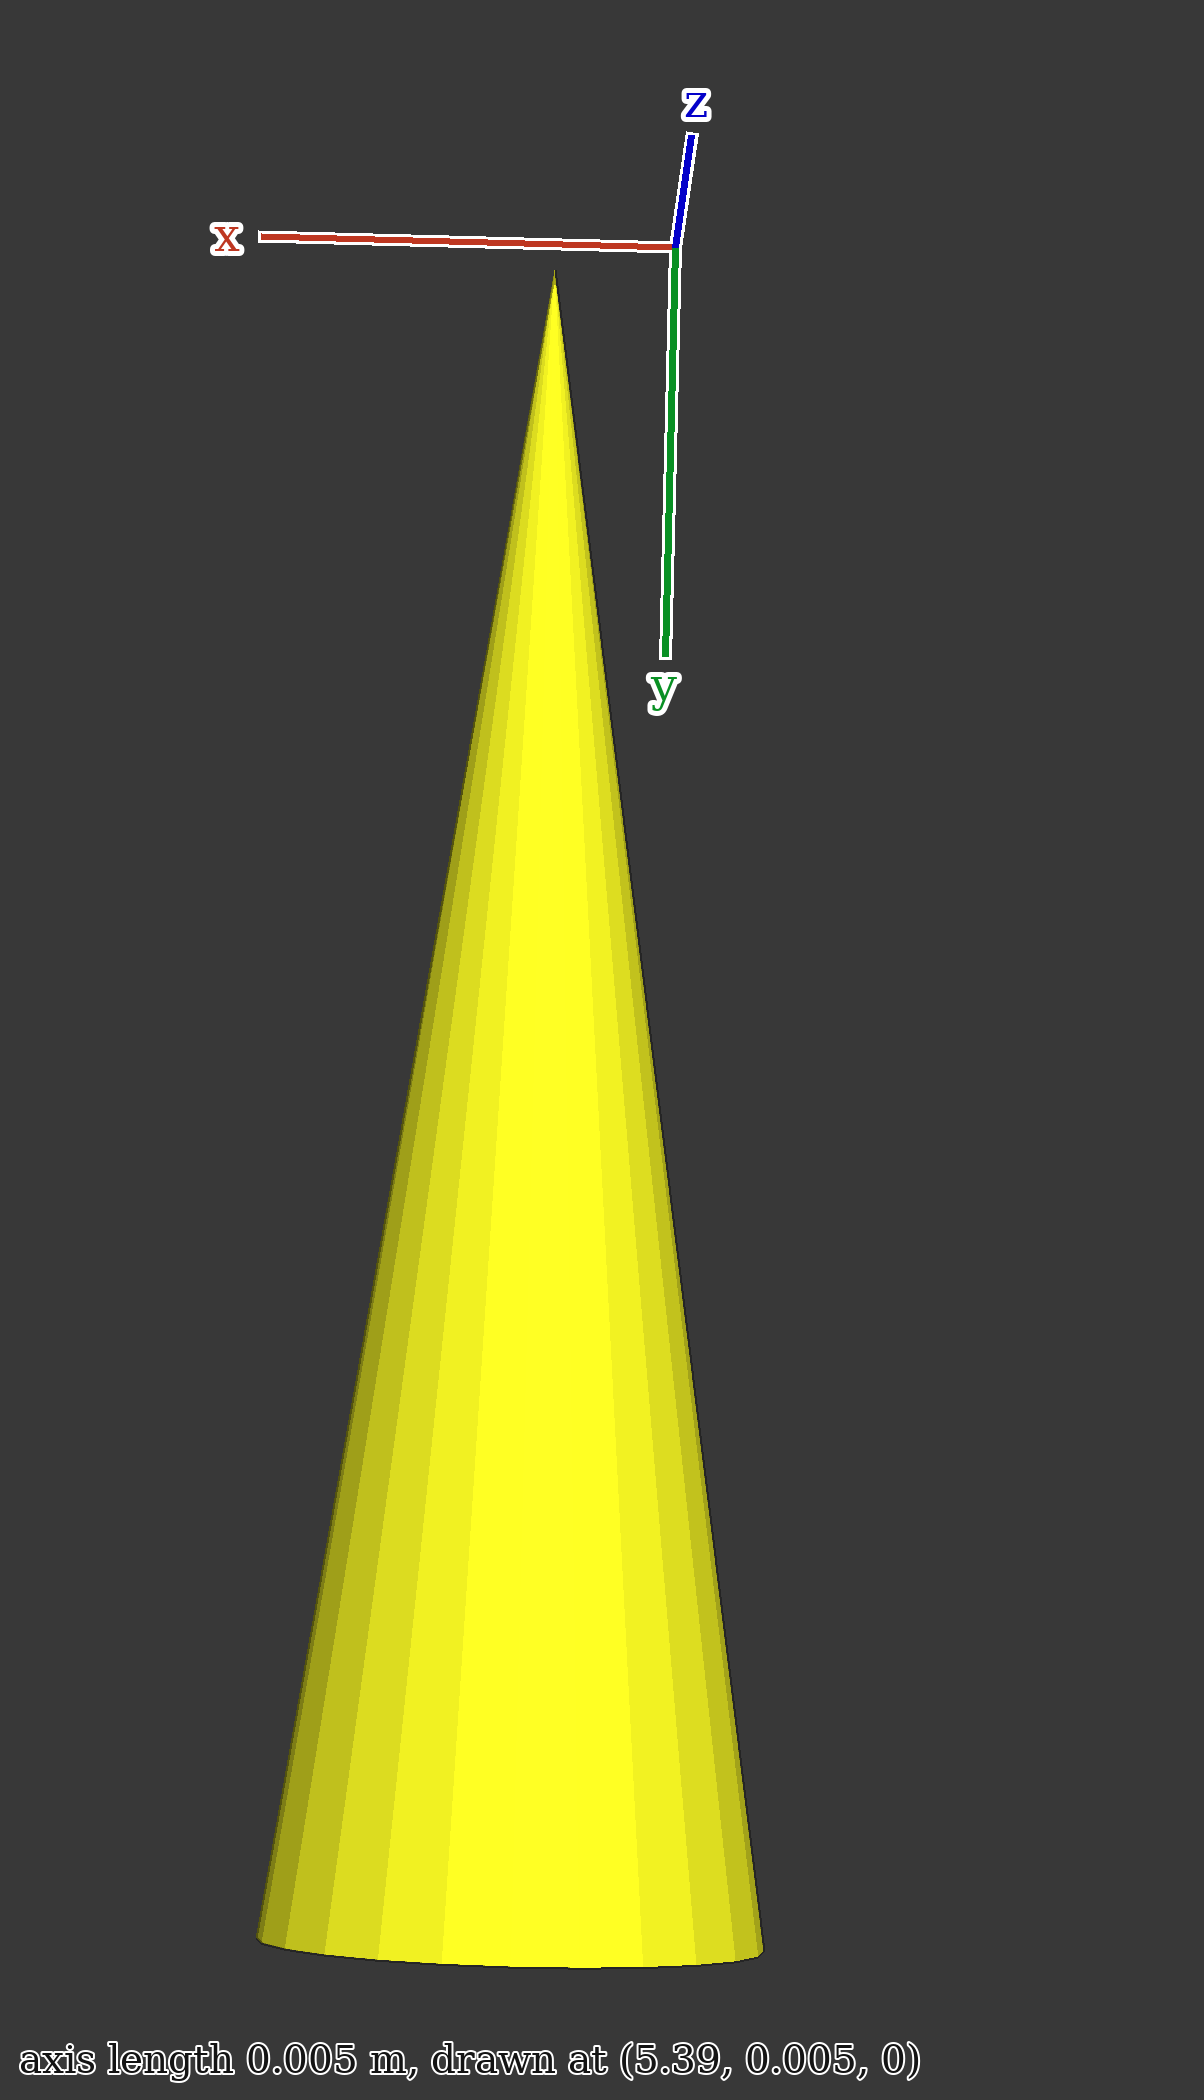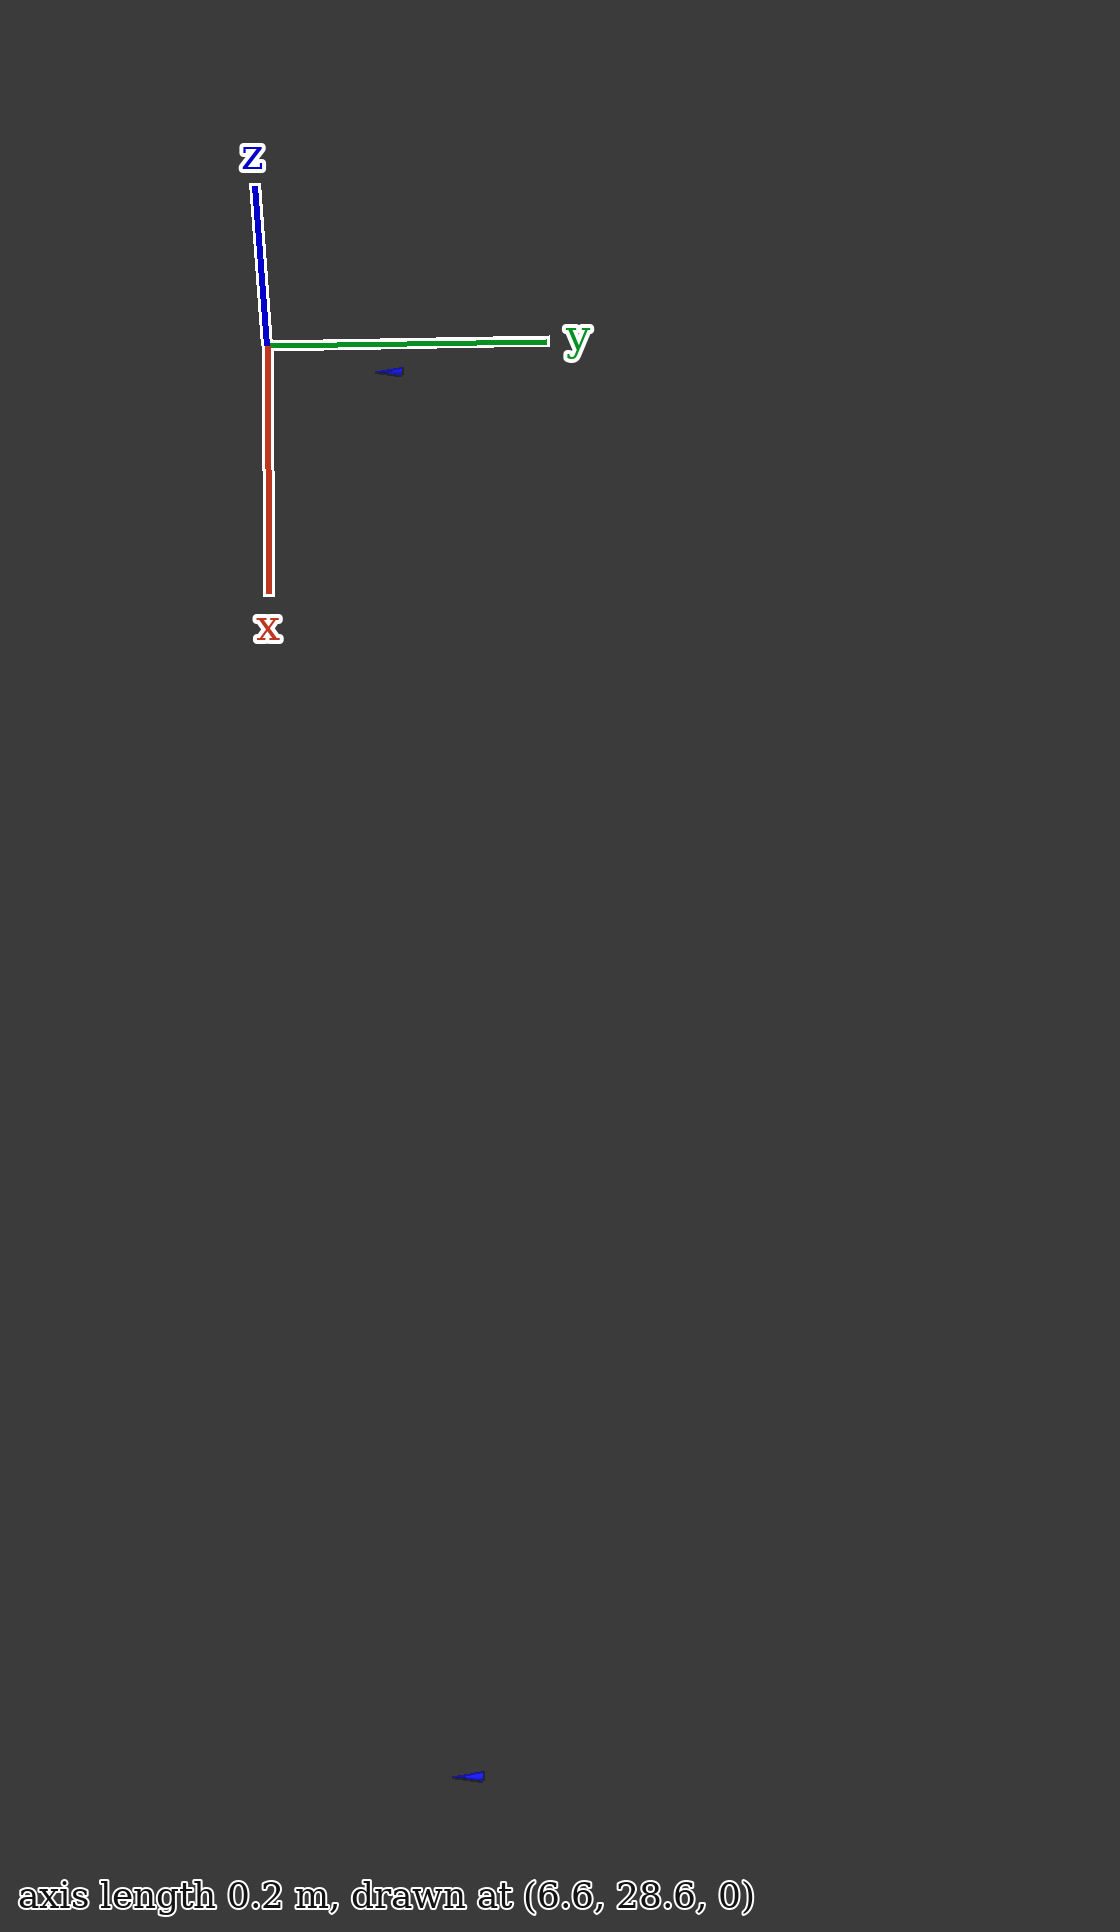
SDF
<?xml version="1.0"?>

<sdf version='1.9'>
    <world name='track'>

        <!-- PHYSICS -->
        <physics name="1ms" type="ignored">
            <max_step_size>0.001</max_step_size>
            <real_time_factor>1.0</real_time_factor>
        </physics>

        <gravity>0 0 -9.8</gravity>
        <magnetic_field>6e-06 2.3e-05 -4.2e-05</magnetic_field>
        <atmosphere type='adiabatic'/>

        <!-- PLUGINS -->
        <plugin name='gz::sim::systems::Physics' filename='gz-sim-physics-system'/>
        <plugin name='gz::sim::systems::UserCommands' filename='gz-sim-user-commands-system'/>
        <plugin name='gz::sim::systems::SceneBroadcaster' filename='gz-sim-scene-broadcaster-system'/>
        <plugin name="gz::sim::systems::Imu" filename="gz-sim-imu-system"/>

        <gui fullscreen='0'>
            <!-- 3D scene -->
            <plugin filename="MinimalScene" name="3D View">
                <gz-gui>
                <title>3D View</title>
                <property type="bool" key="showTitleBar">false</property>
                <property type="string" key="state">docked</property>
                </gz-gui>

                <engine>ogre2</engine>
                <scene>scene</scene>
                <ambient_light>0.4 0.4 0.4</ambient_light>
                <background_color>0.8 0.8 0.8</background_color>
                <camera_pose>-6 0 6 0 0.5 0</camera_pose>
            </plugin>

            <!-- Plugins that add functionality to the scene -->
            <plugin filename="EntityContextMenuPlugin" name="Entity context menu">
                <gz-gui>
                <property key="state" type="string">floating</property>
                <property key="width" type="double">5</property>
                <property key="height" type="double">5</property>
                <property key="showTitleBar" type="bool">false</property>
                </gz-gui>
            </plugin>
            <plugin filename="GzSceneManager" name="Scene Manager">
                <gz-gui>
                <property key="resizable" type="bool">false</property>
                <property key="width" type="double">5</property>
                <property key="height" type="double">5</property>
                <property key="state" type="string">floating</property>
                <property key="showTitleBar" type="bool">false</property>
                </gz-gui>
            </plugin>
            <plugin filename="InteractiveViewControl" name="Interactive view control">
                <gz-gui>
                <property key="resizable" type="bool">false</property>
                <property key="width" type="double">5</property>
                <property key="height" type="double">5</property>
                <property key="state" type="string">floating</property>
                <property key="showTitleBar" type="bool">false</property>
                </gz-gui>
            </plugin>
            <plugin filename="CameraTracking" name="Camera Tracking">
                <gz-gui>
                <property key="resizable" type="bool">false</property>
                <property key="width" type="double">5</property>
                <property key="height" type="double">5</property>
                <property key="state" type="string">floating</property>
                <property key="showTitleBar" type="bool">false</property>
                </gz-gui>
            </plugin>
            <plugin name='World control' filename='WorldControl'>
                <gz-gui>
                    <title>World control</title>
                    <property type='bool' key='showTitleBar'>0</property>
                    <property type='bool' key='resizable'>0</property>
                    <property type='double' key='height'>72</property>
                    <property type='double' key='z'>1</property>
                    <property type='string' key='state'>floating</property>
                    <anchors target='3D View'>
                        <line own='left' target='left'/>
                        <line own='bottom' target='bottom'/>
                    </anchors>
                </gz-gui>
                <play_pause>1</play_pause>
                <step>1</step>
                <start_paused>1</start_paused>
            </plugin>
            <plugin name='World stats' filename='WorldStats'>
                <gz-gui>
                    <title>World stats</title>
                    <property type='bool' key='showTitleBar'>0</property>
                    <property type='bool' key='resizable'>0</property>
                    <property type='double' key='height'>110</property>
                    <property type='double' key='width'>290</property>
                    <property type='double' key='z'>1</property>
                    <property type='string' key='state'>floating</property>
                    <anchors target='3D View'>
                        <line own='right' target='right'/>
                        <line own='bottom' target='bottom'/>
                    </anchors>
                </gz-gui>
                <sim_time>1</sim_time>
                <real_time>1</real_time>
                <real_time_factor>1</real_time_factor>
                <iterations>1</iterations>
            </plugin>

            <plugin filename="VisualizeLidar" name="Visualize Lidar">
            </plugin>

            <plugin filename="ImageDisplay" name="Image Display">
            </plugin>

            <!-- Inspector -->
            <plugin filename="ComponentInspector" name="Component inspector">
                <ignition-gui>
                <property type="string" key="state">docked</property>
                </ignition-gui>
            </plugin>

            <!-- Entity tree -->
            <plugin filename="EntityTree" name="Entity tree">
                <ignition-gui>
                <property type="string" key="state">docked</property>
                </ignition-gui>
            </plugin>
        </gui>

        <!-- SENSORS -->

        <plugin
        filename="gz-sim-sensors-system"
        name="gz::sim::systems::Sensors">
        <render_engine>ogre2</render_engine>
        </plugin>

        <!-- AMBIENT -->

        <scene>
            <ambient>1 1 1 1</ambient>
            <background>0.8 0.8 0.8 1</background>
            <shadows>1</shadows>
        </scene>
        <light name='sun' type='directional'>
            <cast_shadows>1</cast_shadows>
            <pose>0 0 10 0 0 0</pose>
            <diffuse>0.8 0.8 0.8 1</diffuse>
            <specular>0.8 0.8 0.8 1</specular>
            <attenuation>
                <range>1000</range>
                <constant>0.9</constant>
                <linear>0.01</linear>
                <quadratic>0.001</quadratic>
            </attenuation>
            <direction>-0.5 0.1 -0.9</direction>
        </light>

        <model name='ground_plane'>
            <static>true</static>
            <link name='link'>
                <collision name='collision'>
                    <geometry>
                        <plane>
                        <normal>0 0 1</normal>
                        <size>100 100</size>
                        </plane>
                    </geometry>

                    <surface>
                        <friction>
                            <dart/>
                        </friction>
                        <bounce/>
                        <contact/>
                    </surface>
                </collision>

                <visual name='visual'>
                    <geometry>
                        <plane>
                        <normal>0 0 1</normal>
                        <size>100 100</size>
                        </plane>
                    </geometry>
                    <material>
                        <ambient>0.1 0.1 0.1 1</ambient>
                        <diffuse>0.1 0.1 0.1 1</diffuse>
                        <specular>0.8 0.8 0.8 1</specular>
                    </material>
                </visual>

                <pose>0 0 0 0 -0 0</pose>

                <inertial>
                    <pose>0 0 0 0 -0 0</pose>
                    <mass>1</mass>
                    <inertia>
                        <ixx>1</ixx>
                        <ixy>0</ixy>
                        <ixz>0</ixz>
                        <iyy>1</iyy>
                        <iyz>0</iyz>
                        <izz>1</izz>
                    </inertia>
                </inertial>

                <enable_wind>false</enable_wind>

            </link>

            <pose>0 0 0 0 -0 0</pose>

            <self_collide>false</self_collide>
        </model>

        <!-- TRACK -->
        <model name='cones'>
            <pose>0 0 0 0 0 0</pose>

      <link name='cone_0_link'>
        <collision name='cone_0_collision'>
          <geometry>
            <mesh>
              <uri>/home/ubuntu/psd_ws/src/psd_gazebo_worlds/world/models/cone/meshes/cone.stl</uri>
              <scale>0.001 0.001 0.001</scale>
            </mesh>
          </geometry>
        </collision>
        <visual name='cone_0_visual'>
          <geometry>
            <mesh>
              <uri>/home/ubuntu/psd_ws/src/psd_gazebo_worlds/world/models/cone/meshes/cone.stl</uri>
              <scale>0.001 0.001 0.001</scale>
            </mesh>
          </geometry>
          <material>
            <ambient>1 1 0 1</ambient>
            <diffuse>1 1 0 1</diffuse>
            <specular>1 1 0 1</specular>
          </material>
        </visual>
        <pose>5.688073798552464 25.575976039184496 0.0 1.57 0 0</pose>
        <enable_wind>false</enable_wind>
      </link>

      <link name='cone_1_link'>
        <collision name='cone_1_collision'>
          <geometry>
            <mesh>
              <uri>/home/ubuntu/psd_ws/src/psd_gazebo_worlds/world/models/cone/meshes/cone.stl</uri>
              <scale>0.001 0.001 0.001</scale>
            </mesh>
          </geometry>
        </collision>
        <visual name='cone_1_visual'>
          <geometry>
            <mesh>
              <uri>/home/ubuntu/psd_ws/src/psd_gazebo_worlds/world/models/cone/meshes/cone.stl</uri>
              <scale>0.001 0.001 0.001</scale>
            </mesh>
          </geometry>
          <material>
            <ambient>1 1 0 1</ambient>
            <diffuse>1 1 0 1</diffuse>
            <specular>1 1 0 1</specular>
          </material>
        </visual>
        <pose>6.686783688672199 25.608392984830942 0.0 1.57 0 0</pose>
        <enable_wind>false</enable_wind>
      </link>

      <link name='cone_2_link'>
        <collision name='cone_2_collision'>
          <geometry>
            <mesh>
              <uri>/home/ubuntu/psd_ws/src/psd_gazebo_worlds/world/models/cone/meshes/cone.stl</uri>
              <scale>0.001 0.001 0.001</scale>
            </mesh>
          </geometry>
        </collision>
        <visual name='cone_2_visual'>
          <geometry>
            <mesh>
              <uri>/home/ubuntu/psd_ws/src/psd_gazebo_worlds/world/models/cone/meshes/cone.stl</uri>
              <scale>0.001 0.001 0.001</scale>
            </mesh>
          </geometry>
          <material>
            <ambient>1 1 0 1</ambient>
            <diffuse>1 1 0 1</diffuse>
            <specular>1 1 0 1</specular>
          </material>
        </visual>
        <pose>7.683275531344529 25.641049078737048 0.0 1.57 0 0</pose>
        <enable_wind>false</enable_wind>
      </link>

      <link name='cone_3_link'>
        <collision name='cone_3_collision'>
          <geometry>
            <mesh>
              <uri>/home/ubuntu/psd_ws/src/psd_gazebo_worlds/world/models/cone/meshes/cone.stl</uri>
              <scale>0.001 0.001 0.001</scale>
            </mesh>
          </geometry>
        </collision>
        <visual name='cone_3_visual'>
          <geometry>
            <mesh>
              <uri>/home/ubuntu/psd_ws/src/psd_gazebo_worlds/world/models/cone/meshes/cone.stl</uri>
              <scale>0.001 0.001 0.001</scale>
            </mesh>
          </geometry>
          <material>
            <ambient>1 1 0 1</ambient>
            <diffuse>1 1 0 1</diffuse>
            <specular>1 1 0 1</specular>
          </material>
        </visual>
        <pose>8.67759646067718 25.672478593219495 0.0 1.57 0 0</pose>
        <enable_wind>false</enable_wind>
      </link>

      <link name='cone_4_link'>
        <collision name='cone_4_collision'>
          <geometry>
            <mesh>
              <uri>/home/ubuntu/psd_ws/src/psd_gazebo_worlds/world/models/cone/meshes/cone.stl</uri>
              <scale>0.001 0.001 0.001</scale>
            </mesh>
          </geometry>
        </collision>
        <visual name='cone_4_visual'>
          <geometry>
            <mesh>
              <uri>/home/ubuntu/psd_ws/src/psd_gazebo_worlds/world/models/cone/meshes/cone.stl</uri>
              <scale>0.001 0.001 0.001</scale>
            </mesh>
          </geometry>
          <material>
            <ambient>1 1 0 1</ambient>
            <diffuse>1 1 0 1</diffuse>
            <specular>1 1 0 1</specular>
          </material>
        </visual>
        <pose>9.669788208603379 25.701225398652994 0.0 1.57 0 0</pose>
        <enable_wind>false</enable_wind>
      </link>

      <link name='cone_5_link'>
        <collision name='cone_5_collision'>
          <geometry>
            <mesh>
              <uri>/home/ubuntu/psd_ws/src/psd_gazebo_worlds/world/models/cone/meshes/cone.stl</uri>
              <scale>0.001 0.001 0.001</scale>
            </mesh>
          </geometry>
        </collision>
        <visual name='cone_5_visual'>
          <geometry>
            <mesh>
              <uri>/home/ubuntu/psd_ws/src/psd_gazebo_worlds/world/models/cone/meshes/cone.stl</uri>
              <scale>0.001 0.001 0.001</scale>
            </mesh>
          </geometry>
          <material>
            <ambient>1 1 0 1</ambient>
            <diffuse>1 1 0 1</diffuse>
            <specular>1 1 0 1</specular>
          </material>
        </visual>
        <pose>10.659880707778479 25.725842802243847 0.0 1.57 0 0</pose>
        <enable_wind>false</enable_wind>
      </link>

      <link name='cone_6_link'>
        <collision name='cone_6_collision'>
          <geometry>
            <mesh>
              <uri>/home/ubuntu/psd_ws/src/psd_gazebo_worlds/world/models/cone/meshes/cone.stl</uri>
              <scale>0.001 0.001 0.001</scale>
            </mesh>
          </geometry>
        </collision>
        <visual name='cone_6_visual'>
          <geometry>
            <mesh>
              <uri>/home/ubuntu/psd_ws/src/psd_gazebo_worlds/world/models/cone/meshes/cone.stl</uri>
              <scale>0.001 0.001 0.001</scale>
            </mesh>
          </geometry>
          <material>
            <ambient>1 1 0 1</ambient>
            <diffuse>1 1 0 1</diffuse>
            <specular>1 1 0 1</specular>
          </material>
        </visual>
        <pose>13.617552664488128 25.760592629749596 0.0 1.57 0 0</pose>
        <enable_wind>false</enable_wind>
      </link>

      <link name='cone_7_link'>
        <collision name='cone_7_collision'>
          <geometry>
            <mesh>
              <uri>/home/ubuntu/psd_ws/src/psd_gazebo_worlds/world/models/cone/meshes/cone.stl</uri>
              <scale>0.001 0.001 0.001</scale>
            </mesh>
          </geometry>
        </collision>
        <visual name='cone_7_visual'>
          <geometry>
            <mesh>
              <uri>/home/ubuntu/psd_ws/src/psd_gazebo_worlds/world/models/cone/meshes/cone.stl</uri>
              <scale>0.001 0.001 0.001</scale>
            </mesh>
          </geometry>
          <material>
            <ambient>1 1 0 1</ambient>
            <diffuse>1 1 0 1</diffuse>
            <specular>1 1 0 1</specular>
          </material>
        </visual>
        <pose>14.59909152529048 25.754414718774193 0.0 1.57 0 0</pose>
        <enable_wind>false</enable_wind>
      </link>

      <link name='cone_8_link'>
        <collision name='cone_8_collision'>
          <geometry>
            <mesh>
              <uri>/home/ubuntu/psd_ws/src/psd_gazebo_worlds/world/models/cone/meshes/cone.stl</uri>
              <scale>0.001 0.001 0.001</scale>
            </mesh>
          </geometry>
        </collision>
        <visual name='cone_8_visual'>
          <geometry>
            <mesh>
              <uri>/home/ubuntu/psd_ws/src/psd_gazebo_worlds/world/models/cone/meshes/cone.stl</uri>
              <scale>0.001 0.001 0.001</scale>
            </mesh>
          </geometry>
          <material>
            <ambient>1 1 0 1</ambient>
            <diffuse>1 1 0 1</diffuse>
            <specular>1 1 0 1</specular>
          </material>
        </visual>
        <pose>15.57828483089903 25.737018465539393 0.0 1.57 0 0</pose>
        <enable_wind>false</enable_wind>
      </link>

      <link name='cone_9_link'>
        <collision name='cone_9_collision'>
          <geometry>
            <mesh>
              <uri>/home/ubuntu/psd_ws/src/psd_gazebo_worlds/world/models/cone/meshes/cone.stl</uri>
              <scale>0.001 0.001 0.001</scale>
            </mesh>
          </geometry>
        </collision>
        <visual name='cone_9_visual'>
          <geometry>
            <mesh>
              <uri>/home/ubuntu/psd_ws/src/psd_gazebo_worlds/world/models/cone/meshes/cone.stl</uri>
              <scale>0.001 0.001 0.001</scale>
            </mesh>
          </geometry>
          <material>
            <ambient>1 1 0 1</ambient>
            <diffuse>1 1 0 1</diffuse>
            <specular>1 1 0 1</specular>
          </material>
        </visual>
        <pose>16.55496136632748 25.707018440790492 0.0 1.57 0 0</pose>
        <enable_wind>false</enable_wind>
      </link>

      <link name='cone_10_link'>
        <collision name='cone_10_collision'>
          <geometry>
            <mesh>
              <uri>/home/ubuntu/psd_ws/src/psd_gazebo_worlds/world/models/cone/meshes/cone.stl</uri>
              <scale>0.001 0.001 0.001</scale>
            </mesh>
          </geometry>
        </collision>
        <visual name='cone_10_visual'>
          <geometry>
            <mesh>
              <uri>/home/ubuntu/psd_ws/src/psd_gazebo_worlds/world/models/cone/meshes/cone.stl</uri>
              <scale>0.001 0.001 0.001</scale>
            </mesh>
          </geometry>
          <material>
            <ambient>1 1 0 1</ambient>
            <diffuse>1 1 0 1</diffuse>
            <specular>1 1 0 1</specular>
          </material>
        </visual>
        <pose>17.52889540500738 25.663042474111194 0.0 1.57 0 0</pose>
        <enable_wind>false</enable_wind>
      </link>

      <link name='cone_11_link'>
        <collision name='cone_11_collision'>
          <geometry>
            <mesh>
              <uri>/home/ubuntu/psd_ws/src/psd_gazebo_worlds/world/models/cone/meshes/cone.stl</uri>
              <scale>0.001 0.001 0.001</scale>
            </mesh>
          </geometry>
        </collision>
        <visual name='cone_11_visual'>
          <geometry>
            <mesh>
              <uri>/home/ubuntu/psd_ws/src/psd_gazebo_worlds/world/models/cone/meshes/cone.stl</uri>
              <scale>0.001 0.001 0.001</scale>
            </mesh>
          </geometry>
          <material>
            <ambient>1 1 0 1</ambient>
            <diffuse>1 1 0 1</diffuse>
            <specular>1 1 0 1</specular>
          </material>
        </visual>
        <pose>18.48063525037708 25.60132437325189 0.0 1.57 0 0</pose>
        <enable_wind>false</enable_wind>
      </link>

      <link name='cone_12_link'>
        <collision name='cone_12_collision'>
          <geometry>
            <mesh>
              <uri>/home/ubuntu/psd_ws/src/psd_gazebo_worlds/world/models/cone/meshes/cone.stl</uri>
              <scale>0.001 0.001 0.001</scale>
            </mesh>
          </geometry>
        </collision>
        <visual name='cone_12_visual'>
          <geometry>
            <mesh>
              <uri>/home/ubuntu/psd_ws/src/psd_gazebo_worlds/world/models/cone/meshes/cone.stl</uri>
              <scale>0.001 0.001 0.001</scale>
            </mesh>
          </geometry>
          <material>
            <ambient>1 1 0 1</ambient>
            <diffuse>1 1 0 1</diffuse>
            <specular>1 1 0 1</specular>
          </material>
        </visual>
        <pose>19.38169790665118 25.502228943997743 0.0 1.57 0 0</pose>
        <enable_wind>false</enable_wind>
      </link>

      <link name='cone_13_link'>
        <collision name='cone_13_collision'>
          <geometry>
            <mesh>
              <uri>/home/ubuntu/psd_ws/src/psd_gazebo_worlds/world/models/cone/meshes/cone.stl</uri>
              <scale>0.001 0.001 0.001</scale>
            </mesh>
          </geometry>
        </collision>
        <visual name='cone_13_visual'>
          <geometry>
            <mesh>
              <uri>/home/ubuntu/psd_ws/src/psd_gazebo_worlds/world/models/cone/meshes/cone.stl</uri>
              <scale>0.001 0.001 0.001</scale>
            </mesh>
          </geometry>
          <material>
            <ambient>1 1 0 1</ambient>
            <diffuse>1 1 0 1</diffuse>
            <specular>1 1 0 1</specular>
          </material>
        </visual>
        <pose>21.00274022877608 25.108634410740947 0.0 1.57 0 0</pose>
        <enable_wind>false</enable_wind>
      </link>

      <link name='cone_14_link'>
        <collision name='cone_14_collision'>
          <geometry>
            <mesh>
              <uri>/home/ubuntu/psd_ws/src/psd_gazebo_worlds/world/models/cone/meshes/cone.stl</uri>
              <scale>0.001 0.001 0.001</scale>
            </mesh>
          </geometry>
        </collision>
        <visual name='cone_14_visual'>
          <geometry>
            <mesh>
              <uri>/home/ubuntu/psd_ws/src/psd_gazebo_worlds/world/models/cone/meshes/cone.stl</uri>
              <scale>0.001 0.001 0.001</scale>
            </mesh>
          </geometry>
          <material>
            <ambient>1 1 0 1</ambient>
            <diffuse>1 1 0 1</diffuse>
            <specular>1 1 0 1</specular>
          </material>
        </visual>
        <pose>21.69623795675203 24.788112101455546 0.0 1.57 0 0</pose>
        <enable_wind>false</enable_wind>
      </link>

      <link name='cone_15_link'>
        <collision name='cone_15_collision'>
          <geometry>
            <mesh>
              <uri>/home/ubuntu/psd_ws/src/psd_gazebo_worlds/world/models/cone/meshes/cone.stl</uri>
              <scale>0.001 0.001 0.001</scale>
            </mesh>
          </geometry>
        </collision>
        <visual name='cone_15_visual'>
          <geometry>
            <mesh>
              <uri>/home/ubuntu/psd_ws/src/psd_gazebo_worlds/world/models/cone/meshes/cone.stl</uri>
              <scale>0.001 0.001 0.001</scale>
            </mesh>
          </geometry>
          <material>
            <ambient>1 1 0 1</ambient>
            <diffuse>1 1 0 1</diffuse>
            <specular>1 1 0 1</specular>
          </material>
        </visual>
        <pose>22.81574538601283 23.855564008487697 0.0 1.57 0 0</pose>
        <enable_wind>false</enable_wind>
      </link>

      <link name='cone_16_link'>
        <collision name='cone_16_collision'>
          <geometry>
            <mesh>
              <uri>/home/ubuntu/psd_ws/src/psd_gazebo_worlds/world/models/cone/meshes/cone.stl</uri>
              <scale>0.001 0.001 0.001</scale>
            </mesh>
          </geometry>
        </collision>
        <visual name='cone_16_visual'>
          <geometry>
            <mesh>
              <uri>/home/ubuntu/psd_ws/src/psd_gazebo_worlds/world/models/cone/meshes/cone.stl</uri>
              <scale>0.001 0.001 0.001</scale>
            </mesh>
          </geometry>
          <material>
            <ambient>1 1 0 1</ambient>
            <diffuse>1 1 0 1</diffuse>
            <specular>1 1 0 1</specular>
          </material>
        </visual>
        <pose>23.262238576535328 23.235157435865148 0.0 1.57 0 0</pose>
        <enable_wind>false</enable_wind>
      </link>

      <link name='cone_17_link'>
        <collision name='cone_17_collision'>
          <geometry>
            <mesh>
              <uri>/home/ubuntu/psd_ws/src/psd_gazebo_worlds/world/models/cone/meshes/cone.stl</uri>
              <scale>0.001 0.001 0.001</scale>
            </mesh>
          </geometry>
        </collision>
        <visual name='cone_17_visual'>
          <geometry>
            <mesh>
              <uri>/home/ubuntu/psd_ws/src/psd_gazebo_worlds/world/models/cone/meshes/cone.stl</uri>
              <scale>0.001 0.001 0.001</scale>
            </mesh>
          </geometry>
          <material>
            <ambient>1 1 0 1</ambient>
            <diffuse>1 1 0 1</diffuse>
            <specular>1 1 0 1</specular>
          </material>
        </visual>
        <pose>23.625085575957428 22.533576793799497 0.0 1.57 0 0</pose>
        <enable_wind>false</enable_wind>
      </link>

      <link name='cone_18_link'>
        <collision name='cone_18_collision'>
          <geometry>
            <mesh>
              <uri>/home/ubuntu/psd_ws/src/psd_gazebo_worlds/world/models/cone/meshes/cone.stl</uri>
              <scale>0.001 0.001 0.001</scale>
            </mesh>
          </geometry>
        </collision>
        <visual name='cone_18_visual'>
          <geometry>
            <mesh>
              <uri>/home/ubuntu/psd_ws/src/psd_gazebo_worlds/world/models/cone/meshes/cone.stl</uri>
              <scale>0.001 0.001 0.001</scale>
            </mesh>
          </geometry>
          <material>
            <ambient>1 1 0 1</ambient>
            <diffuse>1 1 0 1</diffuse>
            <specular>1 1 0 1</specular>
          </material>
        </visual>
        <pose>23.90270858020368 21.76756350447795 0.0 1.57 0 0</pose>
        <enable_wind>false</enable_wind>
      </link>

      <link name='cone_19_link'>
        <collision name='cone_19_collision'>
          <geometry>
            <mesh>
              <uri>/home/ubuntu/psd_ws/src/psd_gazebo_worlds/world/models/cone/meshes/cone.stl</uri>
              <scale>0.001 0.001 0.001</scale>
            </mesh>
          </geometry>
        </collision>
        <visual name='cone_19_visual'>
          <geometry>
            <mesh>
              <uri>/home/ubuntu/psd_ws/src/psd_gazebo_worlds/world/models/cone/meshes/cone.stl</uri>
              <scale>0.001 0.001 0.001</scale>
            </mesh>
          </geometry>
          <material>
            <ambient>1 1 0 1</ambient>
            <diffuse>1 1 0 1</diffuse>
            <specular>1 1 0 1</specular>
          </material>
        </visual>
        <pose>24.16895681450728 20.177439498432797 0.0 1.57 0 0</pose>
        <enable_wind>false</enable_wind>
      </link>

      <link name='cone_20_link'>
        <collision name='cone_20_collision'>
          <geometry>
            <mesh>
              <uri>/home/ubuntu/psd_ws/src/psd_gazebo_worlds/world/models/cone/meshes/cone.stl</uri>
              <scale>0.001 0.001 0.001</scale>
            </mesh>
          </geometry>
        </collision>
        <visual name='cone_20_visual'>
          <geometry>
            <mesh>
              <uri>/home/ubuntu/psd_ws/src/psd_gazebo_worlds/world/models/cone/meshes/cone.stl</uri>
              <scale>0.001 0.001 0.001</scale>
            </mesh>
          </geometry>
          <material>
            <ambient>1 1 0 1</ambient>
            <diffuse>1 1 0 1</diffuse>
            <specular>1 1 0 1</specular>
          </material>
        </visual>
        <pose>24.142929222418978 19.390641615551097 0.0 1.57 0 0</pose>
        <enable_wind>false</enable_wind>
      </link>

      <link name='cone_21_link'>
        <collision name='cone_21_collision'>
          <geometry>
            <mesh>
              <uri>/home/ubuntu/psd_ws/src/psd_gazebo_worlds/world/models/cone/meshes/cone.stl</uri>
              <scale>0.001 0.001 0.001</scale>
            </mesh>
          </geometry>
        </collision>
        <visual name='cone_21_visual'>
          <geometry>
            <mesh>
              <uri>/home/ubuntu/psd_ws/src/psd_gazebo_worlds/world/models/cone/meshes/cone.stl</uri>
              <scale>0.001 0.001 0.001</scale>
            </mesh>
          </geometry>
          <material>
            <ambient>1 1 0 1</ambient>
            <diffuse>1 1 0 1</diffuse>
            <specular>1 1 0 1</specular>
          </material>
        </visual>
        <pose>24.00638298037288 18.62923715340539 0.0 1.57 0 0</pose>
        <enable_wind>false</enable_wind>
      </link>

      <link name='cone_22_link'>
        <collision name='cone_22_collision'>
          <geometry>
            <mesh>
              <uri>/home/ubuntu/psd_ws/src/psd_gazebo_worlds/world/models/cone/meshes/cone.stl</uri>
              <scale>0.001 0.001 0.001</scale>
            </mesh>
          </geometry>
        </collision>
        <visual name='cone_22_visual'>
          <geometry>
            <mesh>
              <uri>/home/ubuntu/psd_ws/src/psd_gazebo_worlds/world/models/cone/meshes/cone.stl</uri>
              <scale>0.001 0.001 0.001</scale>
            </mesh>
          </geometry>
          <material>
            <ambient>1 1 0 1</ambient>
            <diffuse>1 1 0 1</diffuse>
            <specular>1 1 0 1</specular>
          </material>
        </visual>
        <pose>23.75950698838113 17.910587112532546 0.0 1.57 0 0</pose>
        <enable_wind>false</enable_wind>
      </link>

      <link name='cone_23_link'>
        <collision name='cone_23_collision'>
          <geometry>
            <mesh>
              <uri>/home/ubuntu/psd_ws/src/psd_gazebo_worlds/world/models/cone/meshes/cone.stl</uri>
              <scale>0.001 0.001 0.001</scale>
            </mesh>
          </geometry>
        </collision>
        <visual name='cone_23_visual'>
          <geometry>
            <mesh>
              <uri>/home/ubuntu/psd_ws/src/psd_gazebo_worlds/world/models/cone/meshes/cone.stl</uri>
              <scale>0.001 0.001 0.001</scale>
            </mesh>
          </geometry>
          <material>
            <ambient>1 1 0 1</ambient>
            <diffuse>1 1 0 1</diffuse>
            <specular>1 1 0 1</specular>
          </material>
        </visual>
        <pose>23.401518285041178 17.242702057517494 0.0 1.57 0 0</pose>
        <enable_wind>false</enable_wind>
      </link>

      <link name='cone_24_link'>
        <collision name='cone_24_collision'>
          <geometry>
            <mesh>
              <uri>/home/ubuntu/psd_ws/src/psd_gazebo_worlds/world/models/cone/meshes/cone.stl</uri>
              <scale>0.001 0.001 0.001</scale>
            </mesh>
          </geometry>
        </collision>
        <visual name='cone_24_visual'>
          <geometry>
            <mesh>
              <uri>/home/ubuntu/psd_ws/src/psd_gazebo_worlds/world/models/cone/meshes/cone.stl</uri>
              <scale>0.001 0.001 0.001</scale>
            </mesh>
          </geometry>
          <material>
            <ambient>1 1 0 1</ambient>
            <diffuse>1 1 0 1</diffuse>
            <specular>1 1 0 1</specular>
          </material>
        </visual>
        <pose>22.36550739673898 16.043194299255696 0.0 1.57 0 0</pose>
        <enable_wind>false</enable_wind>
      </link>

      <link name='cone_25_link'>
        <collision name='cone_25_collision'>
          <geometry>
            <mesh>
              <uri>/home/ubuntu/psd_ws/src/psd_gazebo_worlds/world/models/cone/meshes/cone.stl</uri>
              <scale>0.001 0.001 0.001</scale>
            </mesh>
          </geometry>
        </collision>
        <visual name='cone_25_visual'>
          <geometry>
            <mesh>
              <uri>/home/ubuntu/psd_ws/src/psd_gazebo_worlds/world/models/cone/meshes/cone.stl</uri>
              <scale>0.001 0.001 0.001</scale>
            </mesh>
          </geometry>
          <material>
            <ambient>1 1 0 1</ambient>
            <diffuse>1 1 0 1</diffuse>
            <specular>1 1 0 1</specular>
          </material>
        </visual>
        <pose>21.007376550970378 15.072803432951893 0.0 1.57 0 0</pose>
        <enable_wind>false</enable_wind>
      </link>

      <link name='cone_26_link'>
        <collision name='cone_26_collision'>
          <geometry>
            <mesh>
              <uri>/home/ubuntu/psd_ws/src/psd_gazebo_worlds/world/models/cone/meshes/cone.stl</uri>
              <scale>0.001 0.001 0.001</scale>
            </mesh>
          </geometry>
        </collision>
        <visual name='cone_26_visual'>
          <geometry>
            <mesh>
              <uri>/home/ubuntu/psd_ws/src/psd_gazebo_worlds/world/models/cone/meshes/cone.stl</uri>
              <scale>0.001 0.001 0.001</scale>
            </mesh>
          </geometry>
          <material>
            <ambient>1 1 0 1</ambient>
            <diffuse>1 1 0 1</diffuse>
            <specular>1 1 0 1</specular>
          </material>
        </visual>
        <pose>20.26277547690503 14.703898176383696 0.0 1.57 0 0</pose>
        <enable_wind>false</enable_wind>
      </link>

      <link name='cone_27_link'>
        <collision name='cone_27_collision'>
          <geometry>
            <mesh>
              <uri>/home/ubuntu/psd_ws/src/psd_gazebo_worlds/world/models/cone/meshes/cone.stl</uri>
              <scale>0.001 0.001 0.001</scale>
            </mesh>
          </geometry>
        </collision>
        <visual name='cone_27_visual'>
          <geometry>
            <mesh>
              <uri>/home/ubuntu/psd_ws/src/psd_gazebo_worlds/world/models/cone/meshes/cone.stl</uri>
              <scale>0.001 0.001 0.001</scale>
            </mesh>
          </geometry>
          <material>
            <ambient>1 1 0 1</ambient>
            <diffuse>1 1 0 1</diffuse>
            <specular>1 1 0 1</specular>
          </material>
        </visual>
        <pose>19.48934784503568 14.424853096212594 0.0 1.57 0 0</pose>
        <enable_wind>false</enable_wind>
      </link>

      <link name='cone_28_link'>
        <collision name='cone_28_collision'>
          <geometry>
            <mesh>
              <uri>/home/ubuntu/psd_ws/src/psd_gazebo_worlds/world/models/cone/meshes/cone.stl</uri>
              <scale>0.001 0.001 0.001</scale>
            </mesh>
          </geometry>
        </collision>
        <visual name='cone_28_visual'>
          <geometry>
            <mesh>
              <uri>/home/ubuntu/psd_ws/src/psd_gazebo_worlds/world/models/cone/meshes/cone.stl</uri>
              <scale>0.001 0.001 0.001</scale>
            </mesh>
          </geometry>
          <material>
            <ambient>1 1 0 1</ambient>
            <diffuse>1 1 0 1</diffuse>
            <specular>1 1 0 1</specular>
          </material>
        </visual>
        <pose>18.696688591643728 14.242005230569994 0.0 1.57 0 0</pose>
        <enable_wind>false</enable_wind>
      </link>

      <link name='cone_29_link'>
        <collision name='cone_29_collision'>
          <geometry>
            <mesh>
              <uri>/home/ubuntu/psd_ws/src/psd_gazebo_worlds/world/models/cone/meshes/cone.stl</uri>
              <scale>0.001 0.001 0.001</scale>
            </mesh>
          </geometry>
        </collision>
        <visual name='cone_29_visual'>
          <geometry>
            <mesh>
              <uri>/home/ubuntu/psd_ws/src/psd_gazebo_worlds/world/models/cone/meshes/cone.stl</uri>
              <scale>0.001 0.001 0.001</scale>
            </mesh>
          </geometry>
          <material>
            <ambient>1 1 0 1</ambient>
            <diffuse>1 1 0 1</diffuse>
            <specular>1 1 0 1</specular>
          </material>
        </visual>
        <pose>17.89609613061728 14.160577510856644 0.0 1.57 0 0</pose>
        <enable_wind>false</enable_wind>
      </link>

      <link name='cone_30_link'>
        <collision name='cone_30_collision'>
          <geometry>
            <mesh>
              <uri>/home/ubuntu/psd_ws/src/psd_gazebo_worlds/world/models/cone/meshes/cone.stl</uri>
              <scale>0.001 0.001 0.001</scale>
            </mesh>
          </geometry>
        </collision>
        <visual name='cone_30_visual'>
          <geometry>
            <mesh>
              <uri>/home/ubuntu/psd_ws/src/psd_gazebo_worlds/world/models/cone/meshes/cone.stl</uri>
              <scale>0.001 0.001 0.001</scale>
            </mesh>
          </geometry>
          <material>
            <ambient>1 1 0 1</ambient>
            <diffuse>1 1 0 1</diffuse>
            <specular>1 1 0 1</specular>
          </material>
        </visual>
        <pose>17.093347822525182 14.183804943418195 0.0 1.57 0 0</pose>
        <enable_wind>false</enable_wind>
      </link>

      <link name='cone_31_link'>
        <collision name='cone_31_collision'>
          <geometry>
            <mesh>
              <uri>/home/ubuntu/psd_ws/src/psd_gazebo_worlds/world/models/cone/meshes/cone.stl</uri>
              <scale>0.001 0.001 0.001</scale>
            </mesh>
          </geometry>
        </collision>
        <visual name='cone_31_visual'>
          <geometry>
            <mesh>
              <uri>/home/ubuntu/psd_ws/src/psd_gazebo_worlds/world/models/cone/meshes/cone.stl</uri>
              <scale>0.001 0.001 0.001</scale>
            </mesh>
          </geometry>
          <material>
            <ambient>1 1 0 1</ambient>
            <diffuse>1 1 0 1</diffuse>
            <specular>1 1 0 1</specular>
          </material>
        </visual>
        <pose>16.28342942680998 14.308784298882994 0.0 1.57 0 0</pose>
        <enable_wind>false</enable_wind>
      </link>

      <link name='cone_32_link'>
        <collision name='cone_32_collision'>
          <geometry>
            <mesh>
              <uri>/home/ubuntu/psd_ws/src/psd_gazebo_worlds/world/models/cone/meshes/cone.stl</uri>
              <scale>0.001 0.001 0.001</scale>
            </mesh>
          </geometry>
        </collision>
        <visual name='cone_32_visual'>
          <geometry>
            <mesh>
              <uri>/home/ubuntu/psd_ws/src/psd_gazebo_worlds/world/models/cone/meshes/cone.stl</uri>
              <scale>0.001 0.001 0.001</scale>
            </mesh>
          </geometry>
          <material>
            <ambient>1 1 0 1</ambient>
            <diffuse>1 1 0 1</diffuse>
            <specular>1 1 0 1</specular>
          </material>
        </visual>
        <pose>14.67879360754858 14.835059786328195 0.0 1.57 0 0</pose>
        <enable_wind>false</enable_wind>
      </link>

      <link name='cone_33_link'>
        <collision name='cone_33_collision'>
          <geometry>
            <mesh>
              <uri>/home/ubuntu/psd_ws/src/psd_gazebo_worlds/world/models/cone/meshes/cone.stl</uri>
              <scale>0.001 0.001 0.001</scale>
            </mesh>
          </geometry>
        </collision>
        <visual name='cone_33_visual'>
          <geometry>
            <mesh>
              <uri>/home/ubuntu/psd_ws/src/psd_gazebo_worlds/world/models/cone/meshes/cone.stl</uri>
              <scale>0.001 0.001 0.001</scale>
            </mesh>
          </geometry>
          <material>
            <ambient>1 1 0 1</ambient>
            <diffuse>1 1 0 1</diffuse>
            <specular>1 1 0 1</specular>
          </material>
        </visual>
        <pose>13.12512234816783 15.675407566678345 0.0 1.57 0 0</pose>
        <enable_wind>false</enable_wind>
      </link>

      <link name='cone_34_link'>
        <collision name='cone_34_collision'>
          <geometry>
            <mesh>
              <uri>/home/ubuntu/psd_ws/src/psd_gazebo_worlds/world/models/cone/meshes/cone.stl</uri>
              <scale>0.001 0.001 0.001</scale>
            </mesh>
          </geometry>
        </collision>
        <visual name='cone_34_visual'>
          <geometry>
            <mesh>
              <uri>/home/ubuntu/psd_ws/src/psd_gazebo_worlds/world/models/cone/meshes/cone.stl</uri>
              <scale>0.001 0.001 0.001</scale>
            </mesh>
          </geometry>
          <material>
            <ambient>1 1 0 1</ambient>
            <diffuse>1 1 0 1</diffuse>
            <specular>1 1 0 1</specular>
          </material>
        </visual>
        <pose>12.34444731285033 16.195279518574996 0.0 1.57 0 0</pose>
        <enable_wind>false</enable_wind>
      </link>

      <link name='cone_35_link'>
        <collision name='cone_35_collision'>
          <geometry>
            <mesh>
              <uri>/home/ubuntu/psd_ws/src/psd_gazebo_worlds/world/models/cone/meshes/cone.stl</uri>
              <scale>0.001 0.001 0.001</scale>
            </mesh>
          </geometry>
        </collision>
        <visual name='cone_35_visual'>
          <geometry>
            <mesh>
              <uri>/home/ubuntu/psd_ws/src/psd_gazebo_worlds/world/models/cone/meshes/cone.stl</uri>
              <scale>0.001 0.001 0.001</scale>
            </mesh>
          </geometry>
          <material>
            <ambient>1 1 0 1</ambient>
            <diffuse>1 1 0 1</diffuse>
            <specular>1 1 0 1</specular>
          </material>
        </visual>
        <pose>11.54286874527188 16.759254248797696 0.0 1.57 0 0</pose>
        <enable_wind>false</enable_wind>
      </link>

      <link name='cone_36_link'>
        <collision name='cone_36_collision'>
          <geometry>
            <mesh>
              <uri>/home/ubuntu/psd_ws/src/psd_gazebo_worlds/world/models/cone/meshes/cone.stl</uri>
              <scale>0.001 0.001 0.001</scale>
            </mesh>
          </geometry>
        </collision>
        <visual name='cone_36_visual'>
          <geometry>
            <mesh>
              <uri>/home/ubuntu/psd_ws/src/psd_gazebo_worlds/world/models/cone/meshes/cone.stl</uri>
              <scale>0.001 0.001 0.001</scale>
            </mesh>
          </geometry>
          <material>
            <ambient>1 1 0 1</ambient>
            <diffuse>1 1 0 1</diffuse>
            <specular>1 1 0 1</specular>
          </material>
        </visual>
        <pose>10.70542903226413 17.345423851575145 0.0 1.57 0 0</pose>
        <enable_wind>false</enable_wind>
      </link>

      <link name='cone_37_link'>
        <collision name='cone_37_collision'>
          <geometry>
            <mesh>
              <uri>/home/ubuntu/psd_ws/src/psd_gazebo_worlds/world/models/cone/meshes/cone.stl</uri>
              <scale>0.001 0.001 0.001</scale>
            </mesh>
          </geometry>
        </collision>
        <visual name='cone_37_visual'>
          <geometry>
            <mesh>
              <uri>/home/ubuntu/psd_ws/src/psd_gazebo_worlds/world/models/cone/meshes/cone.stl</uri>
              <scale>0.001 0.001 0.001</scale>
            </mesh>
          </geometry>
          <material>
            <ambient>1 1 0 1</ambient>
            <diffuse>1 1 0 1</diffuse>
            <specular>1 1 0 1</specular>
          </material>
        </visual>
        <pose>9.81535172855073 17.928829846275846 0.0 1.57 0 0</pose>
        <enable_wind>false</enable_wind>
      </link>

      <link name='cone_38_link'>
        <collision name='cone_38_collision'>
          <geometry>
            <mesh>
              <uri>/home/ubuntu/psd_ws/src/psd_gazebo_worlds/world/models/cone/meshes/cone.stl</uri>
              <scale>0.001 0.001 0.001</scale>
            </mesh>
          </geometry>
        </collision>
        <visual name='cone_38_visual'>
          <geometry>
            <mesh>
              <uri>/home/ubuntu/psd_ws/src/psd_gazebo_worlds/world/models/cone/meshes/cone.stl</uri>
              <scale>0.001 0.001 0.001</scale>
            </mesh>
          </geometry>
          <material>
            <ambient>1 1 0 1</ambient>
            <diffuse>1 1 0 1</diffuse>
            <specular>1 1 0 1</specular>
          </material>
        </visual>
        <pose>7.819146252528229 18.962666365817697 0.0 1.57 0 0</pose>
        <enable_wind>false</enable_wind>
      </link>

      <link name='cone_39_link'>
        <collision name='cone_39_collision'>
          <geometry>
            <mesh>
              <uri>/home/ubuntu/psd_ws/src/psd_gazebo_worlds/world/models/cone/meshes/cone.stl</uri>
              <scale>0.001 0.001 0.001</scale>
            </mesh>
          </geometry>
        </collision>
        <visual name='cone_39_visual'>
          <geometry>
            <mesh>
              <uri>/home/ubuntu/psd_ws/src/psd_gazebo_worlds/world/models/cone/meshes/cone.stl</uri>
              <scale>0.001 0.001 0.001</scale>
            </mesh>
          </geometry>
          <material>
            <ambient>1 1 0 1</ambient>
            <diffuse>1 1 0 1</diffuse>
            <specular>1 1 0 1</specular>
          </material>
        </visual>
        <pose>6.736016456323075 19.340076103456994 0.0 1.57 0 0</pose>
        <enable_wind>false</enable_wind>
      </link>

      <link name='cone_40_link'>
        <collision name='cone_40_collision'>
          <geometry>
            <mesh>
              <uri>/home/ubuntu/psd_ws/src/psd_gazebo_worlds/world/models/cone/meshes/cone.stl</uri>
              <scale>0.001 0.001 0.001</scale>
            </mesh>
          </geometry>
        </collision>
        <visual name='cone_40_visual'>
          <geometry>
            <mesh>
              <uri>/home/ubuntu/psd_ws/src/psd_gazebo_worlds/world/models/cone/meshes/cone.stl</uri>
              <scale>0.001 0.001 0.001</scale>
            </mesh>
          </geometry>
          <material>
            <ambient>1 1 0 1</ambient>
            <diffuse>1 1 0 1</diffuse>
            <specular>1 1 0 1</specular>
          </material>
        </visual>
        <pose>5.625688671307055 19.608267067870344 0.0 1.57 0 0</pose>
        <enable_wind>false</enable_wind>
      </link>

      <link name='cone_41_link'>
        <collision name='cone_41_collision'>
          <geometry>
            <mesh>
              <uri>/home/ubuntu/psd_ws/src/psd_gazebo_worlds/world/models/cone/meshes/cone.stl</uri>
              <scale>0.001 0.001 0.001</scale>
            </mesh>
          </geometry>
        </collision>
        <visual name='cone_41_visual'>
          <geometry>
            <mesh>
              <uri>/home/ubuntu/psd_ws/src/psd_gazebo_worlds/world/models/cone/meshes/cone.stl</uri>
              <scale>0.001 0.001 0.001</scale>
            </mesh>
          </geometry>
          <material>
            <ambient>1 1 0 1</ambient>
            <diffuse>1 1 0 1</diffuse>
            <specular>1 1 0 1</specular>
          </material>
        </visual>
        <pose>4.499605843805784 19.76913899999549 0.0 1.57 0 0</pose>
        <enable_wind>false</enable_wind>
      </link>

      <link name='cone_42_link'>
        <collision name='cone_42_collision'>
          <geometry>
            <mesh>
              <uri>/home/ubuntu/psd_ws/src/psd_gazebo_worlds/world/models/cone/meshes/cone.stl</uri>
              <scale>0.001 0.001 0.001</scale>
            </mesh>
          </geometry>
        </collision>
        <visual name='cone_42_visual'>
          <geometry>
            <mesh>
              <uri>/home/ubuntu/psd_ws/src/psd_gazebo_worlds/world/models/cone/meshes/cone.stl</uri>
              <scale>0.001 0.001 0.001</scale>
            </mesh>
          </geometry>
          <material>
            <ambient>1 1 0 1</ambient>
            <diffuse>1 1 0 1</diffuse>
            <specular>1 1 0 1</specular>
          </material>
        </visual>
        <pose>2.237851402510062 19.781549324452847 0.0 1.57 0 0</pose>
        <enable_wind>false</enable_wind>
      </link>

      <link name='cone_43_link'>
        <collision name='cone_43_collision'>
          <geometry>
            <mesh>
              <uri>/home/ubuntu/psd_ws/src/psd_gazebo_worlds/world/models/cone/meshes/cone.stl</uri>
              <scale>0.001 0.001 0.001</scale>
            </mesh>
          </geometry>
        </collision>
        <visual name='cone_43_visual'>
          <geometry>
            <mesh>
              <uri>/home/ubuntu/psd_ws/src/psd_gazebo_worlds/world/models/cone/meshes/cone.stl</uri>
              <scale>0.001 0.001 0.001</scale>
            </mesh>
          </geometry>
          <material>
            <ambient>1 1 0 1</ambient>
            <diffuse>1 1 0 1</diffuse>
            <specular>1 1 0 1</specular>
          </material>
        </visual>
        <pose>1.0621360480618343 19.61069519829904 0.0 1.57 0 0</pose>
        <enable_wind>false</enable_wind>
      </link>

      <link name='cone_44_link'>
        <collision name='cone_44_collision'>
          <geometry>
            <mesh>
              <uri>/home/ubuntu/psd_ws/src/psd_gazebo_worlds/world/models/cone/meshes/cone.stl</uri>
              <scale>0.001 0.001 0.001</scale>
            </mesh>
          </geometry>
        </collision>
        <visual name='cone_44_visual'>
          <geometry>
            <mesh>
              <uri>/home/ubuntu/psd_ws/src/psd_gazebo_worlds/world/models/cone/meshes/cone.stl</uri>
              <scale>0.001 0.001 0.001</scale>
            </mesh>
          </geometry>
          <material>
            <ambient>1 1 0 1</ambient>
            <diffuse>1 1 0 1</diffuse>
            <specular>1 1 0 1</specular>
          </material>
        </visual>
        <pose>-1.324325924259746 18.58802514447199 0.0 1.57 0 0</pose>
        <enable_wind>false</enable_wind>
      </link>

      <link name='cone_45_link'>
        <collision name='cone_45_collision'>
          <geometry>
            <mesh>
              <uri>/home/ubuntu/psd_ws/src/psd_gazebo_worlds/world/models/cone/meshes/cone.stl</uri>
              <scale>0.001 0.001 0.001</scale>
            </mesh>
          </geometry>
        </collision>
        <visual name='cone_45_visual'>
          <geometry>
            <mesh>
              <uri>/home/ubuntu/psd_ws/src/psd_gazebo_worlds/world/models/cone/meshes/cone.stl</uri>
              <scale>0.001 0.001 0.001</scale>
            </mesh>
          </geometry>
          <material>
            <ambient>1 1 0 1</ambient>
            <diffuse>1 1 0 1</diffuse>
            <specular>1 1 0 1</specular>
          </material>
        </visual>
        <pose>-2.3385737853927306 17.62455053084524 0.0 1.57 0 0</pose>
        <enable_wind>false</enable_wind>
      </link>

      <link name='cone_46_link'>
        <collision name='cone_46_collision'>
          <geometry>
            <mesh>
              <uri>/home/ubuntu/psd_ws/src/psd_gazebo_worlds/world/models/cone/meshes/cone.stl</uri>
              <scale>0.001 0.001 0.001</scale>
            </mesh>
          </geometry>
        </collision>
        <visual name='cone_46_visual'>
          <geometry>
            <mesh>
              <uri>/home/ubuntu/psd_ws/src/psd_gazebo_worlds/world/models/cone/meshes/cone.stl</uri>
              <scale>0.001 0.001 0.001</scale>
            </mesh>
          </geometry>
          <material>
            <ambient>1 1 0 1</ambient>
            <diffuse>1 1 0 1</diffuse>
            <specular>1 1 0 1</specular>
          </material>
        </visual>
        <pose>-3.057532352183671 16.428847301106394 0.0 1.57 0 0</pose>
        <enable_wind>false</enable_wind>
      </link>

      <link name='cone_47_link'>
        <collision name='cone_47_collision'>
          <geometry>
            <mesh>
              <uri>/home/ubuntu/psd_ws/src/psd_gazebo_worlds/world/models/cone/meshes/cone.stl</uri>
              <scale>0.001 0.001 0.001</scale>
            </mesh>
          </geometry>
        </collision>
        <visual name='cone_47_visual'>
          <geometry>
            <mesh>
              <uri>/home/ubuntu/psd_ws/src/psd_gazebo_worlds/world/models/cone/meshes/cone.stl</uri>
              <scale>0.001 0.001 0.001</scale>
            </mesh>
          </geometry>
          <material>
            <ambient>1 1 0 1</ambient>
            <diffuse>1 1 0 1</diffuse>
            <specular>1 1 0 1</specular>
          </material>
        </visual>
        <pose>-3.4357091502540698 15.092927758566493 0.0 1.57 0 0</pose>
        <enable_wind>false</enable_wind>
      </link>

      <link name='cone_48_link'>
        <collision name='cone_48_collision'>
          <geometry>
            <mesh>
              <uri>/home/ubuntu/psd_ws/src/psd_gazebo_worlds/world/models/cone/meshes/cone.stl</uri>
              <scale>0.001 0.001 0.001</scale>
            </mesh>
          </geometry>
        </collision>
        <visual name='cone_48_visual'>
          <geometry>
            <mesh>
              <uri>/home/ubuntu/psd_ws/src/psd_gazebo_worlds/world/models/cone/meshes/cone.stl</uri>
              <scale>0.001 0.001 0.001</scale>
            </mesh>
          </geometry>
          <material>
            <ambient>1 1 0 1</ambient>
            <diffuse>1 1 0 1</diffuse>
            <specular>1 1 0 1</specular>
          </material>
        </visual>
        <pose>-3.4564397170272194 13.711464200332895 0.0 1.57 0 0</pose>
        <enable_wind>false</enable_wind>
      </link>

      <link name='cone_49_link'>
        <collision name='cone_49_collision'>
          <geometry>
            <mesh>
              <uri>/home/ubuntu/psd_ws/src/psd_gazebo_worlds/world/models/cone/meshes/cone.stl</uri>
              <scale>0.001 0.001 0.001</scale>
            </mesh>
          </geometry>
        </collision>
        <visual name='cone_49_visual'>
          <geometry>
            <mesh>
              <uri>/home/ubuntu/psd_ws/src/psd_gazebo_worlds/world/models/cone/meshes/cone.stl</uri>
              <scale>0.001 0.001 0.001</scale>
            </mesh>
          </geometry>
          <material>
            <ambient>1 1 0 1</ambient>
            <diffuse>1 1 0 1</diffuse>
            <specular>1 1 0 1</specular>
          </material>
        </visual>
        <pose>-3.1280154597066705 12.376449887802094 0.0 1.57 0 0</pose>
        <enable_wind>false</enable_wind>
      </link>

      <link name='cone_50_link'>
        <collision name='cone_50_collision'>
          <geometry>
            <mesh>
              <uri>/home/ubuntu/psd_ws/src/psd_gazebo_worlds/world/models/cone/meshes/cone.stl</uri>
              <scale>0.001 0.001 0.001</scale>
            </mesh>
          </geometry>
        </collision>
        <visual name='cone_50_visual'>
          <geometry>
            <mesh>
              <uri>/home/ubuntu/psd_ws/src/psd_gazebo_worlds/world/models/cone/meshes/cone.stl</uri>
              <scale>0.001 0.001 0.001</scale>
            </mesh>
          </geometry>
          <material>
            <ambient>1 1 0 1</ambient>
            <diffuse>1 1 0 1</diffuse>
            <specular>1 1 0 1</specular>
          </material>
        </visual>
        <pose>-2.4808111366686756 11.171216009237945 0.0 1.57 0 0</pose>
        <enable_wind>false</enable_wind>
      </link>

      <link name='cone_51_link'>
        <collision name='cone_51_collision'>
          <geometry>
            <mesh>
              <uri>/home/ubuntu/psd_ws/src/psd_gazebo_worlds/world/models/cone/meshes/cone.stl</uri>
              <scale>0.001 0.001 0.001</scale>
            </mesh>
          </geometry>
        </collision>
        <visual name='cone_51_visual'>
          <geometry>
            <mesh>
              <uri>/home/ubuntu/psd_ws/src/psd_gazebo_worlds/world/models/cone/meshes/cone.stl</uri>
              <scale>0.001 0.001 0.001</scale>
            </mesh>
          </geometry>
          <material>
            <ambient>1 1 0 1</ambient>
            <diffuse>1 1 0 1</diffuse>
            <specular>1 1 0 1</specular>
          </material>
        </visual>
        <pose>0.2815136497064943 8.870109274852464 0.0 1.57 0 0</pose>
        <enable_wind>false</enable_wind>
      </link>

      <link name='cone_52_link'>
        <collision name='cone_52_collision'>
          <geometry>
            <mesh>
              <uri>/home/ubuntu/psd_ws/src/psd_gazebo_worlds/world/models/cone/meshes/cone.stl</uri>
              <scale>0.001 0.001 0.001</scale>
            </mesh>
          </geometry>
        </collision>
        <visual name='cone_52_visual'>
          <geometry>
            <mesh>
              <uri>/home/ubuntu/psd_ws/src/psd_gazebo_worlds/world/models/cone/meshes/cone.stl</uri>
              <scale>0.001 0.001 0.001</scale>
            </mesh>
          </geometry>
          <material>
            <ambient>1 1 0 1</ambient>
            <diffuse>1 1 0 1</diffuse>
            <specular>1 1 0 1</specular>
          </material>
        </visual>
        <pose>1.1167287732681892 8.374944986892263 0.0 1.57 0 0</pose>
        <enable_wind>false</enable_wind>
      </link>

      <link name='cone_53_link'>
        <collision name='cone_53_collision'>
          <geometry>
            <mesh>
              <uri>/home/ubuntu/psd_ws/src/psd_gazebo_worlds/world/models/cone/meshes/cone.stl</uri>
              <scale>0.001 0.001 0.001</scale>
            </mesh>
          </geometry>
        </collision>
        <visual name='cone_53_visual'>
          <geometry>
            <mesh>
              <uri>/home/ubuntu/psd_ws/src/psd_gazebo_worlds/world/models/cone/meshes/cone.stl</uri>
              <scale>0.001 0.001 0.001</scale>
            </mesh>
          </geometry>
          <material>
            <ambient>1 1 0 1</ambient>
            <diffuse>1 1 0 1</diffuse>
            <specular>1 1 0 1</specular>
          </material>
        </visual>
        <pose>1.8238571007678392 7.899865939716625 0.0 1.57 0 0</pose>
        <enable_wind>false</enable_wind>
      </link>

      <link name='cone_54_link'>
        <collision name='cone_54_collision'>
          <geometry>
            <mesh>
              <uri>/home/ubuntu/psd_ws/src/psd_gazebo_worlds/world/models/cone/meshes/cone.stl</uri>
              <scale>0.001 0.001 0.001</scale>
            </mesh>
          </geometry>
        </collision>
        <visual name='cone_54_visual'>
          <geometry>
            <mesh>
              <uri>/home/ubuntu/psd_ws/src/psd_gazebo_worlds/world/models/cone/meshes/cone.stl</uri>
              <scale>0.001 0.001 0.001</scale>
            </mesh>
          </geometry>
          <material>
            <ambient>1 1 0 1</ambient>
            <diffuse>1 1 0 1</diffuse>
            <specular>1 1 0 1</specular>
          </material>
        </visual>
        <pose>2.3712580781071884 7.413073215784364 0.0 1.57 0 0</pose>
        <enable_wind>false</enable_wind>
      </link>

      <link name='cone_55_link'>
        <collision name='cone_55_collision'>
          <geometry>
            <mesh>
              <uri>/home/ubuntu/psd_ws/src/psd_gazebo_worlds/world/models/cone/meshes/cone.stl</uri>
              <scale>0.001 0.001 0.001</scale>
            </mesh>
          </geometry>
        </collision>
        <visual name='cone_55_visual'>
          <geometry>
            <mesh>
              <uri>/home/ubuntu/psd_ws/src/psd_gazebo_worlds/world/models/cone/meshes/cone.stl</uri>
              <scale>0.001 0.001 0.001</scale>
            </mesh>
          </geometry>
          <material>
            <ambient>1 1 0 1</ambient>
            <diffuse>1 1 0 1</diffuse>
            <specular>1 1 0 1</specular>
          </material>
        </visual>
        <pose>2.732435996837884 6.917680413155124 0.0 1.57 0 0</pose>
        <enable_wind>false</enable_wind>
      </link>

      <link name='cone_56_link'>
        <collision name='cone_56_collision'>
          <geometry>
            <mesh>
              <uri>/home/ubuntu/psd_ws/src/psd_gazebo_worlds/world/models/cone/meshes/cone.stl</uri>
              <scale>0.001 0.001 0.001</scale>
            </mesh>
          </geometry>
        </collision>
        <visual name='cone_56_visual'>
          <geometry>
            <mesh>
              <uri>/home/ubuntu/psd_ws/src/psd_gazebo_worlds/world/models/cone/meshes/cone.stl</uri>
              <scale>0.001 0.001 0.001</scale>
            </mesh>
          </geometry>
          <material>
            <ambient>1 1 0 1</ambient>
            <diffuse>1 1 0 1</diffuse>
            <specular>1 1 0 1</specular>
          </material>
        </visual>
        <pose>2.9450714284637844 6.336520351177529 0.0 1.57 0 0</pose>
        <enable_wind>false</enable_wind>
      </link>

      <link name='cone_57_link'>
        <collision name='cone_57_collision'>
          <geometry>
            <mesh>
              <uri>/home/ubuntu/psd_ws/src/psd_gazebo_worlds/world/models/cone/meshes/cone.stl</uri>
              <scale>0.001 0.001 0.001</scale>
            </mesh>
          </geometry>
        </collision>
        <visual name='cone_57_visual'>
          <geometry>
            <mesh>
              <uri>/home/ubuntu/psd_ws/src/psd_gazebo_worlds/world/models/cone/meshes/cone.stl</uri>
              <scale>0.001 0.001 0.001</scale>
            </mesh>
          </geometry>
          <material>
            <ambient>1 1 0 1</ambient>
            <diffuse>1 1 0 1</diffuse>
            <specular>1 1 0 1</specular>
          </material>
        </visual>
        <pose>3.1530989640927394 4.588815489709652 0.0 1.57 0 0</pose>
        <enable_wind>false</enable_wind>
      </link>

      <link name='cone_58_link'>
        <collision name='cone_58_collision'>
          <geometry>
            <mesh>
              <uri>/home/ubuntu/psd_ws/src/psd_gazebo_worlds/world/models/cone/meshes/cone.stl</uri>
              <scale>0.001 0.001 0.001</scale>
            </mesh>
          </geometry>
        </collision>
        <visual name='cone_58_visual'>
          <geometry>
            <mesh>
              <uri>/home/ubuntu/psd_ws/src/psd_gazebo_worlds/world/models/cone/meshes/cone.stl</uri>
              <scale>0.001 0.001 0.001</scale>
            </mesh>
          </geometry>
          <material>
            <ambient>1 1 0 1</ambient>
            <diffuse>1 1 0 1</diffuse>
            <specular>1 1 0 1</specular>
          </material>
        </visual>
        <pose>3.294686770806579 3.455734066542144 0.0 1.57 0 0</pose>
        <enable_wind>false</enable_wind>
      </link>

      <link name='cone_59_link'>
        <collision name='cone_59_collision'>
          <geometry>
            <mesh>
              <uri>/home/ubuntu/psd_ws/src/psd_gazebo_worlds/world/models/cone/meshes/cone.stl</uri>
              <scale>0.001 0.001 0.001</scale>
            </mesh>
          </geometry>
        </collision>
        <visual name='cone_59_visual'>
          <geometry>
            <mesh>
              <uri>/home/ubuntu/psd_ws/src/psd_gazebo_worlds/world/models/cone/meshes/cone.stl</uri>
              <scale>0.001 0.001 0.001</scale>
            </mesh>
          </geometry>
          <material>
            <ambient>1 1 0 1</ambient>
            <diffuse>1 1 0 1</diffuse>
            <specular>1 1 0 1</specular>
          </material>
        </visual>
        <pose>3.657816683907594 2.1927891307934395 0.0 1.57 0 0</pose>
        <enable_wind>false</enable_wind>
      </link>

      <link name='cone_60_link'>
        <collision name='cone_60_collision'>
          <geometry>
            <mesh>
              <uri>/home/ubuntu/psd_ws/src/psd_gazebo_worlds/world/models/cone/meshes/cone.stl</uri>
              <scale>0.001 0.001 0.001</scale>
            </mesh>
          </geometry>
        </collision>
        <visual name='cone_60_visual'>
          <geometry>
            <mesh>
              <uri>/home/ubuntu/psd_ws/src/psd_gazebo_worlds/world/models/cone/meshes/cone.stl</uri>
              <scale>0.001 0.001 0.001</scale>
            </mesh>
          </geometry>
          <material>
            <ambient>1 1 0 1</ambient>
            <diffuse>1 1 0 1</diffuse>
            <specular>1 1 0 1</specular>
          </material>
        </visual>
        <pose>5.391431788822089 0.025313359635548593 0.0 1.57 0 0</pose>
        <enable_wind>false</enable_wind>
      </link>

      <link name='cone_61_link'>
        <collision name='cone_61_collision'>
          <geometry>
            <mesh>
              <uri>/home/ubuntu/psd_ws/src/psd_gazebo_worlds/world/models/cone/meshes/cone.stl</uri>
              <scale>0.001 0.001 0.001</scale>
            </mesh>
          </geometry>
        </collision>
        <visual name='cone_61_visual'>
          <geometry>
            <mesh>
              <uri>/home/ubuntu/psd_ws/src/psd_gazebo_worlds/world/models/cone/meshes/cone.stl</uri>
              <scale>0.001 0.001 0.001</scale>
            </mesh>
          </geometry>
          <material>
            <ambient>1 1 0 1</ambient>
            <diffuse>1 1 0 1</diffuse>
            <specular>1 1 0 1</specular>
          </material>
        </visual>
        <pose>6.5069340798361 -0.6296327191859046 0.0 1.57 0 0</pose>
        <enable_wind>false</enable_wind>
      </link>

      <link name='cone_62_link'>
        <collision name='cone_62_collision'>
          <geometry>
            <mesh>
              <uri>/home/ubuntu/psd_ws/src/psd_gazebo_worlds/world/models/cone/meshes/cone.stl</uri>
              <scale>0.001 0.001 0.001</scale>
            </mesh>
          </geometry>
        </collision>
        <visual name='cone_62_visual'>
          <geometry>
            <mesh>
              <uri>/home/ubuntu/psd_ws/src/psd_gazebo_worlds/world/models/cone/meshes/cone.stl</uri>
              <scale>0.001 0.001 0.001</scale>
            </mesh>
          </geometry>
          <material>
            <ambient>1 1 0 1</ambient>
            <diffuse>1 1 0 1</diffuse>
            <specular>1 1 0 1</specular>
          </material>
        </visual>
        <pose>7.646262448572979 -1.0559384314397047 0.0 1.57 0 0</pose>
        <enable_wind>false</enable_wind>
      </link>

      <link name='cone_63_link'>
        <collision name='cone_63_collision'>
          <geometry>
            <mesh>
              <uri>/home/ubuntu/psd_ws/src/psd_gazebo_worlds/world/models/cone/meshes/cone.stl</uri>
              <scale>0.001 0.001 0.001</scale>
            </mesh>
          </geometry>
        </collision>
        <visual name='cone_63_visual'>
          <geometry>
            <mesh>
              <uri>/home/ubuntu/psd_ws/src/psd_gazebo_worlds/world/models/cone/meshes/cone.stl</uri>
              <scale>0.001 0.001 0.001</scale>
            </mesh>
          </geometry>
          <material>
            <ambient>1 1 0 1</ambient>
            <diffuse>1 1 0 1</diffuse>
            <specular>1 1 0 1</specular>
          </material>
        </visual>
        <pose>9.799566867508378 -1.5015961873431056 0.0 1.57 0 0</pose>
        <enable_wind>false</enable_wind>
      </link>

      <link name='cone_64_link'>
        <collision name='cone_64_collision'>
          <geometry>
            <mesh>
              <uri>/home/ubuntu/psd_ws/src/psd_gazebo_worlds/world/models/cone/meshes/cone.stl</uri>
              <scale>0.001 0.001 0.001</scale>
            </mesh>
          </geometry>
        </collision>
        <visual name='cone_64_visual'>
          <geometry>
            <mesh>
              <uri>/home/ubuntu/psd_ws/src/psd_gazebo_worlds/world/models/cone/meshes/cone.stl</uri>
              <scale>0.001 0.001 0.001</scale>
            </mesh>
          </geometry>
          <material>
            <ambient>1 1 0 1</ambient>
            <diffuse>1 1 0 1</diffuse>
            <specular>1 1 0 1</specular>
          </material>
        </visual>
        <pose>10.771437921537029 -1.650250528170906 0.0 1.57 0 0</pose>
        <enable_wind>false</enable_wind>
      </link>

      <link name='cone_65_link'>
        <collision name='cone_65_collision'>
          <geometry>
            <mesh>
              <uri>/home/ubuntu/psd_ws/src/psd_gazebo_worlds/world/models/cone/meshes/cone.stl</uri>
              <scale>0.001 0.001 0.001</scale>
            </mesh>
          </geometry>
        </collision>
        <visual name='cone_65_visual'>
          <geometry>
            <mesh>
              <uri>/home/ubuntu/psd_ws/src/psd_gazebo_worlds/world/models/cone/meshes/cone.stl</uri>
              <scale>0.001 0.001 0.001</scale>
            </mesh>
          </geometry>
          <material>
            <ambient>1 1 0 1</ambient>
            <diffuse>1 1 0 1</diffuse>
            <specular>1 1 0 1</specular>
          </material>
        </visual>
        <pose>11.67429790291298 -1.8198633752237559 0.0 1.57 0 0</pose>
        <enable_wind>false</enable_wind>
      </link>

      <link name='cone_66_link'>
        <collision name='cone_66_collision'>
          <geometry>
            <mesh>
              <uri>/home/ubuntu/psd_ws/src/psd_gazebo_worlds/world/models/cone/meshes/cone.stl</uri>
              <scale>0.001 0.001 0.001</scale>
            </mesh>
          </geometry>
        </collision>
        <visual name='cone_66_visual'>
          <geometry>
            <mesh>
              <uri>/home/ubuntu/psd_ws/src/psd_gazebo_worlds/world/models/cone/meshes/cone.stl</uri>
              <scale>0.001 0.001 0.001</scale>
            </mesh>
          </geometry>
          <material>
            <ambient>1 1 0 1</ambient>
            <diffuse>1 1 0 1</diffuse>
            <specular>1 1 0 1</specular>
          </material>
        </visual>
        <pose>12.56651717776888 -2.0385930597152555 0.0 1.57 0 0</pose>
        <enable_wind>false</enable_wind>
      </link>

      <link name='cone_67_link'>
        <collision name='cone_67_collision'>
          <geometry>
            <mesh>
              <uri>/home/ubuntu/psd_ws/src/psd_gazebo_worlds/world/models/cone/meshes/cone.stl</uri>
              <scale>0.001 0.001 0.001</scale>
            </mesh>
          </geometry>
        </collision>
        <visual name='cone_67_visual'>
          <geometry>
            <mesh>
              <uri>/home/ubuntu/psd_ws/src/psd_gazebo_worlds/world/models/cone/meshes/cone.stl</uri>
              <scale>0.001 0.001 0.001</scale>
            </mesh>
          </geometry>
          <material>
            <ambient>1 1 0 1</ambient>
            <diffuse>1 1 0 1</diffuse>
            <specular>1 1 0 1</specular>
          </material>
        </visual>
        <pose>13.45459010097453 -2.303884455991806 0.0 1.57 0 0</pose>
        <enable_wind>false</enable_wind>
      </link>

      <link name='cone_68_link'>
        <collision name='cone_68_collision'>
          <geometry>
            <mesh>
              <uri>/home/ubuntu/psd_ws/src/psd_gazebo_worlds/world/models/cone/meshes/cone.stl</uri>
              <scale>0.001 0.001 0.001</scale>
            </mesh>
          </geometry>
        </collision>
        <visual name='cone_68_visual'>
          <geometry>
            <mesh>
              <uri>/home/ubuntu/psd_ws/src/psd_gazebo_worlds/world/models/cone/meshes/cone.stl</uri>
              <scale>0.001 0.001 0.001</scale>
            </mesh>
          </geometry>
          <material>
            <ambient>1 1 0 1</ambient>
            <diffuse>1 1 0 1</diffuse>
            <specular>1 1 0 1</specular>
          </material>
        </visual>
        <pose>14.33776220597253 -2.611043096428906 0.0 1.57 0 0</pose>
        <enable_wind>false</enable_wind>
      </link>

      <link name='cone_69_link'>
        <collision name='cone_69_collision'>
          <geometry>
            <mesh>
              <uri>/home/ubuntu/psd_ws/src/psd_gazebo_worlds/world/models/cone/meshes/cone.stl</uri>
              <scale>0.001 0.001 0.001</scale>
            </mesh>
          </geometry>
        </collision>
        <visual name='cone_69_visual'>
          <geometry>
            <mesh>
              <uri>/home/ubuntu/psd_ws/src/psd_gazebo_worlds/world/models/cone/meshes/cone.stl</uri>
              <scale>0.001 0.001 0.001</scale>
            </mesh>
          </geometry>
          <material>
            <ambient>1 1 0 1</ambient>
            <diffuse>1 1 0 1</diffuse>
            <specular>1 1 0 1</specular>
          </material>
        </visual>
        <pose>16.95986561695318 -3.7367232764977576 0.0 1.57 0 0</pose>
        <enable_wind>false</enable_wind>
      </link>

      <link name='cone_70_link'>
        <collision name='cone_70_collision'>
          <geometry>
            <mesh>
              <uri>/home/ubuntu/psd_ws/src/psd_gazebo_worlds/world/models/cone/meshes/cone.stl</uri>
              <scale>0.001 0.001 0.001</scale>
            </mesh>
          </geometry>
        </collision>
        <visual name='cone_70_visual'>
          <geometry>
            <mesh>
              <uri>/home/ubuntu/psd_ws/src/psd_gazebo_worlds/world/models/cone/meshes/cone.stl</uri>
              <scale>0.001 0.001 0.001</scale>
            </mesh>
          </geometry>
          <material>
            <ambient>1 1 0 1</ambient>
            <diffuse>1 1 0 1</diffuse>
            <specular>1 1 0 1</specular>
          </material>
        </visual>
        <pose>17.824919071379732 -4.163110921867856 0.0 1.57 0 0</pose>
        <enable_wind>false</enable_wind>
      </link>

      <link name='cone_71_link'>
        <collision name='cone_71_collision'>
          <geometry>
            <mesh>
              <uri>/home/ubuntu/psd_ws/src/psd_gazebo_worlds/world/models/cone/meshes/cone.stl</uri>
              <scale>0.001 0.001 0.001</scale>
            </mesh>
          </geometry>
        </collision>
        <visual name='cone_71_visual'>
          <geometry>
            <mesh>
              <uri>/home/ubuntu/psd_ws/src/psd_gazebo_worlds/world/models/cone/meshes/cone.stl</uri>
              <scale>0.001 0.001 0.001</scale>
            </mesh>
          </geometry>
          <material>
            <ambient>1 1 0 1</ambient>
            <diffuse>1 1 0 1</diffuse>
            <specular>1 1 0 1</specular>
          </material>
        </visual>
        <pose>18.62887713925633 -4.595470041286754 0.0 1.57 0 0</pose>
        <enable_wind>false</enable_wind>
      </link>

      <link name='cone_72_link'>
        <collision name='cone_72_collision'>
          <geometry>
            <mesh>
              <uri>/home/ubuntu/psd_ws/src/psd_gazebo_worlds/world/models/cone/meshes/cone.stl</uri>
              <scale>0.001 0.001 0.001</scale>
            </mesh>
          </geometry>
        </collision>
        <visual name='cone_72_visual'>
          <geometry>
            <mesh>
              <uri>/home/ubuntu/psd_ws/src/psd_gazebo_worlds/world/models/cone/meshes/cone.stl</uri>
              <scale>0.001 0.001 0.001</scale>
            </mesh>
          </geometry>
          <material>
            <ambient>1 1 0 1</ambient>
            <diffuse>1 1 0 1</diffuse>
            <specular>1 1 0 1</specular>
          </material>
        </visual>
        <pose>19.335724972916328 -5.051798787707257 0.0 1.57 0 0</pose>
        <enable_wind>false</enable_wind>
      </link>

      <link name='cone_73_link'>
        <collision name='cone_73_collision'>
          <geometry>
            <mesh>
              <uri>/home/ubuntu/psd_ws/src/psd_gazebo_worlds/world/models/cone/meshes/cone.stl</uri>
              <scale>0.001 0.001 0.001</scale>
            </mesh>
          </geometry>
        </collision>
        <visual name='cone_73_visual'>
          <geometry>
            <mesh>
              <uri>/home/ubuntu/psd_ws/src/psd_gazebo_worlds/world/models/cone/meshes/cone.stl</uri>
              <scale>0.001 0.001 0.001</scale>
            </mesh>
          </geometry>
          <material>
            <ambient>1 1 0 1</ambient>
            <diffuse>1 1 0 1</diffuse>
            <specular>1 1 0 1</specular>
          </material>
        </visual>
        <pose>19.92420446009383 -5.548002516485655 0.0 1.57 0 0</pose>
        <enable_wind>false</enable_wind>
      </link>

      <link name='cone_74_link'>
        <collision name='cone_74_collision'>
          <geometry>
            <mesh>
              <uri>/home/ubuntu/psd_ws/src/psd_gazebo_worlds/world/models/cone/meshes/cone.stl</uri>
              <scale>0.001 0.001 0.001</scale>
            </mesh>
          </geometry>
        </collision>
        <visual name='cone_74_visual'>
          <geometry>
            <mesh>
              <uri>/home/ubuntu/psd_ws/src/psd_gazebo_worlds/world/models/cone/meshes/cone.stl</uri>
              <scale>0.001 0.001 0.001</scale>
            </mesh>
          </geometry>
          <material>
            <ambient>1 1 0 1</ambient>
            <diffuse>1 1 0 1</diffuse>
            <specular>1 1 0 1</specular>
          </material>
        </visual>
        <pose>20.37158070424898 -6.083918362860905 0.0 1.57 0 0</pose>
        <enable_wind>false</enable_wind>
      </link>

      <link name='cone_75_link'>
        <collision name='cone_75_collision'>
          <geometry>
            <mesh>
              <uri>/home/ubuntu/psd_ws/src/psd_gazebo_worlds/world/models/cone/meshes/cone.stl</uri>
              <scale>0.001 0.001 0.001</scale>
            </mesh>
          </geometry>
        </collision>
        <visual name='cone_75_visual'>
          <geometry>
            <mesh>
              <uri>/home/ubuntu/psd_ws/src/psd_gazebo_worlds/world/models/cone/meshes/cone.stl</uri>
              <scale>0.001 0.001 0.001</scale>
            </mesh>
          </geometry>
          <material>
            <ambient>1 1 0 1</ambient>
            <diffuse>1 1 0 1</diffuse>
            <specular>1 1 0 1</specular>
          </material>
        </visual>
        <pose>20.67148086632788 -6.666045044255357 0.0 1.57 0 0</pose>
        <enable_wind>false</enable_wind>
      </link>

      <link name='cone_76_link'>
        <collision name='cone_76_collision'>
          <geometry>
            <mesh>
              <uri>/home/ubuntu/psd_ws/src/psd_gazebo_worlds/world/models/cone/meshes/cone.stl</uri>
              <scale>0.001 0.001 0.001</scale>
            </mesh>
          </geometry>
        </collision>
        <visual name='cone_76_visual'>
          <geometry>
            <mesh>
              <uri>/home/ubuntu/psd_ws/src/psd_gazebo_worlds/world/models/cone/meshes/cone.stl</uri>
              <scale>0.001 0.001 0.001</scale>
            </mesh>
          </geometry>
          <material>
            <ambient>1 1 0 1</ambient>
            <diffuse>1 1 0 1</diffuse>
            <specular>1 1 0 1</specular>
          </material>
        </visual>
        <pose>20.87641179940438 -8.021375122645205 0.0 1.57 0 0</pose>
        <enable_wind>false</enable_wind>
      </link>

      <link name='cone_77_link'>
        <collision name='cone_77_collision'>
          <geometry>
            <mesh>
              <uri>/home/ubuntu/psd_ws/src/psd_gazebo_worlds/world/models/cone/meshes/cone.stl</uri>
              <scale>0.001 0.001 0.001</scale>
            </mesh>
          </geometry>
        </collision>
        <visual name='cone_77_visual'>
          <geometry>
            <mesh>
              <uri>/home/ubuntu/psd_ws/src/psd_gazebo_worlds/world/models/cone/meshes/cone.stl</uri>
              <scale>0.001 0.001 0.001</scale>
            </mesh>
          </geometry>
          <material>
            <ambient>1 1 0 1</ambient>
            <diffuse>1 1 0 1</diffuse>
            <specular>1 1 0 1</specular>
          </material>
        </visual>
        <pose>20.775668513149228 -8.740012797859007 0.0 1.57 0 0</pose>
        <enable_wind>false</enable_wind>
      </link>

      <link name='cone_78_link'>
        <collision name='cone_78_collision'>
          <geometry>
            <mesh>
              <uri>/home/ubuntu/psd_ws/src/psd_gazebo_worlds/world/models/cone/meshes/cone.stl</uri>
              <scale>0.001 0.001 0.001</scale>
            </mesh>
          </geometry>
        </collision>
        <visual name='cone_78_visual'>
          <geometry>
            <mesh>
              <uri>/home/ubuntu/psd_ws/src/psd_gazebo_worlds/world/models/cone/meshes/cone.stl</uri>
              <scale>0.001 0.001 0.001</scale>
            </mesh>
          </geometry>
          <material>
            <ambient>1 1 0 1</ambient>
            <diffuse>1 1 0 1</diffuse>
            <specular>1 1 0 1</specular>
          </material>
        </visual>
        <pose>20.19961182033993 -10.136850346980454 0.0 1.57 0 0</pose>
        <enable_wind>false</enable_wind>
      </link>

      <link name='cone_79_link'>
        <collision name='cone_79_collision'>
          <geometry>
            <mesh>
              <uri>/home/ubuntu/psd_ws/src/psd_gazebo_worlds/world/models/cone/meshes/cone.stl</uri>
              <scale>0.001 0.001 0.001</scale>
            </mesh>
          </geometry>
        </collision>
        <visual name='cone_79_visual'>
          <geometry>
            <mesh>
              <uri>/home/ubuntu/psd_ws/src/psd_gazebo_worlds/world/models/cone/meshes/cone.stl</uri>
              <scale>0.001 0.001 0.001</scale>
            </mesh>
          </geometry>
          <material>
            <ambient>1 1 0 1</ambient>
            <diffuse>1 1 0 1</diffuse>
            <specular>1 1 0 1</specular>
          </material>
        </visual>
        <pose>19.75928921789578 -10.744038208702156 0.0 1.57 0 0</pose>
        <enable_wind>false</enable_wind>
      </link>

      <link name='cone_80_link'>
        <collision name='cone_80_collision'>
          <geometry>
            <mesh>
              <uri>/home/ubuntu/psd_ws/src/psd_gazebo_worlds/world/models/cone/meshes/cone.stl</uri>
              <scale>0.001 0.001 0.001</scale>
            </mesh>
          </geometry>
        </collision>
        <visual name='cone_80_visual'>
          <geometry>
            <mesh>
              <uri>/home/ubuntu/psd_ws/src/psd_gazebo_worlds/world/models/cone/meshes/cone.stl</uri>
              <scale>0.001 0.001 0.001</scale>
            </mesh>
          </geometry>
          <material>
            <ambient>1 1 0 1</ambient>
            <diffuse>1 1 0 1</diffuse>
            <specular>1 1 0 1</specular>
          </material>
        </visual>
        <pose>19.23525205531028 -11.255146374771007 0.0 1.57 0 0</pose>
        <enable_wind>false</enable_wind>
      </link>

      <link name='cone_81_link'>
        <collision name='cone_81_collision'>
          <geometry>
            <mesh>
              <uri>/home/ubuntu/psd_ws/src/psd_gazebo_worlds/world/models/cone/meshes/cone.stl</uri>
              <scale>0.001 0.001 0.001</scale>
            </mesh>
          </geometry>
        </collision>
        <visual name='cone_81_visual'>
          <geometry>
            <mesh>
              <uri>/home/ubuntu/psd_ws/src/psd_gazebo_worlds/world/models/cone/meshes/cone.stl</uri>
              <scale>0.001 0.001 0.001</scale>
            </mesh>
          </geometry>
          <material>
            <ambient>1 1 0 1</ambient>
            <diffuse>1 1 0 1</diffuse>
            <specular>1 1 0 1</specular>
          </material>
        </visual>
        <pose>18.64217091307128 -11.652680106297757 0.0 1.57 0 0</pose>
        <enable_wind>false</enable_wind>
      </link>

      <link name='cone_82_link'>
        <collision name='cone_82_collision'>
          <geometry>
            <mesh>
              <uri>/home/ubuntu/psd_ws/src/psd_gazebo_worlds/world/models/cone/meshes/cone.stl</uri>
              <scale>0.001 0.001 0.001</scale>
            </mesh>
          </geometry>
        </collision>
        <visual name='cone_82_visual'>
          <geometry>
            <mesh>
              <uri>/home/ubuntu/psd_ws/src/psd_gazebo_worlds/world/models/cone/meshes/cone.stl</uri>
              <scale>0.001 0.001 0.001</scale>
            </mesh>
          </geometry>
          <material>
            <ambient>1 1 0 1</ambient>
            <diffuse>1 1 0 1</diffuse>
            <specular>1 1 0 1</specular>
          </material>
        </visual>
        <pose>17.25138902659273 -12.087780004136606 0.0 1.57 0 0</pose>
        <enable_wind>false</enable_wind>
      </link>

      <link name='cone_83_link'>
        <collision name='cone_83_collision'>
          <geometry>
            <mesh>
              <uri>/home/ubuntu/psd_ws/src/psd_gazebo_worlds/world/models/cone/meshes/cone.stl</uri>
              <scale>0.001 0.001 0.001</scale>
            </mesh>
          </geometry>
        </collision>
        <visual name='cone_83_visual'>
          <geometry>
            <mesh>
              <uri>/home/ubuntu/psd_ws/src/psd_gazebo_worlds/world/models/cone/meshes/cone.stl</uri>
              <scale>0.001 0.001 0.001</scale>
            </mesh>
          </geometry>
          <material>
            <ambient>1 1 0 1</ambient>
            <diffuse>1 1 0 1</diffuse>
            <specular>1 1 0 1</specular>
          </material>
        </visual>
        <pose>16.43329816949703 -12.151989268873853 0.0 1.57 0 0</pose>
        <enable_wind>false</enable_wind>
      </link>

      <link name='cone_84_link'>
        <collision name='cone_84_collision'>
          <geometry>
            <mesh>
              <uri>/home/ubuntu/psd_ws/src/psd_gazebo_worlds/world/models/cone/meshes/cone.stl</uri>
              <scale>0.001 0.001 0.001</scale>
            </mesh>
          </geometry>
        </collision>
        <visual name='cone_84_visual'>
          <geometry>
            <mesh>
              <uri>/home/ubuntu/psd_ws/src/psd_gazebo_worlds/world/models/cone/meshes/cone.stl</uri>
              <scale>0.001 0.001 0.001</scale>
            </mesh>
          </geometry>
          <material>
            <ambient>1 1 0 1</ambient>
            <diffuse>1 1 0 1</diffuse>
            <specular>1 1 0 1</specular>
          </material>
        </visual>
        <pose>15.54999275913543 -12.135880744380854 0.0 1.57 0 0</pose>
        <enable_wind>false</enable_wind>
      </link>

      <link name='cone_85_link'>
        <collision name='cone_85_collision'>
          <geometry>
            <mesh>
              <uri>/home/ubuntu/psd_ws/src/psd_gazebo_worlds/world/models/cone/meshes/cone.stl</uri>
              <scale>0.001 0.001 0.001</scale>
            </mesh>
          </geometry>
        </collision>
        <visual name='cone_85_visual'>
          <geometry>
            <mesh>
              <uri>/home/ubuntu/psd_ws/src/psd_gazebo_worlds/world/models/cone/meshes/cone.stl</uri>
              <scale>0.001 0.001 0.001</scale>
            </mesh>
          </geometry>
          <material>
            <ambient>1 1 0 1</ambient>
            <diffuse>1 1 0 1</diffuse>
            <specular>1 1 0 1</specular>
          </material>
        </visual>
        <pose>14.60631775340678 -12.066763420746904 0.0 1.57 0 0</pose>
        <enable_wind>false</enable_wind>
      </link>

      <link name='cone_86_link'>
        <collision name='cone_86_collision'>
          <geometry>
            <mesh>
              <uri>/home/ubuntu/psd_ws/src/psd_gazebo_worlds/world/models/cone/meshes/cone.stl</uri>
              <scale>0.001 0.001 0.001</scale>
            </mesh>
          </geometry>
        </collision>
        <visual name='cone_86_visual'>
          <geometry>
            <mesh>
              <uri>/home/ubuntu/psd_ws/src/psd_gazebo_worlds/world/models/cone/meshes/cone.stl</uri>
              <scale>0.001 0.001 0.001</scale>
            </mesh>
          </geometry>
          <material>
            <ambient>1 1 0 1</ambient>
            <diffuse>1 1 0 1</diffuse>
            <specular>1 1 0 1</specular>
          </material>
        </visual>
        <pose>13.601241055940129 -11.979810257023706 0.0 1.57 0 0</pose>
        <enable_wind>false</enable_wind>
      </link>

      <link name='cone_87_link'>
        <collision name='cone_87_collision'>
          <geometry>
            <mesh>
              <uri>/home/ubuntu/psd_ws/src/psd_gazebo_worlds/world/models/cone/meshes/cone.stl</uri>
              <scale>0.001 0.001 0.001</scale>
            </mesh>
          </geometry>
        </collision>
        <visual name='cone_87_visual'>
          <geometry>
            <mesh>
              <uri>/home/ubuntu/psd_ws/src/psd_gazebo_worlds/world/models/cone/meshes/cone.stl</uri>
              <scale>0.001 0.001 0.001</scale>
            </mesh>
          </geometry>
          <material>
            <ambient>1 1 0 1</ambient>
            <diffuse>1 1 0 1</diffuse>
            <specular>1 1 0 1</specular>
          </material>
        </visual>
        <pose>11.507238854305129 -11.891699695136905 0.0 1.57 0 0</pose>
        <enable_wind>false</enable_wind>
      </link>

      <link name='cone_88_link'>
        <collision name='cone_88_collision'>
          <geometry>
            <mesh>
              <uri>/home/ubuntu/psd_ws/src/psd_gazebo_worlds/world/models/cone/meshes/cone.stl</uri>
              <scale>0.001 0.001 0.001</scale>
            </mesh>
          </geometry>
        </collision>
        <visual name='cone_88_visual'>
          <geometry>
            <mesh>
              <uri>/home/ubuntu/psd_ws/src/psd_gazebo_worlds/world/models/cone/meshes/cone.stl</uri>
              <scale>0.001 0.001 0.001</scale>
            </mesh>
          </geometry>
          <material>
            <ambient>1 1 0 1</ambient>
            <diffuse>1 1 0 1</diffuse>
            <specular>1 1 0 1</specular>
          </material>
        </visual>
        <pose>9.51233404856513 -11.880077544443255 0.0 1.57 0 0</pose>
        <enable_wind>false</enable_wind>
      </link>

      <link name='cone_89_link'>
        <collision name='cone_89_collision'>
          <geometry>
            <mesh>
              <uri>/home/ubuntu/psd_ws/src/psd_gazebo_worlds/world/models/cone/meshes/cone.stl</uri>
              <scale>0.001 0.001 0.001</scale>
            </mesh>
          </geometry>
        </collision>
        <visual name='cone_89_visual'>
          <geometry>
            <mesh>
              <uri>/home/ubuntu/psd_ws/src/psd_gazebo_worlds/world/models/cone/meshes/cone.stl</uri>
              <scale>0.001 0.001 0.001</scale>
            </mesh>
          </geometry>
          <material>
            <ambient>1 1 0 1</ambient>
            <diffuse>1 1 0 1</diffuse>
            <specular>1 1 0 1</specular>
          </material>
        </visual>
        <pose>8.556513133840829 -11.856823527891004 0.0 1.57 0 0</pose>
        <enable_wind>false</enable_wind>
      </link>

      <link name='cone_90_link'>
        <collision name='cone_90_collision'>
          <geometry>
            <mesh>
              <uri>/home/ubuntu/psd_ws/src/psd_gazebo_worlds/world/models/cone/meshes/cone.stl</uri>
              <scale>0.001 0.001 0.001</scale>
            </mesh>
          </geometry>
        </collision>
        <visual name='cone_90_visual'>
          <geometry>
            <mesh>
              <uri>/home/ubuntu/psd_ws/src/psd_gazebo_worlds/world/models/cone/meshes/cone.stl</uri>
              <scale>0.001 0.001 0.001</scale>
            </mesh>
          </geometry>
          <material>
            <ambient>1 1 0 1</ambient>
            <diffuse>1 1 0 1</diffuse>
            <specular>1 1 0 1</specular>
          </material>
        </visual>
        <pose>7.6297553472768795 -11.800082254835756 0.0 1.57 0 0</pose>
        <enable_wind>false</enable_wind>
      </link>

      <link name='cone_91_link'>
        <collision name='cone_91_collision'>
          <geometry>
            <mesh>
              <uri>/home/ubuntu/psd_ws/src/psd_gazebo_worlds/world/models/cone/meshes/cone.stl</uri>
              <scale>0.001 0.001 0.001</scale>
            </mesh>
          </geometry>
        </collision>
        <visual name='cone_91_visual'>
          <geometry>
            <mesh>
              <uri>/home/ubuntu/psd_ws/src/psd_gazebo_worlds/world/models/cone/meshes/cone.stl</uri>
              <scale>0.001 0.001 0.001</scale>
            </mesh>
          </geometry>
          <material>
            <ambient>1 1 0 1</ambient>
            <diffuse>1 1 0 1</diffuse>
            <specular>1 1 0 1</specular>
          </material>
        </visual>
        <pose>6.734985117872604 -11.695508645228154 0.0 1.57 0 0</pose>
        <enable_wind>false</enable_wind>
      </link>

      <link name='cone_92_link'>
        <collision name='cone_92_collision'>
          <geometry>
            <mesh>
              <uri>/home/ubuntu/psd_ws/src/psd_gazebo_worlds/world/models/cone/meshes/cone.stl</uri>
              <scale>0.001 0.001 0.001</scale>
            </mesh>
          </geometry>
        </collision>
        <visual name='cone_92_visual'>
          <geometry>
            <mesh>
              <uri>/home/ubuntu/psd_ws/src/psd_gazebo_worlds/world/models/cone/meshes/cone.stl</uri>
              <scale>0.001 0.001 0.001</scale>
            </mesh>
          </geometry>
          <material>
            <ambient>1 1 0 1</ambient>
            <diffuse>1 1 0 1</diffuse>
            <specular>1 1 0 1</specular>
          </material>
        </visual>
        <pose>5.861160864207314 -11.529748360192803 0.0 1.57 0 0</pose>
        <enable_wind>false</enable_wind>
      </link>

      <link name='cone_93_link'>
        <collision name='cone_93_collision'>
          <geometry>
            <mesh>
              <uri>/home/ubuntu/psd_ws/src/psd_gazebo_worlds/world/models/cone/meshes/cone.stl</uri>
              <scale>0.001 0.001 0.001</scale>
            </mesh>
          </geometry>
        </collision>
        <visual name='cone_93_visual'>
          <geometry>
            <mesh>
              <uri>/home/ubuntu/psd_ws/src/psd_gazebo_worlds/world/models/cone/meshes/cone.stl</uri>
              <scale>0.001 0.001 0.001</scale>
            </mesh>
          </geometry>
          <material>
            <ambient>1 1 0 1</ambient>
            <diffuse>1 1 0 1</diffuse>
            <specular>1 1 0 1</specular>
          </material>
        </visual>
        <pose>4.975887662673929 -11.302105060167056 0.0 1.57 0 0</pose>
        <enable_wind>false</enable_wind>
      </link>

      <link name='cone_94_link'>
        <collision name='cone_94_collision'>
          <geometry>
            <mesh>
              <uri>/home/ubuntu/psd_ws/src/psd_gazebo_worlds/world/models/cone/meshes/cone.stl</uri>
              <scale>0.001 0.001 0.001</scale>
            </mesh>
          </geometry>
        </collision>
        <visual name='cone_94_visual'>
          <geometry>
            <mesh>
              <uri>/home/ubuntu/psd_ws/src/psd_gazebo_worlds/world/models/cone/meshes/cone.stl</uri>
              <scale>0.001 0.001 0.001</scale>
            </mesh>
          </geometry>
          <material>
            <ambient>1 1 0 1</ambient>
            <diffuse>1 1 0 1</diffuse>
            <specular>1 1 0 1</specular>
          </material>
        </visual>
        <pose>4.077450606375525 -11.025506887280057 0.0 1.57 0 0</pose>
        <enable_wind>false</enable_wind>
      </link>

      <link name='cone_95_link'>
        <collision name='cone_95_collision'>
          <geometry>
            <mesh>
              <uri>/home/ubuntu/psd_ws/src/psd_gazebo_worlds/world/models/cone/meshes/cone.stl</uri>
              <scale>0.001 0.001 0.001</scale>
            </mesh>
          </geometry>
        </collision>
        <visual name='cone_95_visual'>
          <geometry>
            <mesh>
              <uri>/home/ubuntu/psd_ws/src/psd_gazebo_worlds/world/models/cone/meshes/cone.stl</uri>
              <scale>0.001 0.001 0.001</scale>
            </mesh>
          </geometry>
          <material>
            <ambient>1 1 0 1</ambient>
            <diffuse>1 1 0 1</diffuse>
            <specular>1 1 0 1</specular>
          </material>
        </visual>
        <pose>2.2314941425000585 -10.383314434422354 0.0 1.57 0 0</pose>
        <enable_wind>false</enable_wind>
      </link>

      <link name='cone_96_link'>
        <collision name='cone_96_collision'>
          <geometry>
            <mesh>
              <uri>/home/ubuntu/psd_ws/src/psd_gazebo_worlds/world/models/cone/meshes/cone.stl</uri>
              <scale>0.001 0.001 0.001</scale>
            </mesh>
          </geometry>
        </collision>
        <visual name='cone_96_visual'>
          <geometry>
            <mesh>
              <uri>/home/ubuntu/psd_ws/src/psd_gazebo_worlds/world/models/cone/meshes/cone.stl</uri>
              <scale>0.001 0.001 0.001</scale>
            </mesh>
          </geometry>
          <material>
            <ambient>1 1 0 1</ambient>
            <diffuse>1 1 0 1</diffuse>
            <specular>1 1 0 1</specular>
          </material>
        </visual>
        <pose>0.39269924236910914 -9.705391513307005 0.0 1.57 0 0</pose>
        <enable_wind>false</enable_wind>
      </link>

      <link name='cone_97_link'>
        <collision name='cone_97_collision'>
          <geometry>
            <mesh>
              <uri>/home/ubuntu/psd_ws/src/psd_gazebo_worlds/world/models/cone/meshes/cone.stl</uri>
              <scale>0.001 0.001 0.001</scale>
            </mesh>
          </geometry>
        </collision>
        <visual name='cone_97_visual'>
          <geometry>
            <mesh>
              <uri>/home/ubuntu/psd_ws/src/psd_gazebo_worlds/world/models/cone/meshes/cone.stl</uri>
              <scale>0.001 0.001 0.001</scale>
            </mesh>
          </geometry>
          <material>
            <ambient>1 1 0 1</ambient>
            <diffuse>1 1 0 1</diffuse>
            <specular>1 1 0 1</specular>
          </material>
        </visual>
        <pose>-0.5051728636711701 -9.349622535096605 0.0 1.57 0 0</pose>
        <enable_wind>false</enable_wind>
      </link>

      <link name='cone_98_link'>
        <collision name='cone_98_collision'>
          <geometry>
            <mesh>
              <uri>/home/ubuntu/psd_ws/src/psd_gazebo_worlds/world/models/cone/meshes/cone.stl</uri>
              <scale>0.001 0.001 0.001</scale>
            </mesh>
          </geometry>
        </collision>
        <visual name='cone_98_visual'>
          <geometry>
            <mesh>
              <uri>/home/ubuntu/psd_ws/src/psd_gazebo_worlds/world/models/cone/meshes/cone.stl</uri>
              <scale>0.001 0.001 0.001</scale>
            </mesh>
          </geometry>
          <material>
            <ambient>1 1 0 1</ambient>
            <diffuse>1 1 0 1</diffuse>
            <specular>1 1 0 1</specular>
          </material>
        </visual>
        <pose>-1.38544140418945 -8.975762979229506 0.0 1.57 0 0</pose>
        <enable_wind>false</enable_wind>
      </link>

      <link name='cone_99_link'>
        <collision name='cone_99_collision'>
          <geometry>
            <mesh>
              <uri>/home/ubuntu/psd_ws/src/psd_gazebo_worlds/world/models/cone/meshes/cone.stl</uri>
              <scale>0.001 0.001 0.001</scale>
            </mesh>
          </geometry>
        </collision>
        <visual name='cone_99_visual'>
          <geometry>
            <mesh>
              <uri>/home/ubuntu/psd_ws/src/psd_gazebo_worlds/world/models/cone/meshes/cone.stl</uri>
              <scale>0.001 0.001 0.001</scale>
            </mesh>
          </geometry>
          <material>
            <ambient>1 1 0 1</ambient>
            <diffuse>1 1 0 1</diffuse>
            <specular>1 1 0 1</specular>
          </material>
        </visual>
        <pose>-2.245941193385921 -8.578790772663856 0.0 1.57 0 0</pose>
        <enable_wind>false</enable_wind>
      </link>

      <link name='cone_100_link'>
        <collision name='cone_100_collision'>
          <geometry>
            <mesh>
              <uri>/home/ubuntu/psd_ws/src/psd_gazebo_worlds/world/models/cone/meshes/cone.stl</uri>
              <scale>0.001 0.001 0.001</scale>
            </mesh>
          </geometry>
        </collision>
        <visual name='cone_100_visual'>
          <geometry>
            <mesh>
              <uri>/home/ubuntu/psd_ws/src/psd_gazebo_worlds/world/models/cone/meshes/cone.stl</uri>
              <scale>0.001 0.001 0.001</scale>
            </mesh>
          </geometry>
          <material>
            <ambient>1 1 0 1</ambient>
            <diffuse>1 1 0 1</diffuse>
            <specular>1 1 0 1</specular>
          </material>
        </visual>
        <pose>-3.097789517743321 -8.151682066645156 0.0 1.57 0 0</pose>
        <enable_wind>false</enable_wind>
      </link>

      <link name='cone_101_link'>
        <collision name='cone_101_collision'>
          <geometry>
            <mesh>
              <uri>/home/ubuntu/psd_ws/src/psd_gazebo_worlds/world/models/cone/meshes/cone.stl</uri>
              <scale>0.001 0.001 0.001</scale>
            </mesh>
          </geometry>
        </collision>
        <visual name='cone_101_visual'>
          <geometry>
            <mesh>
              <uri>/home/ubuntu/psd_ws/src/psd_gazebo_worlds/world/models/cone/meshes/cone.stl</uri>
              <scale>0.001 0.001 0.001</scale>
            </mesh>
          </geometry>
          <material>
            <ambient>1 1 0 1</ambient>
            <diffuse>1 1 0 1</diffuse>
            <specular>1 1 0 1</specular>
          </material>
        </visual>
        <pose>-4.79792031060467 -7.221601656438457 0.0 1.57 0 0</pose>
        <enable_wind>false</enable_wind>
      </link>

      <link name='cone_102_link'>
        <collision name='cone_102_collision'>
          <geometry>
            <mesh>
              <uri>/home/ubuntu/psd_ws/src/psd_gazebo_worlds/world/models/cone/meshes/cone.stl</uri>
              <scale>0.001 0.001 0.001</scale>
            </mesh>
          </geometry>
        </collision>
        <visual name='cone_102_visual'>
          <geometry>
            <mesh>
              <uri>/home/ubuntu/psd_ws/src/psd_gazebo_worlds/world/models/cone/meshes/cone.stl</uri>
              <scale>0.001 0.001 0.001</scale>
            </mesh>
          </geometry>
          <material>
            <ambient>1 1 0 1</ambient>
            <diffuse>1 1 0 1</diffuse>
            <specular>1 1 0 1</specular>
          </material>
        </visual>
        <pose>-5.65177881526132 -6.730401106612957 0.0 1.57 0 0</pose>
        <enable_wind>false</enable_wind>
      </link>

      <link name='cone_103_link'>
        <collision name='cone_103_collision'>
          <geometry>
            <mesh>
              <uri>/home/ubuntu/psd_ws/src/psd_gazebo_worlds/world/models/cone/meshes/cone.stl</uri>
              <scale>0.001 0.001 0.001</scale>
            </mesh>
          </geometry>
        </collision>
        <visual name='cone_103_visual'>
          <geometry>
            <mesh>
              <uri>/home/ubuntu/psd_ws/src/psd_gazebo_worlds/world/models/cone/meshes/cone.stl</uri>
              <scale>0.001 0.001 0.001</scale>
            </mesh>
          </geometry>
          <material>
            <ambient>1 1 0 1</ambient>
            <diffuse>1 1 0 1</diffuse>
            <specular>1 1 0 1</specular>
          </material>
        </visual>
        <pose>-6.5125112898103215 -6.229704806352105 0.0 1.57 0 0</pose>
        <enable_wind>false</enable_wind>
      </link>

      <link name='cone_104_link'>
        <collision name='cone_104_collision'>
          <geometry>
            <mesh>
              <uri>/home/ubuntu/psd_ws/src/psd_gazebo_worlds/world/models/cone/meshes/cone.stl</uri>
              <scale>0.001 0.001 0.001</scale>
            </mesh>
          </geometry>
        </collision>
        <visual name='cone_104_visual'>
          <geometry>
            <mesh>
              <uri>/home/ubuntu/psd_ws/src/psd_gazebo_worlds/world/models/cone/meshes/cone.stl</uri>
              <scale>0.001 0.001 0.001</scale>
            </mesh>
          </geometry>
          <material>
            <ambient>1 1 0 1</ambient>
            <diffuse>1 1 0 1</diffuse>
            <specular>1 1 0 1</specular>
          </material>
        </visual>
        <pose>-7.37320704639332 -5.729356807604907 0.0 1.57 0 0</pose>
        <enable_wind>false</enable_wind>
      </link>

      <link name='cone_105_link'>
        <collision name='cone_105_collision'>
          <geometry>
            <mesh>
              <uri>/home/ubuntu/psd_ws/src/psd_gazebo_worlds/world/models/cone/meshes/cone.stl</uri>
              <scale>0.001 0.001 0.001</scale>
            </mesh>
          </geometry>
        </collision>
        <visual name='cone_105_visual'>
          <geometry>
            <mesh>
              <uri>/home/ubuntu/psd_ws/src/psd_gazebo_worlds/world/models/cone/meshes/cone.stl</uri>
              <scale>0.001 0.001 0.001</scale>
            </mesh>
          </geometry>
          <material>
            <ambient>1 1 0 1</ambient>
            <diffuse>1 1 0 1</diffuse>
            <specular>1 1 0 1</specular>
          </material>
        </visual>
        <pose>-9.023354690851821 -4.728330556659406 0.0 1.57 0 0</pose>
        <enable_wind>false</enable_wind>
      </link>

      <link name='cone_106_link'>
        <collision name='cone_106_collision'>
          <geometry>
            <mesh>
              <uri>/home/ubuntu/psd_ws/src/psd_gazebo_worlds/world/models/cone/meshes/cone.stl</uri>
              <scale>0.001 0.001 0.001</scale>
            </mesh>
          </geometry>
        </collision>
        <visual name='cone_106_visual'>
          <geometry>
            <mesh>
              <uri>/home/ubuntu/psd_ws/src/psd_gazebo_worlds/world/models/cone/meshes/cone.stl</uri>
              <scale>0.001 0.001 0.001</scale>
            </mesh>
          </geometry>
          <material>
            <ambient>1 1 0 1</ambient>
            <diffuse>1 1 0 1</diffuse>
            <specular>1 1 0 1</specular>
          </material>
        </visual>
        <pose>-9.798702444341771 -4.207332214581255 0.0 1.57 0 0</pose>
        <enable_wind>false</enable_wind>
      </link>

      <link name='cone_107_link'>
        <collision name='cone_107_collision'>
          <geometry>
            <mesh>
              <uri>/home/ubuntu/psd_ws/src/psd_gazebo_worlds/world/models/cone/meshes/cone.stl</uri>
              <scale>0.001 0.001 0.001</scale>
            </mesh>
          </geometry>
        </collision>
        <visual name='cone_107_visual'>
          <geometry>
            <mesh>
              <uri>/home/ubuntu/psd_ws/src/psd_gazebo_worlds/world/models/cone/meshes/cone.stl</uri>
              <scale>0.001 0.001 0.001</scale>
            </mesh>
          </geometry>
          <material>
            <ambient>1 1 0 1</ambient>
            <diffuse>1 1 0 1</diffuse>
            <specular>1 1 0 1</specular>
          </material>
        </visual>
        <pose>-11.211725355844521 -3.083534146223057 0.0 1.57 0 0</pose>
        <enable_wind>false</enable_wind>
      </link>

      <link name='cone_108_link'>
        <collision name='cone_108_collision'>
          <geometry>
            <mesh>
              <uri>/home/ubuntu/psd_ws/src/psd_gazebo_worlds/world/models/cone/meshes/cone.stl</uri>
              <scale>0.001 0.001 0.001</scale>
            </mesh>
          </geometry>
        </collision>
        <visual name='cone_108_visual'>
          <geometry>
            <mesh>
              <uri>/home/ubuntu/psd_ws/src/psd_gazebo_worlds/world/models/cone/meshes/cone.stl</uri>
              <scale>0.001 0.001 0.001</scale>
            </mesh>
          </geometry>
          <material>
            <ambient>1 1 0 1</ambient>
            <diffuse>1 1 0 1</diffuse>
            <specular>1 1 0 1</specular>
          </material>
        </visual>
        <pose>-11.831586025426923 -2.4699883133001546 0.0 1.57 0 0</pose>
        <enable_wind>false</enable_wind>
      </link>

      <link name='cone_109_link'>
        <collision name='cone_109_collision'>
          <geometry>
            <mesh>
              <uri>/home/ubuntu/psd_ws/src/psd_gazebo_worlds/world/models/cone/meshes/cone.stl</uri>
              <scale>0.001 0.001 0.001</scale>
            </mesh>
          </geometry>
        </collision>
        <visual name='cone_109_visual'>
          <geometry>
            <mesh>
              <uri>/home/ubuntu/psd_ws/src/psd_gazebo_worlds/world/models/cone/meshes/cone.stl</uri>
              <scale>0.001 0.001 0.001</scale>
            </mesh>
          </geometry>
          <material>
            <ambient>1 1 0 1</ambient>
            <diffuse>1 1 0 1</diffuse>
            <specular>1 1 0 1</specular>
          </material>
        </visual>
        <pose>-12.385672996631172 -1.8137217386162057 0.0 1.57 0 0</pose>
        <enable_wind>false</enable_wind>
      </link>

      <link name='cone_110_link'>
        <collision name='cone_110_collision'>
          <geometry>
            <mesh>
              <uri>/home/ubuntu/psd_ws/src/psd_gazebo_worlds/world/models/cone/meshes/cone.stl</uri>
              <scale>0.001 0.001 0.001</scale>
            </mesh>
          </geometry>
        </collision>
        <visual name='cone_110_visual'>
          <geometry>
            <mesh>
              <uri>/home/ubuntu/psd_ws/src/psd_gazebo_worlds/world/models/cone/meshes/cone.stl</uri>
              <scale>0.001 0.001 0.001</scale>
            </mesh>
          </geometry>
          <material>
            <ambient>1 1 0 1</ambient>
            <diffuse>1 1 0 1</diffuse>
            <specular>1 1 0 1</specular>
          </material>
        </visual>
        <pose>-12.88138238527722 -1.1052137663388049 0.0 1.57 0 0</pose>
        <enable_wind>false</enable_wind>
      </link>

      <link name='cone_111_link'>
        <collision name='cone_111_collision'>
          <geometry>
            <mesh>
              <uri>/home/ubuntu/psd_ws/src/psd_gazebo_worlds/world/models/cone/meshes/cone.stl</uri>
              <scale>0.001 0.001 0.001</scale>
            </mesh>
          </geometry>
        </collision>
        <visual name='cone_111_visual'>
          <geometry>
            <mesh>
              <uri>/home/ubuntu/psd_ws/src/psd_gazebo_worlds/world/models/cone/meshes/cone.stl</uri>
              <scale>0.001 0.001 0.001</scale>
            </mesh>
          </geometry>
          <material>
            <ambient>1 1 0 1</ambient>
            <diffuse>1 1 0 1</diffuse>
            <specular>1 1 0 1</specular>
          </material>
        </visual>
        <pose>-13.31764217445052 -0.35079744209065566 0.0 1.57 0 0</pose>
        <enable_wind>false</enable_wind>
      </link>

      <link name='cone_112_link'>
        <collision name='cone_112_collision'>
          <geometry>
            <mesh>
              <uri>/home/ubuntu/psd_ws/src/psd_gazebo_worlds/world/models/cone/meshes/cone.stl</uri>
              <scale>0.001 0.001 0.001</scale>
            </mesh>
          </geometry>
        </collision>
        <visual name='cone_112_visual'>
          <geometry>
            <mesh>
              <uri>/home/ubuntu/psd_ws/src/psd_gazebo_worlds/world/models/cone/meshes/cone.stl</uri>
              <scale>0.001 0.001 0.001</scale>
            </mesh>
          </geometry>
          <material>
            <ambient>1 1 0 1</ambient>
            <diffuse>1 1 0 1</diffuse>
            <specular>1 1 0 1</specular>
          </material>
        </visual>
        <pose>-13.693775305181472 0.44282435978337453 0.0 1.57 0 0</pose>
        <enable_wind>false</enable_wind>
      </link>

      <link name='cone_113_link'>
        <collision name='cone_113_collision'>
          <geometry>
            <mesh>
              <uri>/home/ubuntu/psd_ws/src/psd_gazebo_worlds/world/models/cone/meshes/cone.stl</uri>
              <scale>0.001 0.001 0.001</scale>
            </mesh>
          </geometry>
        </collision>
        <visual name='cone_113_visual'>
          <geometry>
            <mesh>
              <uri>/home/ubuntu/psd_ws/src/psd_gazebo_worlds/world/models/cone/meshes/cone.stl</uri>
              <scale>0.001 0.001 0.001</scale>
            </mesh>
          </geometry>
          <material>
            <ambient>1 1 0 1</ambient>
            <diffuse>1 1 0 1</diffuse>
            <specular>1 1 0 1</specular>
          </material>
        </visual>
        <pose>-14.009993281465771 1.2694153958461545 0.0 1.57 0 0</pose>
        <enable_wind>false</enable_wind>
      </link>

      <link name='cone_114_link'>
        <collision name='cone_114_collision'>
          <geometry>
            <mesh>
              <uri>/home/ubuntu/psd_ws/src/psd_gazebo_worlds/world/models/cone/meshes/cone.stl</uri>
              <scale>0.001 0.001 0.001</scale>
            </mesh>
          </geometry>
        </collision>
        <visual name='cone_114_visual'>
          <geometry>
            <mesh>
              <uri>/home/ubuntu/psd_ws/src/psd_gazebo_worlds/world/models/cone/meshes/cone.stl</uri>
              <scale>0.001 0.001 0.001</scale>
            </mesh>
          </geometry>
          <material>
            <ambient>1 1 0 1</ambient>
            <diffuse>1 1 0 1</diffuse>
            <specular>1 1 0 1</specular>
          </material>
        </visual>
        <pose>-14.61716494662642 3.9025015070281945 0.0 1.57 0 0</pose>
        <enable_wind>false</enable_wind>
      </link>

      <link name='cone_115_link'>
        <collision name='cone_115_collision'>
          <geometry>
            <mesh>
              <uri>/home/ubuntu/psd_ws/src/psd_gazebo_worlds/world/models/cone/meshes/cone.stl</uri>
              <scale>0.001 0.001 0.001</scale>
            </mesh>
          </geometry>
        </collision>
        <visual name='cone_115_visual'>
          <geometry>
            <mesh>
              <uri>/home/ubuntu/psd_ws/src/psd_gazebo_worlds/world/models/cone/meshes/cone.stl</uri>
              <scale>0.001 0.001 0.001</scale>
            </mesh>
          </geometry>
          <material>
            <ambient>1 1 0 1</ambient>
            <diffuse>1 1 0 1</diffuse>
            <specular>1 1 0 1</specular>
          </material>
        </visual>
        <pose>-14.722242470095921 4.825181617525101 0.0 1.57 0 0</pose>
        <enable_wind>false</enable_wind>
      </link>

      <link name='cone_116_link'>
        <collision name='cone_116_collision'>
          <geometry>
            <mesh>
              <uri>/home/ubuntu/psd_ws/src/psd_gazebo_worlds/world/models/cone/meshes/cone.stl</uri>
              <scale>0.001 0.001 0.001</scale>
            </mesh>
          </geometry>
        </collision>
        <visual name='cone_116_visual'>
          <geometry>
            <mesh>
              <uri>/home/ubuntu/psd_ws/src/psd_gazebo_worlds/world/models/cone/meshes/cone.stl</uri>
              <scale>0.001 0.001 0.001</scale>
            </mesh>
          </geometry>
          <material>
            <ambient>1 1 0 1</ambient>
            <diffuse>1 1 0 1</diffuse>
            <specular>1 1 0 1</specular>
          </material>
        </visual>
        <pose>-14.79037077118802 5.7659250511421 0.0 1.57 0 0</pose>
        <enable_wind>false</enable_wind>
      </link>

      <link name='cone_117_link'>
        <collision name='cone_117_collision'>
          <geometry>
            <mesh>
              <uri>/home/ubuntu/psd_ws/src/psd_gazebo_worlds/world/models/cone/meshes/cone.stl</uri>
              <scale>0.001 0.001 0.001</scale>
            </mesh>
          </geometry>
        </collision>
        <visual name='cone_117_visual'>
          <geometry>
            <mesh>
              <uri>/home/ubuntu/psd_ws/src/psd_gazebo_worlds/world/models/cone/meshes/cone.stl</uri>
              <scale>0.001 0.001 0.001</scale>
            </mesh>
          </geometry>
          <material>
            <ambient>1 1 0 1</ambient>
            <diffuse>1 1 0 1</diffuse>
            <specular>1 1 0 1</specular>
          </material>
        </visual>
        <pose>-14.829513923390422 6.722888451157309 0.0 1.57 0 0</pose>
        <enable_wind>false</enable_wind>
      </link>

      <link name='cone_118_link'>
        <collision name='cone_118_collision'>
          <geometry>
            <mesh>
              <uri>/home/ubuntu/psd_ws/src/psd_gazebo_worlds/world/models/cone/meshes/cone.stl</uri>
              <scale>0.001 0.001 0.001</scale>
            </mesh>
          </geometry>
        </collision>
        <visual name='cone_118_visual'>
          <geometry>
            <mesh>
              <uri>/home/ubuntu/psd_ws/src/psd_gazebo_worlds/world/models/cone/meshes/cone.stl</uri>
              <scale>0.001 0.001 0.001</scale>
            </mesh>
          </geometry>
          <material>
            <ambient>1 1 0 1</ambient>
            <diffuse>1 1 0 1</diffuse>
            <specular>1 1 0 1</specular>
          </material>
        </visual>
        <pose>-14.84813866829722 7.695023289201334 0.0 1.57 0 0</pose>
        <enable_wind>false</enable_wind>
      </link>

      <link name='cone_119_link'>
        <collision name='cone_119_collision'>
          <geometry>
            <mesh>
              <uri>/home/ubuntu/psd_ws/src/psd_gazebo_worlds/world/models/cone/meshes/cone.stl</uri>
              <scale>0.001 0.001 0.001</scale>
            </mesh>
          </geometry>
        </collision>
        <visual name='cone_119_visual'>
          <geometry>
            <mesh>
              <uri>/home/ubuntu/psd_ws/src/psd_gazebo_worlds/world/models/cone/meshes/cone.stl</uri>
              <scale>0.001 0.001 0.001</scale>
            </mesh>
          </geometry>
          <material>
            <ambient>1 1 0 1</ambient>
            <diffuse>1 1 0 1</diffuse>
            <specular>1 1 0 1</specular>
          </material>
        </visual>
        <pose>-14.85516511457487 8.68185392136791 0.0 1.57 0 0</pose>
        <enable_wind>false</enable_wind>
      </link>

      <link name='cone_120_link'>
        <collision name='cone_120_collision'>
          <geometry>
            <mesh>
              <uri>/home/ubuntu/psd_ws/src/psd_gazebo_worlds/world/models/cone/meshes/cone.stl</uri>
              <scale>0.001 0.001 0.001</scale>
            </mesh>
          </geometry>
        </collision>
        <visual name='cone_120_visual'>
          <geometry>
            <mesh>
              <uri>/home/ubuntu/psd_ws/src/psd_gazebo_worlds/world/models/cone/meshes/cone.stl</uri>
              <scale>0.001 0.001 0.001</scale>
            </mesh>
          </geometry>
          <material>
            <ambient>1 1 0 1</ambient>
            <diffuse>1 1 0 1</diffuse>
            <specular>1 1 0 1</specular>
          </material>
        </visual>
        <pose>-14.86931260649322 10.687939615316445 0.0 1.57 0 0</pose>
        <enable_wind>false</enable_wind>
      </link>

      <link name='cone_121_link'>
        <collision name='cone_121_collision'>
          <geometry>
            <mesh>
              <uri>/home/ubuntu/psd_ws/src/psd_gazebo_worlds/world/models/cone/meshes/cone.stl</uri>
              <scale>0.001 0.001 0.001</scale>
            </mesh>
          </geometry>
        </collision>
        <visual name='cone_121_visual'>
          <geometry>
            <mesh>
              <uri>/home/ubuntu/psd_ws/src/psd_gazebo_worlds/world/models/cone/meshes/cone.stl</uri>
              <scale>0.001 0.001 0.001</scale>
            </mesh>
          </geometry>
          <material>
            <ambient>1 1 0 1</ambient>
            <diffuse>1 1 0 1</diffuse>
            <specular>1 1 0 1</specular>
          </material>
        </visual>
        <pose>-14.88233788788007 11.689344048802544 0.0 1.57 0 0</pose>
        <enable_wind>false</enable_wind>
      </link>

      <link name='cone_122_link'>
        <collision name='cone_122_collision'>
          <geometry>
            <mesh>
              <uri>/home/ubuntu/psd_ws/src/psd_gazebo_worlds/world/models/cone/meshes/cone.stl</uri>
              <scale>0.001 0.001 0.001</scale>
            </mesh>
          </geometry>
        </collision>
        <visual name='cone_122_visual'>
          <geometry>
            <mesh>
              <uri>/home/ubuntu/psd_ws/src/psd_gazebo_worlds/world/models/cone/meshes/cone.stl</uri>
              <scale>0.001 0.001 0.001</scale>
            </mesh>
          </geometry>
          <material>
            <ambient>1 1 0 1</ambient>
            <diffuse>1 1 0 1</diffuse>
            <specular>1 1 0 1</specular>
          </material>
        </visual>
        <pose>-14.89673932464462 12.687345593813594 0.0 1.57 0 0</pose>
        <enable_wind>false</enable_wind>
      </link>

      <link name='cone_123_link'>
        <collision name='cone_123_collision'>
          <geometry>
            <mesh>
              <uri>/home/ubuntu/psd_ws/src/psd_gazebo_worlds/world/models/cone/meshes/cone.stl</uri>
              <scale>0.001 0.001 0.001</scale>
            </mesh>
          </geometry>
        </collision>
        <visual name='cone_123_visual'>
          <geometry>
            <mesh>
              <uri>/home/ubuntu/psd_ws/src/psd_gazebo_worlds/world/models/cone/meshes/cone.stl</uri>
              <scale>0.001 0.001 0.001</scale>
            </mesh>
          </geometry>
          <material>
            <ambient>1 1 0 1</ambient>
            <diffuse>1 1 0 1</diffuse>
            <specular>1 1 0 1</specular>
          </material>
        </visual>
        <pose>-14.920679569449671 14.673257059538145 0.0 1.57 0 0</pose>
        <enable_wind>false</enable_wind>
      </link>

      <link name='cone_124_link'>
        <collision name='cone_124_collision'>
          <geometry>
            <mesh>
              <uri>/home/ubuntu/psd_ws/src/psd_gazebo_worlds/world/models/cone/meshes/cone.stl</uri>
              <scale>0.001 0.001 0.001</scale>
            </mesh>
          </geometry>
        </collision>
        <visual name='cone_124_visual'>
          <geometry>
            <mesh>
              <uri>/home/ubuntu/psd_ws/src/psd_gazebo_worlds/world/models/cone/meshes/cone.stl</uri>
              <scale>0.001 0.001 0.001</scale>
            </mesh>
          </geometry>
          <material>
            <ambient>1 1 0 1</ambient>
            <diffuse>1 1 0 1</diffuse>
            <specular>1 1 0 1</specular>
          </material>
        </visual>
        <pose>-14.925779788626922 15.661195741874945 0.0 1.57 0 0</pose>
        <enable_wind>false</enable_wind>
      </link>

      <link name='cone_125_link'>
        <collision name='cone_125_collision'>
          <geometry>
            <mesh>
              <uri>/home/ubuntu/psd_ws/src/psd_gazebo_worlds/world/models/cone/meshes/cone.stl</uri>
              <scale>0.001 0.001 0.001</scale>
            </mesh>
          </geometry>
        </collision>
        <visual name='cone_125_visual'>
          <geometry>
            <mesh>
              <uri>/home/ubuntu/psd_ws/src/psd_gazebo_worlds/world/models/cone/meshes/cone.stl</uri>
              <scale>0.001 0.001 0.001</scale>
            </mesh>
          </geometry>
          <material>
            <ambient>1 1 0 1</ambient>
            <diffuse>1 1 0 1</diffuse>
            <specular>1 1 0 1</specular>
          </material>
        </visual>
        <pose>-14.923378982294821 16.645759301031344 0.0 1.57 0 0</pose>
        <enable_wind>false</enable_wind>
      </link>

      <link name='cone_126_link'>
        <collision name='cone_126_collision'>
          <geometry>
            <mesh>
              <uri>/home/ubuntu/psd_ws/src/psd_gazebo_worlds/world/models/cone/meshes/cone.stl</uri>
              <scale>0.001 0.001 0.001</scale>
            </mesh>
          </geometry>
        </collision>
        <visual name='cone_126_visual'>
          <geometry>
            <mesh>
              <uri>/home/ubuntu/psd_ws/src/psd_gazebo_worlds/world/models/cone/meshes/cone.stl</uri>
              <scale>0.001 0.001 0.001</scale>
            </mesh>
          </geometry>
          <material>
            <ambient>1 1 0 1</ambient>
            <diffuse>1 1 0 1</diffuse>
            <specular>1 1 0 1</specular>
          </material>
        </visual>
        <pose>-14.882481552446869 18.572523677324945 0.0 1.57 0 0</pose>
        <enable_wind>false</enable_wind>
      </link>

      <link name='cone_127_link'>
        <collision name='cone_127_collision'>
          <geometry>
            <mesh>
              <uri>/home/ubuntu/psd_ws/src/psd_gazebo_worlds/world/models/cone/meshes/cone.stl</uri>
              <scale>0.001 0.001 0.001</scale>
            </mesh>
          </geometry>
        </collision>
        <visual name='cone_127_visual'>
          <geometry>
            <mesh>
              <uri>/home/ubuntu/psd_ws/src/psd_gazebo_worlds/world/models/cone/meshes/cone.stl</uri>
              <scale>0.001 0.001 0.001</scale>
            </mesh>
          </geometry>
          <material>
            <ambient>1 1 0 1</ambient>
            <diffuse>1 1 0 1</diffuse>
            <specular>1 1 0 1</specular>
          </material>
        </visual>
        <pose>-14.803557668683471 19.433125935769944 0.0 1.57 0 0</pose>
        <enable_wind>false</enable_wind>
      </link>

      <link name='cone_128_link'>
        <collision name='cone_128_collision'>
          <geometry>
            <mesh>
              <uri>/home/ubuntu/psd_ws/src/psd_gazebo_worlds/world/models/cone/meshes/cone.stl</uri>
              <scale>0.001 0.001 0.001</scale>
            </mesh>
          </geometry>
        </collision>
        <visual name='cone_128_visual'>
          <geometry>
            <mesh>
              <uri>/home/ubuntu/psd_ws/src/psd_gazebo_worlds/world/models/cone/meshes/cone.stl</uri>
              <scale>0.001 0.001 0.001</scale>
            </mesh>
          </geometry>
          <material>
            <ambient>1 1 0 1</ambient>
            <diffuse>1 1 0 1</diffuse>
            <specular>1 1 0 1</specular>
          </material>
        </visual>
        <pose>-14.64286227664972 20.198195965030997 0.0 1.57 0 0</pose>
        <enable_wind>false</enable_wind>
      </link>

      <link name='cone_129_link'>
        <collision name='cone_129_collision'>
          <geometry>
            <mesh>
              <uri>/home/ubuntu/psd_ws/src/psd_gazebo_worlds/world/models/cone/meshes/cone.stl</uri>
              <scale>0.001 0.001 0.001</scale>
            </mesh>
          </geometry>
        </collision>
        <visual name='cone_129_visual'>
          <geometry>
            <mesh>
              <uri>/home/ubuntu/psd_ws/src/psd_gazebo_worlds/world/models/cone/meshes/cone.stl</uri>
              <scale>0.001 0.001 0.001</scale>
            </mesh>
          </geometry>
          <material>
            <ambient>1 1 0 1</ambient>
            <diffuse>1 1 0 1</diffuse>
            <specular>1 1 0 1</specular>
          </material>
        </visual>
        <pose>-14.385331465497021 20.848270416235792 0.0 1.57 0 0</pose>
        <enable_wind>false</enable_wind>
      </link>

      <link name='cone_130_link'>
        <collision name='cone_130_collision'>
          <geometry>
            <mesh>
              <uri>/home/ubuntu/psd_ws/src/psd_gazebo_worlds/world/models/cone/meshes/cone.stl</uri>
              <scale>0.001 0.001 0.001</scale>
            </mesh>
          </geometry>
        </collision>
        <visual name='cone_130_visual'>
          <geometry>
            <mesh>
              <uri>/home/ubuntu/psd_ws/src/psd_gazebo_worlds/world/models/cone/meshes/cone.stl</uri>
              <scale>0.001 0.001 0.001</scale>
            </mesh>
          </geometry>
          <material>
            <ambient>1 1 0 1</ambient>
            <diffuse>1 1 0 1</diffuse>
            <specular>1 1 0 1</specular>
          </material>
        </visual>
        <pose>-14.036183813199521 21.356573110391842 0.0 1.57 0 0</pose>
        <enable_wind>false</enable_wind>
      </link>

      <link name='cone_131_link'>
        <collision name='cone_131_collision'>
          <geometry>
            <mesh>
              <uri>/home/ubuntu/psd_ws/src/psd_gazebo_worlds/world/models/cone/meshes/cone.stl</uri>
              <scale>0.001 0.001 0.001</scale>
            </mesh>
          </geometry>
        </collision>
        <visual name='cone_131_visual'>
          <geometry>
            <mesh>
              <uri>/home/ubuntu/psd_ws/src/psd_gazebo_worlds/world/models/cone/meshes/cone.stl</uri>
              <scale>0.001 0.001 0.001</scale>
            </mesh>
          </geometry>
          <material>
            <ambient>1 1 0 1</ambient>
            <diffuse>1 1 0 1</diffuse>
            <specular>1 1 0 1</specular>
          </material>
        </visual>
        <pose>-13.566856134103272 21.746126337836195 0.0 1.57 0 0</pose>
        <enable_wind>false</enable_wind>
      </link>

      <link name='cone_132_link'>
        <collision name='cone_132_collision'>
          <geometry>
            <mesh>
              <uri>/home/ubuntu/psd_ws/src/psd_gazebo_worlds/world/models/cone/meshes/cone.stl</uri>
              <scale>0.001 0.001 0.001</scale>
            </mesh>
          </geometry>
        </collision>
        <visual name='cone_132_visual'>
          <geometry>
            <mesh>
              <uri>/home/ubuntu/psd_ws/src/psd_gazebo_worlds/world/models/cone/meshes/cone.stl</uri>
              <scale>0.001 0.001 0.001</scale>
            </mesh>
          </geometry>
          <material>
            <ambient>1 1 0 1</ambient>
            <diffuse>1 1 0 1</diffuse>
            <specular>1 1 0 1</specular>
          </material>
        </visual>
        <pose>-11.952523283990622 22.557881993785998 0.0 1.57 0 0</pose>
        <enable_wind>false</enable_wind>
      </link>

      <link name='cone_133_link'>
        <collision name='cone_133_collision'>
          <geometry>
            <mesh>
              <uri>/home/ubuntu/psd_ws/src/psd_gazebo_worlds/world/models/cone/meshes/cone.stl</uri>
              <scale>0.001 0.001 0.001</scale>
            </mesh>
          </geometry>
        </collision>
        <visual name='cone_133_visual'>
          <geometry>
            <mesh>
              <uri>/home/ubuntu/psd_ws/src/psd_gazebo_worlds/world/models/cone/meshes/cone.stl</uri>
              <scale>0.001 0.001 0.001</scale>
            </mesh>
          </geometry>
          <material>
            <ambient>1 1 0 1</ambient>
            <diffuse>1 1 0 1</diffuse>
            <specular>1 1 0 1</specular>
          </material>
        </visual>
        <pose>-10.996015807118821 23.059885363680593 0.0 1.57 0 0</pose>
        <enable_wind>false</enable_wind>
      </link>

      <link name='cone_134_link'>
        <collision name='cone_134_collision'>
          <geometry>
            <mesh>
              <uri>/home/ubuntu/psd_ws/src/psd_gazebo_worlds/world/models/cone/meshes/cone.stl</uri>
              <scale>0.001 0.001 0.001</scale>
            </mesh>
          </geometry>
        </collision>
        <visual name='cone_134_visual'>
          <geometry>
            <mesh>
              <uri>/home/ubuntu/psd_ws/src/psd_gazebo_worlds/world/models/cone/meshes/cone.stl</uri>
              <scale>0.001 0.001 0.001</scale>
            </mesh>
          </geometry>
          <material>
            <ambient>1 1 0 1</ambient>
            <diffuse>1 1 0 1</diffuse>
            <specular>1 1 0 1</specular>
          </material>
        </visual>
        <pose>-8.440353361346771 24.504453548455643 0.0 1.57 0 0</pose>
        <enable_wind>false</enable_wind>
      </link>

      <link name='cone_135_link'>
        <collision name='cone_135_collision'>
          <geometry>
            <mesh>
              <uri>/home/ubuntu/psd_ws/src/psd_gazebo_worlds/world/models/cone/meshes/cone.stl</uri>
              <scale>0.001 0.001 0.001</scale>
            </mesh>
          </geometry>
        </collision>
        <visual name='cone_135_visual'>
          <geometry>
            <mesh>
              <uri>/home/ubuntu/psd_ws/src/psd_gazebo_worlds/world/models/cone/meshes/cone.stl</uri>
              <scale>0.001 0.001 0.001</scale>
            </mesh>
          </geometry>
          <material>
            <ambient>1 1 0 1</ambient>
            <diffuse>1 1 0 1</diffuse>
            <specular>1 1 0 1</specular>
          </material>
        </visual>
        <pose>-7.630093342993272 24.884019740025792 0.0 1.57 0 0</pose>
        <enable_wind>false</enable_wind>
      </link>

      <link name='cone_136_link'>
        <collision name='cone_136_collision'>
          <geometry>
            <mesh>
              <uri>/home/ubuntu/psd_ws/src/psd_gazebo_worlds/world/models/cone/meshes/cone.stl</uri>
              <scale>0.001 0.001 0.001</scale>
            </mesh>
          </geometry>
        </collision>
        <visual name='cone_136_visual'>
          <geometry>
            <mesh>
              <uri>/home/ubuntu/psd_ws/src/psd_gazebo_worlds/world/models/cone/meshes/cone.stl</uri>
              <scale>0.001 0.001 0.001</scale>
            </mesh>
          </geometry>
          <material>
            <ambient>1 1 0 1</ambient>
            <diffuse>1 1 0 1</diffuse>
            <specular>1 1 0 1</specular>
          </material>
        </visual>
        <pose>-6.823476113293021 25.186351885970595 0.0 1.57 0 0</pose>
        <enable_wind>false</enable_wind>
      </link>

      <link name='cone_137_link'>
        <collision name='cone_137_collision'>
          <geometry>
            <mesh>
              <uri>/home/ubuntu/psd_ws/src/psd_gazebo_worlds/world/models/cone/meshes/cone.stl</uri>
              <scale>0.001 0.001 0.001</scale>
            </mesh>
          </geometry>
        </collision>
        <visual name='cone_137_visual'>
          <geometry>
            <mesh>
              <uri>/home/ubuntu/psd_ws/src/psd_gazebo_worlds/world/models/cone/meshes/cone.stl</uri>
              <scale>0.001 0.001 0.001</scale>
            </mesh>
          </geometry>
          <material>
            <ambient>1 1 0 1</ambient>
            <diffuse>1 1 0 1</diffuse>
            <specular>1 1 0 1</specular>
          </material>
        </visual>
        <pose>-6.022620183785621 25.396812682369543 0.0 1.57 0 0</pose>
        <enable_wind>false</enable_wind>
      </link>

      <link name='cone_138_link'>
        <collision name='cone_138_collision'>
          <geometry>
            <mesh>
              <uri>/home/ubuntu/psd_ws/src/psd_gazebo_worlds/world/models/cone/meshes/cone.stl</uri>
              <scale>0.001 0.001 0.001</scale>
            </mesh>
          </geometry>
        </collision>
        <visual name='cone_138_visual'>
          <geometry>
            <mesh>
              <uri>/home/ubuntu/psd_ws/src/psd_gazebo_worlds/world/models/cone/meshes/cone.stl</uri>
              <scale>0.001 0.001 0.001</scale>
            </mesh>
          </geometry>
          <material>
            <ambient>1 1 0 1</ambient>
            <diffuse>1 1 0 1</diffuse>
            <specular>1 1 0 1</specular>
          </material>
        </visual>
        <pose>-5.20654139930812 25.509522554110696 0.0 1.57 0 0</pose>
        <enable_wind>false</enable_wind>
      </link>

      <link name='cone_139_link'>
        <collision name='cone_139_collision'>
          <geometry>
            <mesh>
              <uri>/home/ubuntu/psd_ws/src/psd_gazebo_worlds/world/models/cone/meshes/cone.stl</uri>
              <scale>0.001 0.001 0.001</scale>
            </mesh>
          </geometry>
        </collision>
        <visual name='cone_139_visual'>
          <geometry>
            <mesh>
              <uri>/home/ubuntu/psd_ws/src/psd_gazebo_worlds/world/models/cone/meshes/cone.stl</uri>
              <scale>0.001 0.001 0.001</scale>
            </mesh>
          </geometry>
          <material>
            <ambient>1 1 0 1</ambient>
            <diffuse>1 1 0 1</diffuse>
            <specular>1 1 0 1</specular>
          </material>
        </visual>
        <pose>-4.32476743386302 25.545404588783946 0.0 1.57 0 0</pose>
        <enable_wind>false</enable_wind>
      </link>

      <link name='cone_140_link'>
        <collision name='cone_140_collision'>
          <geometry>
            <mesh>
              <uri>/home/ubuntu/psd_ws/src/psd_gazebo_worlds/world/models/cone/meshes/cone.stl</uri>
              <scale>0.001 0.001 0.001</scale>
            </mesh>
          </geometry>
        </collision>
        <visual name='cone_140_visual'>
          <geometry>
            <mesh>
              <uri>/home/ubuntu/psd_ws/src/psd_gazebo_worlds/world/models/cone/meshes/cone.stl</uri>
              <scale>0.001 0.001 0.001</scale>
            </mesh>
          </geometry>
          <material>
            <ambient>1 1 0 1</ambient>
            <diffuse>1 1 0 1</diffuse>
            <specular>1 1 0 1</specular>
          </material>
        </visual>
        <pose>-2.3806094734747605 25.49918378853655 0.0 1.57 0 0</pose>
        <enable_wind>false</enable_wind>
      </link>

      <link name='cone_141_link'>
        <collision name='cone_141_collision'>
          <geometry>
            <mesh>
              <uri>/home/ubuntu/psd_ws/src/psd_gazebo_worlds/world/models/cone/meshes/cone.stl</uri>
              <scale>0.001 0.001 0.001</scale>
            </mesh>
          </geometry>
        </collision>
        <visual name='cone_141_visual'>
          <geometry>
            <mesh>
              <uri>/home/ubuntu/psd_ws/src/psd_gazebo_worlds/world/models/cone/meshes/cone.stl</uri>
              <scale>0.001 0.001 0.001</scale>
            </mesh>
          </geometry>
          <material>
            <ambient>1 1 0 1</ambient>
            <diffuse>1 1 0 1</diffuse>
            <specular>1 1 0 1</specular>
          </material>
        </visual>
        <pose>-1.364726942097506 25.477597991677598 0.0 1.57 0 0</pose>
        <enable_wind>false</enable_wind>
      </link>

      <link name='cone_142_link'>
        <collision name='cone_142_collision'>
          <geometry>
            <mesh>
              <uri>/home/ubuntu/psd_ws/src/psd_gazebo_worlds/world/models/cone/meshes/cone.stl</uri>
              <scale>0.001 0.001 0.001</scale>
            </mesh>
          </geometry>
        </collision>
        <visual name='cone_142_visual'>
          <geometry>
            <mesh>
              <uri>/home/ubuntu/psd_ws/src/psd_gazebo_worlds/world/models/cone/meshes/cone.stl</uri>
              <scale>0.001 0.001 0.001</scale>
            </mesh>
          </geometry>
          <material>
            <ambient>1 1 0 1</ambient>
            <diffuse>1 1 0 1</diffuse>
            <specular>1 1 0 1</specular>
          </material>
        </visual>
        <pose>-0.35075535865447627 25.467822839958394 0.0 1.57 0 0</pose>
        <enable_wind>false</enable_wind>
      </link>

      <link name='cone_143_link'>
        <collision name='cone_143_collision'>
          <geometry>
            <mesh>
              <uri>/home/ubuntu/psd_ws/src/psd_gazebo_worlds/world/models/cone/meshes/cone.stl</uri>
              <scale>0.001 0.001 0.001</scale>
            </mesh>
          </geometry>
        </collision>
        <visual name='cone_143_visual'>
          <geometry>
            <mesh>
              <uri>/home/ubuntu/psd_ws/src/psd_gazebo_worlds/world/models/cone/meshes/cone.stl</uri>
              <scale>0.001 0.001 0.001</scale>
            </mesh>
          </geometry>
          <material>
            <ambient>1 1 0 1</ambient>
            <diffuse>1 1 0 1</diffuse>
            <specular>1 1 0 1</specular>
          </material>
        </visual>
        <pose>1.6709573620016993 25.477870898349394 0.0 1.57 0 0</pose>
        <enable_wind>false</enable_wind>
      </link>

      <link name='cone_144_link'>
        <collision name='cone_144_collision'>
          <geometry>
            <mesh>
              <uri>/home/ubuntu/psd_ws/src/psd_gazebo_worlds/world/models/cone/meshes/cone.stl</uri>
              <scale>0.001 0.001 0.001</scale>
            </mesh>
          </geometry>
        </collision>
        <visual name='cone_144_visual'>
          <geometry>
            <mesh>
              <uri>/home/ubuntu/psd_ws/src/psd_gazebo_worlds/world/models/cone/meshes/cone.stl</uri>
              <scale>0.001 0.001 0.001</scale>
            </mesh>
          </geometry>
          <material>
            <ambient>1 1 0 1</ambient>
            <diffuse>1 1 0 1</diffuse>
            <specular>1 1 0 1</specular>
          </material>
        </visual>
        <pose>2.678553487432579 25.494796739080847 0.0 1.57 0 0</pose>
        <enable_wind>false</enable_wind>
      </link>

      <link name='cone_145_link'>
        <collision name='cone_145_collision'>
          <geometry>
            <mesh>
              <uri>/home/ubuntu/psd_ws/src/psd_gazebo_worlds/world/models/cone/meshes/cone.stl</uri>
              <scale>0.001 0.001 0.001</scale>
            </mesh>
          </geometry>
        </collision>
        <visual name='cone_145_visual'>
          <geometry>
            <mesh>
              <uri>/home/ubuntu/psd_ws/src/psd_gazebo_worlds/world/models/cone/meshes/cone.stl</uri>
              <scale>0.001 0.001 0.001</scale>
            </mesh>
          </geometry>
          <material>
            <ambient>1 1 0 1</ambient>
            <diffuse>1 1 0 1</diffuse>
            <specular>1 1 0 1</specular>
          </material>
        </visual>
        <pose>3.6839362068504693 25.51773977780214 0.0 1.57 0 0</pose>
        <enable_wind>false</enable_wind>
      </link>

      <link name='cone_146_link'>
        <collision name='cone_146_collision'>
          <geometry>
            <mesh>
              <uri>/home/ubuntu/psd_ws/src/psd_gazebo_worlds/world/models/cone/meshes/cone.stl</uri>
              <scale>0.001 0.001 0.001</scale>
            </mesh>
          </geometry>
        </collision>
        <visual name='cone_146_visual'>
          <geometry>
            <mesh>
              <uri>/home/ubuntu/psd_ws/src/psd_gazebo_worlds/world/models/cone/meshes/cone.stl</uri>
              <scale>0.001 0.001 0.001</scale>
            </mesh>
          </geometry>
          <material>
            <ambient>1 1 0 1</ambient>
            <diffuse>1 1 0 1</diffuse>
            <specular>1 1 0 1</specular>
          </material>
        </visual>
        <pose>5.688073798552464 25.575976039184496 0.0 1.57 0 0</pose>
        <enable_wind>false</enable_wind>
      </link>

      <link name='cone_147_link'>
        <collision name='cone_147_collision'>
          <geometry>
            <mesh>
              <uri>/home/ubuntu/psd_ws/src/psd_gazebo_worlds/world/models/cone/meshes/cone.stl</uri>
              <scale>0.001 0.001 0.001</scale>
            </mesh>
          </geometry>
        </collision>
        <visual name='cone_147_visual'>
          <geometry>
            <mesh>
              <uri>/home/ubuntu/psd_ws/src/psd_gazebo_worlds/world/models/cone/meshes/cone.stl</uri>
              <scale>0.001 0.001 0.001</scale>
            </mesh>
          </geometry>
          <material>
            <ambient>1 1 0 1</ambient>
            <diffuse>1 1 0 1</diffuse>
            <specular>1 1 0 1</specular>
          </material>
        </visual>
        <pose>6.686783688672199 25.608392984830942 0.0 1.57 0 0</pose>
        <enable_wind>false</enable_wind>
      </link>

      <link name='cone_148_link'>
        <collision name='cone_148_collision'>
          <geometry>
            <mesh>
              <uri>/home/ubuntu/psd_ws/src/psd_gazebo_worlds/world/models/cone/meshes/cone.stl</uri>
              <scale>0.001 0.001 0.001</scale>
            </mesh>
          </geometry>
        </collision>
        <visual name='cone_148_visual'>
          <geometry>
            <mesh>
              <uri>/home/ubuntu/psd_ws/src/psd_gazebo_worlds/world/models/cone/meshes/cone.stl</uri>
              <scale>0.001 0.001 0.001</scale>
            </mesh>
          </geometry>
          <material>
            <ambient>1 1 0 1</ambient>
            <diffuse>1 1 0 1</diffuse>
            <specular>1 1 0 1</specular>
          </material>
        </visual>
        <pose>7.683275531344529 25.641049078737048 0.0 1.57 0 0</pose>
        <enable_wind>false</enable_wind>
      </link>

      <link name='cone_149_link'>
        <collision name='cone_149_collision'>
          <geometry>
            <mesh>
              <uri>/home/ubuntu/psd_ws/src/psd_gazebo_worlds/world/models/cone/meshes/cone.stl</uri>
              <scale>0.001 0.001 0.001</scale>
            </mesh>
          </geometry>
        </collision>
        <visual name='cone_149_visual'>
          <geometry>
            <mesh>
              <uri>/home/ubuntu/psd_ws/src/psd_gazebo_worlds/world/models/cone/meshes/cone.stl</uri>
              <scale>0.001 0.001 0.001</scale>
            </mesh>
          </geometry>
          <material>
            <ambient>1 1 0 1</ambient>
            <diffuse>1 1 0 1</diffuse>
            <specular>1 1 0 1</specular>
          </material>
        </visual>
        <pose>8.67759646067718 25.672478593219495 0.0 1.57 0 0</pose>
        <enable_wind>false</enable_wind>
      </link>

      <link name='cone_150_link'>
        <collision name='cone_150_collision'>
          <geometry>
            <mesh>
              <uri>/home/ubuntu/psd_ws/src/psd_gazebo_worlds/world/models/cone/meshes/cone.stl</uri>
              <scale>0.001 0.001 0.001</scale>
            </mesh>
          </geometry>
        </collision>
        <visual name='cone_150_visual'>
          <geometry>
            <mesh>
              <uri>/home/ubuntu/psd_ws/src/psd_gazebo_worlds/world/models/cone/meshes/cone.stl</uri>
              <scale>0.001 0.001 0.001</scale>
            </mesh>
          </geometry>
          <material>
            <ambient>1 1 0 1</ambient>
            <diffuse>1 1 0 1</diffuse>
            <specular>1 1 0 1</specular>
          </material>
        </visual>
        <pose>9.669788208603379 25.701225398652994 0.0 1.57 0 0</pose>
        <enable_wind>false</enable_wind>
      </link>

      <link name='cone_152_link'>
        <collision name='cone_152_collision'>
          <geometry>
            <mesh>
              <uri>/home/ubuntu/psd_ws/src/psd_gazebo_worlds/world/models/cone/meshes/cone.stl</uri>
              <scale>0.001 0.001 0.001</scale>
            </mesh>
          </geometry>
        </collision>
        <visual name='cone_152_visual'>
          <geometry>
            <mesh>
              <uri>/home/ubuntu/psd_ws/src/psd_gazebo_worlds/world/models/cone/meshes/cone.stl</uri>
              <scale>0.001 0.001 0.001</scale>
            </mesh>
          </geometry>
          <material>
            <ambient>0 0 1 1</ambient>
            <diffuse>0 0 1 1</diffuse>
            <specular>0 0 1 1</specular>
          </material>
        </visual>
        <pose>6.622971971227782 28.695543329324735 0.0 1.57 0 0</pose>
        <enable_wind>false</enable_wind>
      </link>

      <link name='cone_153_link'>
        <collision name='cone_153_collision'>
          <geometry>
            <mesh>
              <uri>/home/ubuntu/psd_ws/src/psd_gazebo_worlds/world/models/cone/meshes/cone.stl</uri>
              <scale>0.001 0.001 0.001</scale>
            </mesh>
          </geometry>
        </collision>
        <visual name='cone_153_visual'>
          <geometry>
            <mesh>
              <uri>/home/ubuntu/psd_ws/src/psd_gazebo_worlds/world/models/cone/meshes/cone.stl</uri>
              <scale>0.001 0.001 0.001</scale>
            </mesh>
          </geometry>
          <material>
            <ambient>0 0 1 1</ambient>
            <diffuse>0 0 1 1</diffuse>
            <specular>0 0 1 1</specular>
          </material>
        </visual>
        <pose>7.620737339964352 28.72824100146483 0.0 1.57 0 0</pose>
        <enable_wind>false</enable_wind>
      </link>

      <link name='cone_154_link'>
        <collision name='cone_154_collision'>
          <geometry>
            <mesh>
              <uri>/home/ubuntu/psd_ws/src/psd_gazebo_worlds/world/models/cone/meshes/cone.stl</uri>
              <scale>0.001 0.001 0.001</scale>
            </mesh>
          </geometry>
        </collision>
        <visual name='cone_154_visual'>
          <geometry>
            <mesh>
              <uri>/home/ubuntu/psd_ws/src/psd_gazebo_worlds/world/models/cone/meshes/cone.stl</uri>
              <scale>0.001 0.001 0.001</scale>
            </mesh>
          </geometry>
          <material>
            <ambient>0 0 1 1</ambient>
            <diffuse>0 0 1 1</diffuse>
            <specular>0 0 1 1</specular>
          </material>
        </visual>
        <pose>8.620747876139852 28.759849657897433 0.0 1.57 0 0</pose>
        <enable_wind>false</enable_wind>
      </link>

      <link name='cone_155_link'>
        <collision name='cone_155_collision'>
          <geometry>
            <mesh>
              <uri>/home/ubuntu/psd_ws/src/psd_gazebo_worlds/world/models/cone/meshes/cone.stl</uri>
              <scale>0.001 0.001 0.001</scale>
            </mesh>
          </geometry>
        </collision>
        <visual name='cone_155_visual'>
          <geometry>
            <mesh>
              <uri>/home/ubuntu/psd_ws/src/psd_gazebo_worlds/world/models/cone/meshes/cone.stl</uri>
              <scale>0.001 0.001 0.001</scale>
            </mesh>
          </geometry>
          <material>
            <ambient>0 0 1 1</ambient>
            <diffuse>0 0 1 1</diffuse>
            <specular>0 0 1 1</specular>
          </material>
        </visual>
        <pose>9.623046064179551 28.78888802985923 0.0 1.57 0 0</pose>
        <enable_wind>false</enable_wind>
      </link>

      <link name='cone_156_link'>
        <collision name='cone_156_collision'>
          <geometry>
            <mesh>
              <uri>/home/ubuntu/psd_ws/src/psd_gazebo_worlds/world/models/cone/meshes/cone.stl</uri>
              <scale>0.001 0.001 0.001</scale>
            </mesh>
          </geometry>
        </collision>
        <visual name='cone_156_visual'>
          <geometry>
            <mesh>
              <uri>/home/ubuntu/psd_ws/src/psd_gazebo_worlds/world/models/cone/meshes/cone.stl</uri>
              <scale>0.001 0.001 0.001</scale>
            </mesh>
          </geometry>
          <material>
            <ambient>0 0 1 1</ambient>
            <diffuse>0 0 1 1</diffuse>
            <specular>0 0 1 1</specular>
          </material>
        </visual>
        <pose>10.627662977266102 28.813864767979382 0.0 1.57 0 0</pose>
        <enable_wind>false</enable_wind>
      </link>

      <link name='cone_157_link'>
        <collision name='cone_157_collision'>
          <geometry>
            <mesh>
              <uri>/home/ubuntu/psd_ws/src/psd_gazebo_worlds/world/models/cone/meshes/cone.stl</uri>
              <scale>0.001 0.001 0.001</scale>
            </mesh>
          </geometry>
        </collision>
        <visual name='cone_157_visual'>
          <geometry>
            <mesh>
              <uri>/home/ubuntu/psd_ws/src/psd_gazebo_worlds/world/models/cone/meshes/cone.stl</uri>
              <scale>0.001 0.001 0.001</scale>
            </mesh>
          </geometry>
          <material>
            <ambient>0 0 1 1</ambient>
            <diffuse>0 0 1 1</diffuse>
            <specular>0 0 1 1</specular>
          </material>
        </visual>
        <pose>11.634611621117802 28.833278360360737 0.0 1.57 0 0</pose>
        <enable_wind>false</enable_wind>
      </link>

      <link name='cone_158_link'>
        <collision name='cone_158_collision'>
          <geometry>
            <mesh>
              <uri>/home/ubuntu/psd_ws/src/psd_gazebo_worlds/world/models/cone/meshes/cone.stl</uri>
              <scale>0.001 0.001 0.001</scale>
            </mesh>
          </geometry>
        </collision>
        <visual name='cone_158_visual'>
          <geometry>
            <mesh>
              <uri>/home/ubuntu/psd_ws/src/psd_gazebo_worlds/world/models/cone/meshes/cone.stl</uri>
              <scale>0.001 0.001 0.001</scale>
            </mesh>
          </geometry>
          <material>
            <ambient>0 0 1 1</ambient>
            <diffuse>0 0 1 1</diffuse>
            <specular>0 0 1 1</specular>
          </material>
        </visual>
        <pose>14.669165137086903 28.84297514013783 0.0 1.57 0 0</pose>
        <enable_wind>false</enable_wind>
      </link>

      <link name='cone_159_link'>
        <collision name='cone_159_collision'>
          <geometry>
            <mesh>
              <uri>/home/ubuntu/psd_ws/src/psd_gazebo_worlds/world/models/cone/meshes/cone.stl</uri>
              <scale>0.001 0.001 0.001</scale>
            </mesh>
          </geometry>
        </collision>
        <visual name='cone_159_visual'>
          <geometry>
            <mesh>
              <uri>/home/ubuntu/psd_ws/src/psd_gazebo_worlds/world/models/cone/meshes/cone.stl</uri>
              <scale>0.001 0.001 0.001</scale>
            </mesh>
          </geometry>
          <material>
            <ambient>0 0 1 1</ambient>
            <diffuse>0 0 1 1</diffuse>
            <specular>0 0 1 1</specular>
          </material>
        </visual>
        <pose>15.684972341382654 28.824923828888984 0.0 1.57 0 0</pose>
        <enable_wind>false</enable_wind>
      </link>

      <link name='cone_160_link'>
        <collision name='cone_160_collision'>
          <geometry>
            <mesh>
              <uri>/home/ubuntu/psd_ws/src/psd_gazebo_worlds/world/models/cone/meshes/cone.stl</uri>
              <scale>0.001 0.001 0.001</scale>
            </mesh>
          </geometry>
        </collision>
        <visual name='cone_160_visual'>
          <geometry>
            <mesh>
              <uri>/home/ubuntu/psd_ws/src/psd_gazebo_worlds/world/models/cone/meshes/cone.stl</uri>
              <scale>0.001 0.001 0.001</scale>
            </mesh>
          </geometry>
          <material>
            <ambient>0 0 1 1</ambient>
            <diffuse>0 0 1 1</diffuse>
            <specular>0 0 1 1</specular>
          </material>
        </visual>
        <pose>16.7026672606896 28.793658720755886 0.0 1.57 0 0</pose>
        <enable_wind>false</enable_wind>
      </link>

      <link name='cone_161_link'>
        <collision name='cone_161_collision'>
          <geometry>
            <mesh>
              <uri>/home/ubuntu/psd_ws/src/psd_gazebo_worlds/world/models/cone/meshes/cone.stl</uri>
              <scale>0.001 0.001 0.001</scale>
            </mesh>
          </geometry>
        </collision>
        <visual name='cone_161_visual'>
          <geometry>
            <mesh>
              <uri>/home/ubuntu/psd_ws/src/psd_gazebo_worlds/world/models/cone/meshes/cone.stl</uri>
              <scale>0.001 0.001 0.001</scale>
            </mesh>
          </geometry>
          <material>
            <ambient>0 0 1 1</ambient>
            <diffuse>0 0 1 1</diffuse>
            <specular>0 0 1 1</specular>
          </material>
        </visual>
        <pose>17.72201077043845 28.747626669183184 0.0 1.57 0 0</pose>
        <enable_wind>false</enable_wind>
      </link>

      <link name='cone_162_link'>
        <collision name='cone_162_collision'>
          <geometry>
            <mesh>
              <uri>/home/ubuntu/psd_ws/src/psd_gazebo_worlds/world/models/cone/meshes/cone.stl</uri>
              <scale>0.001 0.001 0.001</scale>
            </mesh>
          </geometry>
        </collision>
        <visual name='cone_162_visual'>
          <geometry>
            <mesh>
              <uri>/home/ubuntu/psd_ws/src/psd_gazebo_worlds/world/models/cone/meshes/cone.stl</uri>
              <scale>0.001 0.001 0.001</scale>
            </mesh>
          </geometry>
          <material>
            <ambient>0 0 1 1</ambient>
            <diffuse>0 0 1 1</diffuse>
            <specular>0 0 1 1</specular>
          </material>
        </visual>
        <pose>18.761329206570753 28.679992051939585 0.0 1.57 0 0</pose>
        <enable_wind>false</enable_wind>
      </link>

      <link name='cone_163_link'>
        <collision name='cone_163_collision'>
          <geometry>
            <mesh>
              <uri>/home/ubuntu/psd_ws/src/psd_gazebo_worlds/world/models/cone/meshes/cone.stl</uri>
              <scale>0.001 0.001 0.001</scale>
            </mesh>
          </geometry>
        </collision>
        <visual name='cone_163_visual'>
          <geometry>
            <mesh>
              <uri>/home/ubuntu/psd_ws/src/psd_gazebo_worlds/world/models/cone/meshes/cone.stl</uri>
              <scale>0.001 0.001 0.001</scale>
            </mesh>
          </geometry>
          <material>
            <ambient>0 0 1 1</ambient>
            <diffuse>0 0 1 1</diffuse>
            <specular>0 0 1 1</specular>
          </material>
        </visual>
        <pose>19.843272896544452 28.56047451878598 0.0 1.57 0 0</pose>
        <enable_wind>false</enable_wind>
      </link>

      <link name='cone_164_link'>
        <collision name='cone_164_collision'>
          <geometry>
            <mesh>
              <uri>/home/ubuntu/psd_ws/src/psd_gazebo_worlds/world/models/cone/meshes/cone.stl</uri>
              <scale>0.001 0.001 0.001</scale>
            </mesh>
          </geometry>
        </collision>
        <visual name='cone_164_visual'>
          <geometry>
            <mesh>
              <uri>/home/ubuntu/psd_ws/src/psd_gazebo_worlds/world/models/cone/meshes/cone.stl</uri>
              <scale>0.001 0.001 0.001</scale>
            </mesh>
          </geometry>
          <material>
            <ambient>0 0 1 1</ambient>
            <diffuse>0 0 1 1</diffuse>
            <specular>0 0 1 1</specular>
          </material>
        </visual>
        <pose>20.959149545775002 28.349835405076334 0.0 1.57 0 0</pose>
        <enable_wind>false</enable_wind>
      </link>

      <link name='cone_165_link'>
        <collision name='cone_165_collision'>
          <geometry>
            <mesh>
              <uri>/home/ubuntu/psd_ws/src/psd_gazebo_worlds/world/models/cone/meshes/cone.stl</uri>
              <scale>0.001 0.001 0.001</scale>
            </mesh>
          </geometry>
        </collision>
        <visual name='cone_165_visual'>
          <geometry>
            <mesh>
              <uri>/home/ubuntu/psd_ws/src/psd_gazebo_worlds/world/models/cone/meshes/cone.stl</uri>
              <scale>0.001 0.001 0.001</scale>
            </mesh>
          </geometry>
          <material>
            <ambient>0 0 1 1</ambient>
            <diffuse>0 0 1 1</diffuse>
            <specular>0 0 1 1</specular>
          </material>
        </visual>
        <pose>23.205959416836404 27.489228972937482 0.0 1.57 0 0</pose>
        <enable_wind>false</enable_wind>
      </link>

      <link name='cone_166_link'>
        <collision name='cone_166_collision'>
          <geometry>
            <mesh>
              <uri>/home/ubuntu/psd_ws/src/psd_gazebo_worlds/world/models/cone/meshes/cone.stl</uri>
              <scale>0.001 0.001 0.001</scale>
            </mesh>
          </geometry>
        </collision>
        <visual name='cone_166_visual'>
          <geometry>
            <mesh>
              <uri>/home/ubuntu/psd_ws/src/psd_gazebo_worlds/world/models/cone/meshes/cone.stl</uri>
              <scale>0.001 0.001 0.001</scale>
            </mesh>
          </geometry>
          <material>
            <ambient>0 0 1 1</ambient>
            <diffuse>0 0 1 1</diffuse>
            <specular>0 0 1 1</specular>
          </material>
        </visual>
        <pose>24.249863602702103 26.76862311426283 0.0 1.57 0 0</pose>
        <enable_wind>false</enable_wind>
      </link>

      <link name='cone_167_link'>
        <collision name='cone_167_collision'>
          <geometry>
            <mesh>
              <uri>/home/ubuntu/psd_ws/src/psd_gazebo_worlds/world/models/cone/meshes/cone.stl</uri>
              <scale>0.001 0.001 0.001</scale>
            </mesh>
          </geometry>
        </collision>
        <visual name='cone_167_visual'>
          <geometry>
            <mesh>
              <uri>/home/ubuntu/psd_ws/src/psd_gazebo_worlds/world/models/cone/meshes/cone.stl</uri>
              <scale>0.001 0.001 0.001</scale>
            </mesh>
          </geometry>
          <material>
            <ambient>0 0 1 1</ambient>
            <diffuse>0 0 1 1</diffuse>
            <specular>0 0 1 1</specular>
          </material>
        </visual>
        <pose>25.857443683133052 24.887224626722485 0.0 1.57 0 0</pose>
        <enable_wind>false</enable_wind>
      </link>

      <link name='cone_168_link'>
        <collision name='cone_168_collision'>
          <geometry>
            <mesh>
              <uri>/home/ubuntu/psd_ws/src/psd_gazebo_worlds/world/models/cone/meshes/cone.stl</uri>
              <scale>0.001 0.001 0.001</scale>
            </mesh>
          </geometry>
        </collision>
        <visual name='cone_168_visual'>
          <geometry>
            <mesh>
              <uri>/home/ubuntu/psd_ws/src/psd_gazebo_worlds/world/models/cone/meshes/cone.stl</uri>
              <scale>0.001 0.001 0.001</scale>
            </mesh>
          </geometry>
          <material>
            <ambient>0 0 1 1</ambient>
            <diffuse>0 0 1 1</diffuse>
            <specular>0 0 1 1</specular>
          </material>
        </visual>
        <pose>26.41114239457845 23.818226240103286 0.0 1.57 0 0</pose>
        <enable_wind>false</enable_wind>
      </link>

      <link name='cone_169_link'>
        <collision name='cone_169_collision'>
          <geometry>
            <mesh>
              <uri>/home/ubuntu/psd_ws/src/psd_gazebo_worlds/world/models/cone/meshes/cone.stl</uri>
              <scale>0.001 0.001 0.001</scale>
            </mesh>
          </geometry>
        </collision>
        <visual name='cone_169_visual'>
          <geometry>
            <mesh>
              <uri>/home/ubuntu/psd_ws/src/psd_gazebo_worlds/world/models/cone/meshes/cone.stl</uri>
              <scale>0.001 0.001 0.001</scale>
            </mesh>
          </geometry>
          <material>
            <ambient>0 0 1 1</ambient>
            <diffuse>0 0 1 1</diffuse>
            <specular>0 0 1 1</specular>
          </material>
        </visual>
        <pose>26.813506530393354 22.70965508401968 0.0 1.57 0 0</pose>
        <enable_wind>false</enable_wind>
      </link>

      <link name='cone_170_link'>
        <collision name='cone_170_collision'>
          <geometry>
            <mesh>
              <uri>/home/ubuntu/psd_ws/src/psd_gazebo_worlds/world/models/cone/meshes/cone.stl</uri>
              <scale>0.001 0.001 0.001</scale>
            </mesh>
          </geometry>
        </collision>
        <visual name='cone_170_visual'>
          <geometry>
            <mesh>
              <uri>/home/ubuntu/psd_ws/src/psd_gazebo_worlds/world/models/cone/meshes/cone.stl</uri>
              <scale>0.001 0.001 0.001</scale>
            </mesh>
          </geometry>
          <material>
            <ambient>0 0 1 1</ambient>
            <diffuse>0 0 1 1</diffuse>
            <specular>0 0 1 1</specular>
          </material>
        </visual>
        <pose>27.080343392734452 21.560712260037683 0.0 1.57 0 0</pose>
        <enable_wind>false</enable_wind>
      </link>

      <link name='cone_171_link'>
        <collision name='cone_171_collision'>
          <geometry>
            <mesh>
              <uri>/home/ubuntu/psd_ws/src/psd_gazebo_worlds/world/models/cone/meshes/cone.stl</uri>
              <scale>0.001 0.001 0.001</scale>
            </mesh>
          </geometry>
        </collision>
        <visual name='cone_171_visual'>
          <geometry>
            <mesh>
              <uri>/home/ubuntu/psd_ws/src/psd_gazebo_worlds/world/models/cone/meshes/cone.stl</uri>
              <scale>0.001 0.001 0.001</scale>
            </mesh>
          </geometry>
          <material>
            <ambient>0 0 1 1</ambient>
            <diffuse>0 0 1 1</diffuse>
            <specular>0 0 1 1</specular>
          </material>
        </visual>
        <pose>27.161450520845303 19.168101209988684 0.0 1.57 0 0</pose>
        <enable_wind>false</enable_wind>
      </link>

      <link name='cone_172_link'>
        <collision name='cone_172_collision'>
          <geometry>
            <mesh>
              <uri>/home/ubuntu/psd_ws/src/psd_gazebo_worlds/world/models/cone/meshes/cone.stl</uri>
              <scale>0.001 0.001 0.001</scale>
            </mesh>
          </geometry>
        </collision>
        <visual name='cone_172_visual'>
          <geometry>
            <mesh>
              <uri>/home/ubuntu/psd_ws/src/psd_gazebo_worlds/world/models/cone/meshes/cone.stl</uri>
              <scale>0.001 0.001 0.001</scale>
            </mesh>
          </geometry>
          <material>
            <ambient>0 0 1 1</ambient>
            <diffuse>0 0 1 1</diffuse>
            <specular>0 0 1 1</specular>
          </material>
        </visual>
        <pose>26.945681597257504 17.96740144585148 0.0 1.57 0 0</pose>
        <enable_wind>false</enable_wind>
      </link>

      <link name='cone_173_link'>
        <collision name='cone_173_collision'>
          <geometry>
            <mesh>
              <uri>/home/ubuntu/psd_ws/src/psd_gazebo_worlds/world/models/cone/meshes/cone.stl</uri>
              <scale>0.001 0.001 0.001</scale>
            </mesh>
          </geometry>
        </collision>
        <visual name='cone_173_visual'>
          <geometry>
            <mesh>
              <uri>/home/ubuntu/psd_ws/src/psd_gazebo_worlds/world/models/cone/meshes/cone.stl</uri>
              <scale>0.001 0.001 0.001</scale>
            </mesh>
          </geometry>
          <material>
            <ambient>0 0 1 1</ambient>
            <diffuse>0 0 1 1</diffuse>
            <specular>0 0 1 1</specular>
          </material>
        </visual>
        <pose>26.54452262532975 16.801082634260833 0.0 1.57 0 0</pose>
        <enable_wind>false</enable_wind>
      </link>

      <link name='cone_174_link'>
        <collision name='cone_174_collision'>
          <geometry>
            <mesh>
              <uri>/home/ubuntu/psd_ws/src/psd_gazebo_worlds/world/models/cone/meshes/cone.stl</uri>
              <scale>0.001 0.001 0.001</scale>
            </mesh>
          </geometry>
        </collision>
        <visual name='cone_174_visual'>
          <geometry>
            <mesh>
              <uri>/home/ubuntu/psd_ws/src/psd_gazebo_worlds/world/models/cone/meshes/cone.stl</uri>
              <scale>0.001 0.001 0.001</scale>
            </mesh>
          </geometry>
          <material>
            <ambient>0 0 1 1</ambient>
            <diffuse>0 0 1 1</diffuse>
            <specular>0 0 1 1</specular>
          </material>
        </visual>
        <pose>25.961493527570603 15.711880736710732 0.0 1.57 0 0</pose>
        <enable_wind>false</enable_wind>
      </link>

      <link name='cone_175_link'>
        <collision name='cone_175_collision'>
          <geometry>
            <mesh>
              <uri>/home/ubuntu/psd_ws/src/psd_gazebo_worlds/world/models/cone/meshes/cone.stl</uri>
              <scale>0.001 0.001 0.001</scale>
            </mesh>
          </geometry>
        </collision>
        <visual name='cone_175_visual'>
          <geometry>
            <mesh>
              <uri>/home/ubuntu/psd_ws/src/psd_gazebo_worlds/world/models/cone/meshes/cone.stl</uri>
              <scale>0.001 0.001 0.001</scale>
            </mesh>
          </geometry>
          <material>
            <ambient>0 0 1 1</ambient>
            <diffuse>0 0 1 1</diffuse>
            <specular>0 0 1 1</specular>
          </material>
        </visual>
        <pose>25.23475062911775 14.742166416886484 0.0 1.57 0 0</pose>
        <enable_wind>false</enable_wind>
      </link>

      <link name='cone_176_link'>
        <collision name='cone_176_collision'>
          <geometry>
            <mesh>
              <uri>/home/ubuntu/psd_ws/src/psd_gazebo_worlds/world/models/cone/meshes/cone.stl</uri>
              <scale>0.001 0.001 0.001</scale>
            </mesh>
          </geometry>
        </collision>
        <visual name='cone_176_visual'>
          <geometry>
            <mesh>
              <uri>/home/ubuntu/psd_ws/src/psd_gazebo_worlds/world/models/cone/meshes/cone.stl</uri>
              <scale>0.001 0.001 0.001</scale>
            </mesh>
          </geometry>
          <material>
            <ambient>0 0 1 1</ambient>
            <diffuse>0 0 1 1</diffuse>
            <specular>0 0 1 1</specular>
          </material>
        </visual>
        <pose>23.4927813331983 13.17138187645143 0.0 1.57 0 0</pose>
        <enable_wind>false</enable_wind>
      </link>

      <link name='cone_177_link'>
        <collision name='cone_177_collision'>
          <geometry>
            <mesh>
              <uri>/home/ubuntu/psd_ws/src/psd_gazebo_worlds/world/models/cone/meshes/cone.stl</uri>
              <scale>0.001 0.001 0.001</scale>
            </mesh>
          </geometry>
        </collision>
        <visual name='cone_177_visual'>
          <geometry>
            <mesh>
              <uri>/home/ubuntu/psd_ws/src/psd_gazebo_worlds/world/models/cone/meshes/cone.stl</uri>
              <scale>0.001 0.001 0.001</scale>
            </mesh>
          </geometry>
          <material>
            <ambient>0 0 1 1</ambient>
            <diffuse>0 0 1 1</diffuse>
            <specular>0 0 1 1</specular>
          </material>
        </visual>
        <pose>21.476768248061404 12.034169307249183 0.0 1.57 0 0</pose>
        <enable_wind>false</enable_wind>
      </link>

      <link name='cone_178_link'>
        <collision name='cone_178_collision'>
          <geometry>
            <mesh>
              <uri>/home/ubuntu/psd_ws/src/psd_gazebo_worlds/world/models/cone/meshes/cone.stl</uri>
              <scale>0.001 0.001 0.001</scale>
            </mesh>
          </geometry>
        </collision>
        <visual name='cone_178_visual'>
          <geometry>
            <mesh>
              <uri>/home/ubuntu/psd_ws/src/psd_gazebo_worlds/world/models/cone/meshes/cone.stl</uri>
              <scale>0.001 0.001 0.001</scale>
            </mesh>
          </geometry>
          <material>
            <ambient>0 0 1 1</ambient>
            <diffuse>0 0 1 1</diffuse>
            <specular>0 0 1 1</specular>
          </material>
        </visual>
        <pose>20.374284489746152 11.636622220868482 0.0 1.57 0 0</pose>
        <enable_wind>false</enable_wind>
      </link>

      <link name='cone_179_link'>
        <collision name='cone_179_collision'>
          <geometry>
            <mesh>
              <uri>/home/ubuntu/psd_ws/src/psd_gazebo_worlds/world/models/cone/meshes/cone.stl</uri>
              <scale>0.001 0.001 0.001</scale>
            </mesh>
          </geometry>
        </collision>
        <visual name='cone_179_visual'>
          <geometry>
            <mesh>
              <uri>/home/ubuntu/psd_ws/src/psd_gazebo_worlds/world/models/cone/meshes/cone.stl</uri>
              <scale>0.001 0.001 0.001</scale>
            </mesh>
          </geometry>
          <material>
            <ambient>0 0 1 1</ambient>
            <diffuse>0 0 1 1</diffuse>
            <specular>0 0 1 1</specular>
          </material>
        </visual>
        <pose>19.223840044255354 11.371465207399583 0.0 1.57 0 0</pose>
        <enable_wind>false</enable_wind>
      </link>

      <link name='cone_180_link'>
        <collision name='cone_180_collision'>
          <geometry>
            <mesh>
              <uri>/home/ubuntu/psd_ws/src/psd_gazebo_worlds/world/models/cone/meshes/cone.stl</uri>
              <scale>0.001 0.001 0.001</scale>
            </mesh>
          </geometry>
        </collision>
        <visual name='cone_180_visual'>
          <geometry>
            <mesh>
              <uri>/home/ubuntu/psd_ws/src/psd_gazebo_worlds/world/models/cone/meshes/cone.stl</uri>
              <scale>0.001 0.001 0.001</scale>
            </mesh>
          </geometry>
          <material>
            <ambient>0 0 1 1</ambient>
            <diffuse>0 0 1 1</diffuse>
            <specular>0 0 1 1</specular>
          </material>
        </visual>
        <pose>18.0406830445004 11.251358850381083 0.0 1.57 0 0</pose>
        <enable_wind>false</enable_wind>
      </link>

      <link name='cone_181_link'>
        <collision name='cone_181_collision'>
          <geometry>
            <mesh>
              <uri>/home/ubuntu/psd_ws/src/psd_gazebo_worlds/world/models/cone/meshes/cone.stl</uri>
              <scale>0.001 0.001 0.001</scale>
            </mesh>
          </geometry>
        </collision>
        <visual name='cone_181_visual'>
          <geometry>
            <mesh>
              <uri>/home/ubuntu/psd_ws/src/psd_gazebo_worlds/world/models/cone/meshes/cone.stl</uri>
              <scale>0.001 0.001 0.001</scale>
            </mesh>
          </geometry>
          <material>
            <ambient>0 0 1 1</ambient>
            <diffuse>0 0 1 1</diffuse>
            <specular>0 0 1 1</specular>
          </material>
        </visual>
        <pose>16.850325465048954 11.285457932895133 0.0 1.57 0 0</pose>
        <enable_wind>false</enable_wind>
      </link>

      <link name='cone_182_link'>
        <collision name='cone_182_collision'>
          <geometry>
            <mesh>
              <uri>/home/ubuntu/psd_ws/src/psd_gazebo_worlds/world/models/cone/meshes/cone.stl</uri>
              <scale>0.001 0.001 0.001</scale>
            </mesh>
          </geometry>
        </collision>
        <visual name='cone_182_visual'>
          <geometry>
            <mesh>
              <uri>/home/ubuntu/psd_ws/src/psd_gazebo_worlds/world/models/cone/meshes/cone.stl</uri>
              <scale>0.001 0.001 0.001</scale>
            </mesh>
          </geometry>
          <material>
            <ambient>0 0 1 1</ambient>
            <diffuse>0 0 1 1</diffuse>
            <specular>0 0 1 1</specular>
          </material>
        </visual>
        <pose>15.689346181754502 11.464191530799582 0.0 1.57 0 0</pose>
        <enable_wind>false</enable_wind>
      </link>

      <link name='cone_183_link'>
        <collision name='cone_183_collision'>
          <geometry>
            <mesh>
              <uri>/home/ubuntu/psd_ws/src/psd_gazebo_worlds/world/models/cone/meshes/cone.stl</uri>
              <scale>0.001 0.001 0.001</scale>
            </mesh>
          </geometry>
        </collision>
        <visual name='cone_183_visual'>
          <geometry>
            <mesh>
              <uri>/home/ubuntu/psd_ws/src/psd_gazebo_worlds/world/models/cone/meshes/cone.stl</uri>
              <scale>0.001 0.001 0.001</scale>
            </mesh>
          </geometry>
          <material>
            <ambient>0 0 1 1</ambient>
            <diffuse>0 0 1 1</diffuse>
            <specular>0 0 1 1</specular>
          </material>
        </visual>
        <pose>14.572325545549653 11.767904200985583 0.0 1.57 0 0</pose>
        <enable_wind>false</enable_wind>
      </link>

      <link name='cone_184_link'>
        <collision name='cone_184_collision'>
          <geometry>
            <mesh>
              <uri>/home/ubuntu/psd_ws/src/psd_gazebo_worlds/world/models/cone/meshes/cone.stl</uri>
              <scale>0.001 0.001 0.001</scale>
            </mesh>
          </geometry>
        </collision>
        <visual name='cone_184_visual'>
          <geometry>
            <mesh>
              <uri>/home/ubuntu/psd_ws/src/psd_gazebo_worlds/world/models/cone/meshes/cone.stl</uri>
              <scale>0.001 0.001 0.001</scale>
            </mesh>
          </geometry>
          <material>
            <ambient>0 0 1 1</ambient>
            <diffuse>0 0 1 1</diffuse>
            <specular>0 0 1 1</specular>
          </material>
        </visual>
        <pose>12.4993548879136 12.672014175178983 0.0 1.57 0 0</pose>
        <enable_wind>false</enable_wind>
      </link>

      <link name='cone_185_link'>
        <collision name='cone_185_collision'>
          <geometry>
            <mesh>
              <uri>/home/ubuntu/psd_ws/src/psd_gazebo_worlds/world/models/cone/meshes/cone.stl</uri>
              <scale>0.001 0.001 0.001</scale>
            </mesh>
          </geometry>
        </collision>
        <visual name='cone_185_visual'>
          <geometry>
            <mesh>
              <uri>/home/ubuntu/psd_ws/src/psd_gazebo_worlds/world/models/cone/meshes/cone.stl</uri>
              <scale>0.001 0.001 0.001</scale>
            </mesh>
          </geometry>
          <material>
            <ambient>0 0 1 1</ambient>
            <diffuse>0 0 1 1</diffuse>
            <specular>0 0 1 1</specular>
          </material>
        </visual>
        <pose>10.6731480818353 13.816355490795832 0.0 1.57 0 0</pose>
        <enable_wind>false</enable_wind>
      </link>

      <link name='cone_186_link'>
        <collision name='cone_186_collision'>
          <geometry>
            <mesh>
              <uri>/home/ubuntu/psd_ws/src/psd_gazebo_worlds/world/models/cone/meshes/cone.stl</uri>
              <scale>0.001 0.001 0.001</scale>
            </mesh>
          </geometry>
        </collision>
        <visual name='cone_186_visual'>
          <geometry>
            <mesh>
              <uri>/home/ubuntu/psd_ws/src/psd_gazebo_worlds/world/models/cone/meshes/cone.stl</uri>
              <scale>0.001 0.001 0.001</scale>
            </mesh>
          </geometry>
          <material>
            <ambient>0 0 1 1</ambient>
            <diffuse>0 0 1 1</diffuse>
            <specular>0 0 1 1</specular>
          </material>
        </visual>
        <pose>9.842801937013501 14.400468269862781 0.0 1.57 0 0</pose>
        <enable_wind>false</enable_wind>
      </link>

      <link name='cone_187_link'>
        <collision name='cone_187_collision'>
          <geometry>
            <mesh>
              <uri>/home/ubuntu/psd_ws/src/psd_gazebo_worlds/world/models/cone/meshes/cone.stl</uri>
              <scale>0.001 0.001 0.001</scale>
            </mesh>
          </geometry>
        </collision>
        <visual name='cone_187_visual'>
          <geometry>
            <mesh>
              <uri>/home/ubuntu/psd_ws/src/psd_gazebo_worlds/world/models/cone/meshes/cone.stl</uri>
              <scale>0.001 0.001 0.001</scale>
            </mesh>
          </geometry>
          <material>
            <ambient>0 0 1 1</ambient>
            <diffuse>0 0 1 1</diffuse>
            <specular>0 0 1 1</specular>
          </material>
        </visual>
        <pose>9.045653835717154 14.958572431348884 0.0 1.57 0 0</pose>
        <enable_wind>false</enable_wind>
      </link>

      <link name='cone_188_link'>
        <collision name='cone_188_collision'>
          <geometry>
            <mesh>
              <uri>/home/ubuntu/psd_ws/src/psd_gazebo_worlds/world/models/cone/meshes/cone.stl</uri>
              <scale>0.001 0.001 0.001</scale>
            </mesh>
          </geometry>
        </collision>
        <visual name='cone_188_visual'>
          <geometry>
            <mesh>
              <uri>/home/ubuntu/psd_ws/src/psd_gazebo_worlds/world/models/cone/meshes/cone.stl</uri>
              <scale>0.001 0.001 0.001</scale>
            </mesh>
          </geometry>
          <material>
            <ambient>0 0 1 1</ambient>
            <diffuse>0 0 1 1</diffuse>
            <specular>0 0 1 1</specular>
          </material>
        </visual>
        <pose>8.267232044544203 15.469142766628583 0.0 1.57 0 0</pose>
        <enable_wind>false</enable_wind>
      </link>

      <link name='cone_189_link'>
        <collision name='cone_189_collision'>
          <geometry>
            <mesh>
              <uri>/home/ubuntu/psd_ws/src/psd_gazebo_worlds/world/models/cone/meshes/cone.stl</uri>
              <scale>0.001 0.001 0.001</scale>
            </mesh>
          </geometry>
        </collision>
        <visual name='cone_189_visual'>
          <geometry>
            <mesh>
              <uri>/home/ubuntu/psd_ws/src/psd_gazebo_worlds/world/models/cone/meshes/cone.stl</uri>
              <scale>0.001 0.001 0.001</scale>
            </mesh>
          </geometry>
          <material>
            <ambient>0 0 1 1</ambient>
            <diffuse>0 0 1 1</diffuse>
            <specular>0 0 1 1</specular>
          </material>
        </visual>
        <pose>7.496956819011052 15.912381140453384 0.0 1.57 0 0</pose>
        <enable_wind>false</enable_wind>
      </link>

      <link name='cone_190_link'>
        <collision name='cone_190_collision'>
          <geometry>
            <mesh>
              <uri>/home/ubuntu/psd_ws/src/psd_gazebo_worlds/world/models/cone/meshes/cone.stl</uri>
              <scale>0.001 0.001 0.001</scale>
            </mesh>
          </geometry>
        </collision>
        <visual name='cone_190_visual'>
          <geometry>
            <mesh>
              <uri>/home/ubuntu/psd_ws/src/psd_gazebo_worlds/world/models/cone/meshes/cone.stl</uri>
              <scale>0.001 0.001 0.001</scale>
            </mesh>
          </geometry>
          <material>
            <ambient>0 0 1 1</ambient>
            <diffuse>0 0 1 1</diffuse>
            <specular>0 0 1 1</specular>
          </material>
        </visual>
        <pose>5.925589635339582 16.550350219116282 0.0 1.57 0 0</pose>
        <enable_wind>false</enable_wind>
      </link>

      <link name='cone_191_link'>
        <collision name='cone_191_collision'>
          <geometry>
            <mesh>
              <uri>/home/ubuntu/psd_ws/src/psd_gazebo_worlds/world/models/cone/meshes/cone.stl</uri>
              <scale>0.001 0.001 0.001</scale>
            </mesh>
          </geometry>
        </collision>
        <visual name='cone_191_visual'>
          <geometry>
            <mesh>
              <uri>/home/ubuntu/psd_ws/src/psd_gazebo_worlds/world/models/cone/meshes/cone.stl</uri>
              <scale>0.001 0.001 0.001</scale>
            </mesh>
          </geometry>
          <material>
            <ambient>0 0 1 1</ambient>
            <diffuse>0 0 1 1</diffuse>
            <specular>0 0 1 1</specular>
          </material>
        </visual>
        <pose>5.097106575797928 16.750394729246032 0.0 1.57 0 0</pose>
        <enable_wind>false</enable_wind>
      </link>

      <link name='cone_192_link'>
        <collision name='cone_192_collision'>
          <geometry>
            <mesh>
              <uri>/home/ubuntu/psd_ws/src/psd_gazebo_worlds/world/models/cone/meshes/cone.stl</uri>
              <scale>0.001 0.001 0.001</scale>
            </mesh>
          </geometry>
        </collision>
        <visual name='cone_192_visual'>
          <geometry>
            <mesh>
              <uri>/home/ubuntu/psd_ws/src/psd_gazebo_worlds/world/models/cone/meshes/cone.stl</uri>
              <scale>0.001 0.001 0.001</scale>
            </mesh>
          </geometry>
          <material>
            <ambient>0 0 1 1</ambient>
            <diffuse>0 0 1 1</diffuse>
            <specular>0 0 1 1</specular>
          </material>
        </visual>
        <pose>4.248626786469168 16.87154248828958 0.0 1.57 0 0</pose>
        <enable_wind>false</enable_wind>
      </link>

      <link name='cone_193_link'>
        <collision name='cone_193_collision'>
          <geometry>
            <mesh>
              <uri>/home/ubuntu/psd_ws/src/psd_gazebo_worlds/world/models/cone/meshes/cone.stl</uri>
              <scale>0.001 0.001 0.001</scale>
            </mesh>
          </geometry>
        </collision>
        <visual name='cone_193_visual'>
          <geometry>
            <mesh>
              <uri>/home/ubuntu/psd_ws/src/psd_gazebo_worlds/world/models/cone/meshes/cone.stl</uri>
              <scale>0.001 0.001 0.001</scale>
            </mesh>
          </geometry>
          <material>
            <ambient>0 0 1 1</ambient>
            <diffuse>0 0 1 1</diffuse>
            <specular>0 0 1 1</specular>
          </material>
        </visual>
        <pose>3.3878224724718873 16.914536858976383 0.0 1.57 0 0</pose>
        <enable_wind>false</enable_wind>
      </link>

      <link name='cone_194_link'>
        <collision name='cone_194_collision'>
          <geometry>
            <mesh>
              <uri>/home/ubuntu/psd_ws/src/psd_gazebo_worlds/world/models/cone/meshes/cone.stl</uri>
              <scale>0.001 0.001 0.001</scale>
            </mesh>
          </geometry>
        </collision>
        <visual name='cone_194_visual'>
          <geometry>
            <mesh>
              <uri>/home/ubuntu/psd_ws/src/psd_gazebo_worlds/world/models/cone/meshes/cone.stl</uri>
              <scale>0.001 0.001 0.001</scale>
            </mesh>
          </geometry>
          <material>
            <ambient>0 0 1 1</ambient>
            <diffuse>0 0 1 1</diffuse>
            <specular>0 0 1 1</specular>
          </material>
        </visual>
        <pose>1.7273202559931975 16.76646015094398 0.0 1.57 0 0</pose>
        <enable_wind>false</enable_wind>
      </link>

      <link name='cone_195_link'>
        <collision name='cone_195_collision'>
          <geometry>
            <mesh>
              <uri>/home/ubuntu/psd_ws/src/psd_gazebo_worlds/world/models/cone/meshes/cone.stl</uri>
              <scale>0.001 0.001 0.001</scale>
            </mesh>
          </geometry>
        </collision>
        <visual name='cone_195_visual'>
          <geometry>
            <mesh>
              <uri>/home/ubuntu/psd_ws/src/psd_gazebo_worlds/world/models/cone/meshes/cone.stl</uri>
              <scale>0.001 0.001 0.001</scale>
            </mesh>
          </geometry>
          <material>
            <ambient>0 0 1 1</ambient>
            <diffuse>0 0 1 1</diffuse>
            <specular>0 0 1 1</specular>
          </material>
        </visual>
        <pose>1.0324960925389624 16.554714342909783 0.0 1.57 0 0</pose>
        <enable_wind>false</enable_wind>
      </link>

      <link name='cone_196_link'>
        <collision name='cone_196_collision'>
          <geometry>
            <mesh>
              <uri>/home/ubuntu/psd_ws/src/psd_gazebo_worlds/world/models/cone/meshes/cone.stl</uri>
              <scale>0.001 0.001 0.001</scale>
            </mesh>
          </geometry>
        </collision>
        <visual name='cone_196_visual'>
          <geometry>
            <mesh>
              <uri>/home/ubuntu/psd_ws/src/psd_gazebo_worlds/world/models/cone/meshes/cone.stl</uri>
              <scale>0.001 0.001 0.001</scale>
            </mesh>
          </geometry>
          <material>
            <ambient>0 0 1 1</ambient>
            <diffuse>0 0 1 1</diffuse>
            <specular>0 0 1 1</specular>
          </material>
        </visual>
        <pose>0.03723749931415732 15.837345231353382 0.0 1.57 0 0</pose>
        <enable_wind>false</enable_wind>
      </link>

      <link name='cone_197_link'>
        <collision name='cone_197_collision'>
          <geometry>
            <mesh>
              <uri>/home/ubuntu/psd_ws/src/psd_gazebo_worlds/world/models/cone/meshes/cone.stl</uri>
              <scale>0.001 0.001 0.001</scale>
            </mesh>
          </geometry>
        </collision>
        <visual name='cone_197_visual'>
          <geometry>
            <mesh>
              <uri>/home/ubuntu/psd_ws/src/psd_gazebo_worlds/world/models/cone/meshes/cone.stl</uri>
              <scale>0.001 0.001 0.001</scale>
            </mesh>
          </geometry>
          <material>
            <ambient>0 0 1 1</ambient>
            <diffuse>0 0 1 1</diffuse>
            <specular>0 0 1 1</specular>
          </material>
        </visual>
        <pose>-0.2687475483498627 15.328031310036081 0.0 1.57 0 0</pose>
        <enable_wind>false</enable_wind>
      </link>

      <link name='cone_198_link'>
        <collision name='cone_198_collision'>
          <geometry>
            <mesh>
              <uri>/home/ubuntu/psd_ws/src/psd_gazebo_worlds/world/models/cone/meshes/cone.stl</uri>
              <scale>0.001 0.001 0.001</scale>
            </mesh>
          </geometry>
        </collision>
        <visual name='cone_198_visual'>
          <geometry>
            <mesh>
              <uri>/home/ubuntu/psd_ws/src/psd_gazebo_worlds/world/models/cone/meshes/cone.stl</uri>
              <scale>0.001 0.001 0.001</scale>
            </mesh>
          </geometry>
          <material>
            <ambient>0 0 1 1</ambient>
            <diffuse>0 0 1 1</diffuse>
            <specular>0 0 1 1</specular>
          </material>
        </visual>
        <pose>-0.4322811253924419 14.749543388544833 0.0 1.57 0 0</pose>
        <enable_wind>false</enable_wind>
      </link>

      <link name='cone_199_link'>
        <collision name='cone_199_collision'>
          <geometry>
            <mesh>
              <uri>/home/ubuntu/psd_ws/src/psd_gazebo_worlds/world/models/cone/meshes/cone.stl</uri>
              <scale>0.001 0.001 0.001</scale>
            </mesh>
          </geometry>
        </collision>
        <visual name='cone_199_visual'>
          <geometry>
            <mesh>
              <uri>/home/ubuntu/psd_ws/src/psd_gazebo_worlds/world/models/cone/meshes/cone.stl</uri>
              <scale>0.001 0.001 0.001</scale>
            </mesh>
          </geometry>
          <material>
            <ambient>0 0 1 1</ambient>
            <diffuse>0 0 1 1</diffuse>
            <specular>0 0 1 1</specular>
          </material>
        </visual>
        <pose>-0.44119077065209744 14.141452568659183 0.0 1.57 0 0</pose>
        <enable_wind>false</enable_wind>
      </link>

      <link name='cone_200_link'>
        <collision name='cone_200_collision'>
          <geometry>
            <mesh>
              <uri>/home/ubuntu/psd_ws/src/psd_gazebo_worlds/world/models/cone/meshes/cone.stl</uri>
              <scale>0.001 0.001 0.001</scale>
            </mesh>
          </geometry>
        </collision>
        <visual name='cone_200_visual'>
          <geometry>
            <mesh>
              <uri>/home/ubuntu/psd_ws/src/psd_gazebo_worlds/world/models/cone/meshes/cone.stl</uri>
              <scale>0.001 0.001 0.001</scale>
            </mesh>
          </geometry>
          <material>
            <ambient>0 0 1 1</ambient>
            <diffuse>0 0 1 1</diffuse>
            <specular>0 0 1 1</specular>
          </material>
        </visual>
        <pose>-0.2940328345479921 13.544159514568282 0.0 1.57 0 0</pose>
        <enable_wind>false</enable_wind>
      </link>

      <link name='cone_201_link'>
        <collision name='cone_201_collision'>
          <geometry>
            <mesh>
              <uri>/home/ubuntu/psd_ws/src/psd_gazebo_worlds/world/models/cone/meshes/cone.stl</uri>
              <scale>0.001 0.001 0.001</scale>
            </mesh>
          </geometry>
        </collision>
        <visual name='cone_201_visual'>
          <geometry>
            <mesh>
              <uri>/home/ubuntu/psd_ws/src/psd_gazebo_worlds/world/models/cone/meshes/cone.stl</uri>
              <scale>0.001 0.001 0.001</scale>
            </mesh>
          </geometry>
          <material>
            <ambient>0 0 1 1</ambient>
            <diffuse>0 0 1 1</diffuse>
            <specular>0 0 1 1</specular>
          </material>
        </visual>
        <pose>0.0004908627147370836 12.996136581852081 0.0 1.57 0 0</pose>
        <enable_wind>false</enable_wind>
      </link>

      <link name='cone_202_link'>
        <collision name='cone_202_collision'>
          <geometry>
            <mesh>
              <uri>/home/ubuntu/psd_ws/src/psd_gazebo_worlds/world/models/cone/meshes/cone.stl</uri>
              <scale>0.001 0.001 0.001</scale>
            </mesh>
          </geometry>
        </collision>
        <visual name='cone_202_visual'>
          <geometry>
            <mesh>
              <uri>/home/ubuntu/psd_ws/src/psd_gazebo_worlds/world/models/cone/meshes/cone.stl</uri>
              <scale>0.001 0.001 0.001</scale>
            </mesh>
          </geometry>
          <material>
            <ambient>0 0 1 1</ambient>
            <diffuse>0 0 1 1</diffuse>
            <specular>0 0 1 1</specular>
          </material>
        </visual>
        <pose>0.4489656124354173 12.500670205798933 0.0 1.57 0 0</pose>
        <enable_wind>false</enable_wind>
      </link>

      <link name='cone_203_link'>
        <collision name='cone_203_collision'>
          <geometry>
            <mesh>
              <uri>/home/ubuntu/psd_ws/src/psd_gazebo_worlds/world/models/cone/meshes/cone.stl</uri>
              <scale>0.001 0.001 0.001</scale>
            </mesh>
          </geometry>
        </collision>
        <visual name='cone_203_visual'>
          <geometry>
            <mesh>
              <uri>/home/ubuntu/psd_ws/src/psd_gazebo_worlds/world/models/cone/meshes/cone.stl</uri>
              <scale>0.001 0.001 0.001</scale>
            </mesh>
          </geometry>
          <material>
            <ambient>0 0 1 1</ambient>
            <diffuse>0 0 1 1</diffuse>
            <specular>0 0 1 1</specular>
          </material>
        </visual>
        <pose>2.7216159576074275 11.019993553800884 0.0 1.57 0 0</pose>
        <enable_wind>false</enable_wind>
      </link>

      <link name='cone_204_link'>
        <collision name='cone_204_collision'>
          <geometry>
            <mesh>
              <uri>/home/ubuntu/psd_ws/src/psd_gazebo_worlds/world/models/cone/meshes/cone.stl</uri>
              <scale>0.001 0.001 0.001</scale>
            </mesh>
          </geometry>
        </collision>
        <visual name='cone_204_visual'>
          <geometry>
            <mesh>
              <uri>/home/ubuntu/psd_ws/src/psd_gazebo_worlds/world/models/cone/meshes/cone.stl</uri>
              <scale>0.001 0.001 0.001</scale>
            </mesh>
          </geometry>
          <material>
            <ambient>0 0 1 1</ambient>
            <diffuse>0 0 1 1</diffuse>
            <specular>0 0 1 1</specular>
          </material>
        </visual>
        <pose>3.6688241113256925 10.380913085294534 0.0 1.57 0 0</pose>
        <enable_wind>false</enable_wind>
      </link>

      <link name='cone_205_link'>
        <collision name='cone_205_collision'>
          <geometry>
            <mesh>
              <uri>/home/ubuntu/psd_ws/src/psd_gazebo_worlds/world/models/cone/meshes/cone.stl</uri>
              <scale>0.001 0.001 0.001</scale>
            </mesh>
          </geometry>
        </collision>
        <visual name='cone_205_visual'>
          <geometry>
            <mesh>
              <uri>/home/ubuntu/psd_ws/src/psd_gazebo_worlds/world/models/cone/meshes/cone.stl</uri>
              <scale>0.001 0.001 0.001</scale>
            </mesh>
          </geometry>
          <material>
            <ambient>0 0 1 1</ambient>
            <diffuse>0 0 1 1</diffuse>
            <specular>0 0 1 1</specular>
          </material>
        </visual>
        <pose>4.607375061413317 9.539938949584894 0.0 1.57 0 0</pose>
        <enable_wind>false</enable_wind>
      </link>

      <link name='cone_206_link'>
        <collision name='cone_206_collision'>
          <geometry>
            <mesh>
              <uri>/home/ubuntu/psd_ws/src/psd_gazebo_worlds/world/models/cone/meshes/cone.stl</uri>
              <scale>0.001 0.001 0.001</scale>
            </mesh>
          </geometry>
        </collision>
        <visual name='cone_206_visual'>
          <geometry>
            <mesh>
              <uri>/home/ubuntu/psd_ws/src/psd_gazebo_worlds/world/models/cone/meshes/cone.stl</uri>
              <scale>0.001 0.001 0.001</scale>
            </mesh>
          </geometry>
          <material>
            <ambient>0 0 1 1</ambient>
            <diffuse>0 0 1 1</diffuse>
            <specular>0 0 1 1</specular>
          </material>
        </visual>
        <pose>5.4118718247789825 8.422593123188912 0.0 1.57 0 0</pose>
        <enable_wind>false</enable_wind>
      </link>

      <link name='cone_207_link'>
        <collision name='cone_207_collision'>
          <geometry>
            <mesh>
              <uri>/home/ubuntu/psd_ws/src/psd_gazebo_worlds/world/models/cone/meshes/cone.stl</uri>
              <scale>0.001 0.001 0.001</scale>
            </mesh>
          </geometry>
        </collision>
        <visual name='cone_207_visual'>
          <geometry>
            <mesh>
              <uri>/home/ubuntu/psd_ws/src/psd_gazebo_worlds/world/models/cone/meshes/cone.stl</uri>
              <scale>0.001 0.001 0.001</scale>
            </mesh>
          </geometry>
          <material>
            <ambient>0 0 1 1</ambient>
            <diffuse>0 0 1 1</diffuse>
            <specular>0 0 1 1</specular>
          </material>
        </visual>
        <pose>5.893698178851968 7.1388235869061925 0.0 1.57 0 0</pose>
        <enable_wind>false</enable_wind>
      </link>

      <link name='cone_208_link'>
        <collision name='cone_208_collision'>
          <geometry>
            <mesh>
              <uri>/home/ubuntu/psd_ws/src/psd_gazebo_worlds/world/models/cone/meshes/cone.stl</uri>
              <scale>0.001 0.001 0.001</scale>
            </mesh>
          </geometry>
        </collision>
        <visual name='cone_208_visual'>
          <geometry>
            <mesh>
              <uri>/home/ubuntu/psd_ws/src/psd_gazebo_worlds/world/models/cone/meshes/cone.stl</uri>
              <scale>0.001 0.001 0.001</scale>
            </mesh>
          </geometry>
          <material>
            <ambient>0 0 1 1</ambient>
            <diffuse>0 0 1 1</diffuse>
            <specular>0 0 1 1</specular>
          </material>
        </visual>
        <pose>6.089897939775082 5.9544068932264125 0.0 1.57 0 0</pose>
        <enable_wind>false</enable_wind>
      </link>

      <link name='cone_209_link'>
        <collision name='cone_209_collision'>
          <geometry>
            <mesh>
              <uri>/home/ubuntu/psd_ws/src/psd_gazebo_worlds/world/models/cone/meshes/cone.stl</uri>
              <scale>0.001 0.001 0.001</scale>
            </mesh>
          </geometry>
        </collision>
        <visual name='cone_209_visual'>
          <geometry>
            <mesh>
              <uri>/home/ubuntu/psd_ws/src/psd_gazebo_worlds/world/models/cone/meshes/cone.stl</uri>
              <scale>0.001 0.001 0.001</scale>
            </mesh>
          </geometry>
          <material>
            <ambient>0 0 1 1</ambient>
            <diffuse>0 0 1 1</diffuse>
            <specular>0 0 1 1</specular>
          </material>
        </visual>
        <pose>6.280396894258168 4.084540862750952 0.0 1.57 0 0</pose>
        <enable_wind>false</enable_wind>
      </link>

      <link name='cone_210_link'>
        <collision name='cone_210_collision'>
          <geometry>
            <mesh>
              <uri>/home/ubuntu/psd_ws/src/psd_gazebo_worlds/world/models/cone/meshes/cone.stl</uri>
              <scale>0.001 0.001 0.001</scale>
            </mesh>
          </geometry>
        </collision>
        <visual name='cone_210_visual'>
          <geometry>
            <mesh>
              <uri>/home/ubuntu/psd_ws/src/psd_gazebo_worlds/world/models/cone/meshes/cone.stl</uri>
              <scale>0.001 0.001 0.001</scale>
            </mesh>
          </geometry>
          <material>
            <ambient>0 0 1 1</ambient>
            <diffuse>0 0 1 1</diffuse>
            <specular>0 0 1 1</specular>
          </material>
        </visual>
        <pose>6.463100471964152 3.4321929739978323 0.0 1.57 0 0</pose>
        <enable_wind>false</enable_wind>
      </link>

      <link name='cone_211_link'>
        <collision name='cone_211_collision'>
          <geometry>
            <mesh>
              <uri>/home/ubuntu/psd_ws/src/psd_gazebo_worlds/world/models/cone/meshes/cone.stl</uri>
              <scale>0.001 0.001 0.001</scale>
            </mesh>
          </geometry>
        </collision>
        <visual name='cone_211_visual'>
          <geometry>
            <mesh>
              <uri>/home/ubuntu/psd_ws/src/psd_gazebo_worlds/world/models/cone/meshes/cone.stl</uri>
              <scale>0.001 0.001 0.001</scale>
            </mesh>
          </geometry>
          <material>
            <ambient>0 0 1 1</ambient>
            <diffuse>0 0 1 1</diffuse>
            <specular>0 0 1 1</specular>
          </material>
        </visual>
        <pose>6.749565398411292 2.955243786635327 0.0 1.57 0 0</pose>
        <enable_wind>false</enable_wind>
      </link>

      <link name='cone_212_link'>
        <collision name='cone_212_collision'>
          <geometry>
            <mesh>
              <uri>/home/ubuntu/psd_ws/src/psd_gazebo_worlds/world/models/cone/meshes/cone.stl</uri>
              <scale>0.001 0.001 0.001</scale>
            </mesh>
          </geometry>
        </collision>
        <visual name='cone_212_visual'>
          <geometry>
            <mesh>
              <uri>/home/ubuntu/psd_ws/src/psd_gazebo_worlds/world/models/cone/meshes/cone.stl</uri>
              <scale>0.001 0.001 0.001</scale>
            </mesh>
          </geometry>
          <material>
            <ambient>0 0 1 1</ambient>
            <diffuse>0 0 1 1</diffuse>
            <specular>0 0 1 1</specular>
          </material>
        </visual>
        <pose>7.805621082617753 2.1798676597141124 0.0 1.57 0 0</pose>
        <enable_wind>false</enable_wind>
      </link>

      <link name='cone_213_link'>
        <collision name='cone_213_collision'>
          <geometry>
            <mesh>
              <uri>/home/ubuntu/psd_ws/src/psd_gazebo_worlds/world/models/cone/meshes/cone.stl</uri>
              <scale>0.001 0.001 0.001</scale>
            </mesh>
          </geometry>
        </collision>
        <visual name='cone_213_visual'>
          <geometry>
            <mesh>
              <uri>/home/ubuntu/psd_ws/src/psd_gazebo_worlds/world/models/cone/meshes/cone.stl</uri>
              <scale>0.001 0.001 0.001</scale>
            </mesh>
          </geometry>
          <material>
            <ambient>0 0 1 1</ambient>
            <diffuse>0 0 1 1</diffuse>
            <specular>0 0 1 1</specular>
          </material>
        </visual>
        <pose>8.533954793391203 1.9090141838363675 0.0 1.57 0 0</pose>
        <enable_wind>false</enable_wind>
      </link>

      <link name='cone_214_link'>
        <collision name='cone_214_collision'>
          <geometry>
            <mesh>
              <uri>/home/ubuntu/psd_ws/src/psd_gazebo_worlds/world/models/cone/meshes/cone.stl</uri>
              <scale>0.001 0.001 0.001</scale>
            </mesh>
          </geometry>
        </collision>
        <visual name='cone_214_visual'>
          <geometry>
            <mesh>
              <uri>/home/ubuntu/psd_ws/src/psd_gazebo_worlds/world/models/cone/meshes/cone.stl</uri>
              <scale>0.001 0.001 0.001</scale>
            </mesh>
          </geometry>
          <material>
            <ambient>0 0 1 1</ambient>
            <diffuse>0 0 1 1</diffuse>
            <specular>0 0 1 1</specular>
          </material>
        </visual>
        <pose>9.365813879983154 1.7089814886686128 0.0 1.57 0 0</pose>
        <enable_wind>false</enable_wind>
      </link>

      <link name='cone_215_link'>
        <collision name='cone_215_collision'>
          <geometry>
            <mesh>
              <uri>/home/ubuntu/psd_ws/src/psd_gazebo_worlds/world/models/cone/meshes/cone.stl</uri>
              <scale>0.001 0.001 0.001</scale>
            </mesh>
          </geometry>
        </collision>
        <visual name='cone_215_visual'>
          <geometry>
            <mesh>
              <uri>/home/ubuntu/psd_ws/src/psd_gazebo_worlds/world/models/cone/meshes/cone.stl</uri>
              <scale>0.001 0.001 0.001</scale>
            </mesh>
          </geometry>
          <material>
            <ambient>0 0 1 1</ambient>
            <diffuse>0 0 1 1</diffuse>
            <specular>0 0 1 1</specular>
          </material>
        </visual>
        <pose>11.287109650028203 1.3997144214025372 0.0 1.57 0 0</pose>
        <enable_wind>false</enable_wind>
      </link>

      <link name='cone_216_link'>
        <collision name='cone_216_collision'>
          <geometry>
            <mesh>
              <uri>/home/ubuntu/psd_ws/src/psd_gazebo_worlds/world/models/cone/meshes/cone.stl</uri>
              <scale>0.001 0.001 0.001</scale>
            </mesh>
          </geometry>
        </collision>
        <visual name='cone_216_visual'>
          <geometry>
            <mesh>
              <uri>/home/ubuntu/psd_ws/src/psd_gazebo_worlds/world/models/cone/meshes/cone.stl</uri>
              <scale>0.001 0.001 0.001</scale>
            </mesh>
          </geometry>
          <material>
            <ambient>0 0 1 1</ambient>
            <diffuse>0 0 1 1</diffuse>
            <specular>0 0 1 1</specular>
          </material>
        </visual>
        <pose>12.344984443704654 1.2007210584017525 0.0 1.57 0 0</pose>
        <enable_wind>false</enable_wind>
      </link>

      <link name='cone_217_link'>
        <collision name='cone_217_collision'>
          <geometry>
            <mesh>
              <uri>/home/ubuntu/psd_ws/src/psd_gazebo_worlds/world/models/cone/meshes/cone.stl</uri>
              <scale>0.001 0.001 0.001</scale>
            </mesh>
          </geometry>
        </collision>
        <visual name='cone_217_visual'>
          <geometry>
            <mesh>
              <uri>/home/ubuntu/psd_ws/src/psd_gazebo_worlds/world/models/cone/meshes/cone.stl</uri>
              <scale>0.001 0.001 0.001</scale>
            </mesh>
          </geometry>
          <material>
            <ambient>0 0 1 1</ambient>
            <diffuse>0 0 1 1</diffuse>
            <specular>0 0 1 1</specular>
          </material>
        </visual>
        <pose>13.390502740192101 0.9444900600498727 0.0 1.57 0 0</pose>
        <enable_wind>false</enable_wind>
      </link>

      <link name='cone_218_link'>
        <collision name='cone_218_collision'>
          <geometry>
            <mesh>
              <uri>/home/ubuntu/psd_ws/src/psd_gazebo_worlds/world/models/cone/meshes/cone.stl</uri>
              <scale>0.001 0.001 0.001</scale>
            </mesh>
          </geometry>
        </collision>
        <visual name='cone_218_visual'>
          <geometry>
            <mesh>
              <uri>/home/ubuntu/psd_ws/src/psd_gazebo_worlds/world/models/cone/meshes/cone.stl</uri>
              <scale>0.001 0.001 0.001</scale>
            </mesh>
          </geometry>
          <material>
            <ambient>0 0 1 1</ambient>
            <diffuse>0 0 1 1</diffuse>
            <specular>0 0 1 1</specular>
          </material>
        </visual>
        <pose>14.41411844074895 0.6387806807974012 0.0 1.57 0 0</pose>
        <enable_wind>false</enable_wind>
      </link>

      <link name='cone_219_link'>
        <collision name='cone_219_collision'>
          <geometry>
            <mesh>
              <uri>/home/ubuntu/psd_ws/src/psd_gazebo_worlds/world/models/cone/meshes/cone.stl</uri>
              <scale>0.001 0.001 0.001</scale>
            </mesh>
          </geometry>
        </collision>
        <visual name='cone_219_visual'>
          <geometry>
            <mesh>
              <uri>/home/ubuntu/psd_ws/src/psd_gazebo_worlds/world/models/cone/meshes/cone.stl</uri>
              <scale>0.001 0.001 0.001</scale>
            </mesh>
          </geometry>
          <material>
            <ambient>0 0 1 1</ambient>
            <diffuse>0 0 1 1</diffuse>
            <specular>0 0 1 1</specular>
          </material>
        </visual>
        <pose>15.415431436115853 0.2905980828915524 0.0 1.57 0 0</pose>
        <enable_wind>false</enable_wind>
      </link>

      <link name='cone_220_link'>
        <collision name='cone_220_collision'>
          <geometry>
            <mesh>
              <uri>/home/ubuntu/psd_ws/src/psd_gazebo_worlds/world/models/cone/meshes/cone.stl</uri>
              <scale>0.001 0.001 0.001</scale>
            </mesh>
          </geometry>
        </collision>
        <visual name='cone_220_visual'>
          <geometry>
            <mesh>
              <uri>/home/ubuntu/psd_ws/src/psd_gazebo_worlds/world/models/cone/meshes/cone.stl</uri>
              <scale>0.001 0.001 0.001</scale>
            </mesh>
          </geometry>
          <material>
            <ambient>0 0 1 1</ambient>
            <diffuse>0 0 1 1</diffuse>
            <specular>0 0 1 1</specular>
          </material>
        </visual>
        <pose>16.394812927651603 -0.09334140461019125 0.0 1.57 0 0</pose>
        <enable_wind>false</enable_wind>
      </link>

      <link name='cone_221_link'>
        <collision name='cone_221_collision'>
          <geometry>
            <mesh>
              <uri>/home/ubuntu/psd_ws/src/psd_gazebo_worlds/world/models/cone/meshes/cone.stl</uri>
              <scale>0.001 0.001 0.001</scale>
            </mesh>
          </geometry>
        </collision>
        <visual name='cone_221_visual'>
          <geometry>
            <mesh>
              <uri>/home/ubuntu/psd_ws/src/psd_gazebo_worlds/world/models/cone/meshes/cone.stl</uri>
              <scale>0.001 0.001 0.001</scale>
            </mesh>
          </geometry>
          <material>
            <ambient>0 0 1 1</ambient>
            <diffuse>0 0 1 1</diffuse>
            <specular>0 0 1 1</specular>
          </material>
        </visual>
        <pose>19.21698800469005 -1.3989736854292172 0.0 1.57 0 0</pose>
        <enable_wind>false</enable_wind>
      </link>

      <link name='cone_222_link'>
        <collision name='cone_222_collision'>
          <geometry>
            <mesh>
              <uri>/home/ubuntu/psd_ws/src/psd_gazebo_worlds/world/models/cone/meshes/cone.stl</uri>
              <scale>0.001 0.001 0.001</scale>
            </mesh>
          </geometry>
        </collision>
        <visual name='cone_222_visual'>
          <geometry>
            <mesh>
              <uri>/home/ubuntu/psd_ws/src/psd_gazebo_worlds/world/models/cone/meshes/cone.stl</uri>
              <scale>0.001 0.001 0.001</scale>
            </mesh>
          </geometry>
          <material>
            <ambient>0 0 1 1</ambient>
            <diffuse>0 0 1 1</diffuse>
            <specular>0 0 1 1</specular>
          </material>
        </visual>
        <pose>20.169768853194004 -1.9121996800034164 0.0 1.57 0 0</pose>
        <enable_wind>false</enable_wind>
      </link>

      <link name='cone_223_link'>
        <collision name='cone_223_collision'>
          <geometry>
            <mesh>
              <uri>/home/ubuntu/psd_ws/src/psd_gazebo_worlds/world/models/cone/meshes/cone.stl</uri>
              <scale>0.001 0.001 0.001</scale>
            </mesh>
          </geometry>
        </collision>
        <visual name='cone_223_visual'>
          <geometry>
            <mesh>
              <uri>/home/ubuntu/psd_ws/src/psd_gazebo_worlds/world/models/cone/meshes/cone.stl</uri>
              <scale>0.001 0.001 0.001</scale>
            </mesh>
          </geometry>
          <material>
            <ambient>0 0 1 1</ambient>
            <diffuse>0 0 1 1</diffuse>
            <specular>0 0 1 1</specular>
          </material>
        </visual>
        <pose>21.137715338290104 -2.538829993426818 0.0 1.57 0 0</pose>
        <enable_wind>false</enable_wind>
      </link>

      <link name='cone_224_link'>
        <collision name='cone_224_collision'>
          <geometry>
            <mesh>
              <uri>/home/ubuntu/psd_ws/src/psd_gazebo_worlds/world/models/cone/meshes/cone.stl</uri>
              <scale>0.001 0.001 0.001</scale>
            </mesh>
          </geometry>
        </collision>
        <visual name='cone_224_visual'>
          <geometry>
            <mesh>
              <uri>/home/ubuntu/psd_ws/src/psd_gazebo_worlds/world/models/cone/meshes/cone.stl</uri>
              <scale>0.001 0.001 0.001</scale>
            </mesh>
          </geometry>
          <material>
            <ambient>0 0 1 1</ambient>
            <diffuse>0 0 1 1</diffuse>
            <specular>0 0 1 1</specular>
          </material>
        </visual>
        <pose>22.071703298776402 -3.329408876040267 0.0 1.57 0 0</pose>
        <enable_wind>false</enable_wind>
      </link>

      <link name='cone_225_link'>
        <collision name='cone_225_collision'>
          <geometry>
            <mesh>
              <uri>/home/ubuntu/psd_ws/src/psd_gazebo_worlds/world/models/cone/meshes/cone.stl</uri>
              <scale>0.001 0.001 0.001</scale>
            </mesh>
          </geometry>
        </collision>
        <visual name='cone_225_visual'>
          <geometry>
            <mesh>
              <uri>/home/ubuntu/psd_ws/src/psd_gazebo_worlds/world/models/cone/meshes/cone.stl</uri>
              <scale>0.001 0.001 0.001</scale>
            </mesh>
          </geometry>
          <material>
            <ambient>0 0 1 1</ambient>
            <diffuse>0 0 1 1</diffuse>
            <specular>0 0 1 1</specular>
          </material>
        </visual>
        <pose>22.898323754082153 -4.324877929283668 0.0 1.57 0 0</pose>
        <enable_wind>false</enable_wind>
      </link>

      <link name='cone_226_link'>
        <collision name='cone_226_collision'>
          <geometry>
            <mesh>
              <uri>/home/ubuntu/psd_ws/src/psd_gazebo_worlds/world/models/cone/meshes/cone.stl</uri>
              <scale>0.001 0.001 0.001</scale>
            </mesh>
          </geometry>
        </collision>
        <visual name='cone_226_visual'>
          <geometry>
            <mesh>
              <uri>/home/ubuntu/psd_ws/src/psd_gazebo_worlds/world/models/cone/meshes/cone.stl</uri>
              <scale>0.001 0.001 0.001</scale>
            </mesh>
          </geometry>
          <material>
            <ambient>0 0 1 1</ambient>
            <diffuse>0 0 1 1</diffuse>
            <specular>0 0 1 1</specular>
          </material>
        </visual>
        <pose>23.510831138796505 -5.512366126807768 0.0 1.57 0 0</pose>
        <enable_wind>false</enable_wind>
      </link>

      <link name='cone_227_link'>
        <collision name='cone_227_collision'>
          <geometry>
            <mesh>
              <uri>/home/ubuntu/psd_ws/src/psd_gazebo_worlds/world/models/cone/meshes/cone.stl</uri>
              <scale>0.001 0.001 0.001</scale>
            </mesh>
          </geometry>
        </collision>
        <visual name='cone_227_visual'>
          <geometry>
            <mesh>
              <uri>/home/ubuntu/psd_ws/src/psd_gazebo_worlds/world/models/cone/meshes/cone.stl</uri>
              <scale>0.001 0.001 0.001</scale>
            </mesh>
          </geometry>
          <material>
            <ambient>0 0 1 1</ambient>
            <diffuse>0 0 1 1</diffuse>
            <specular>0 0 1 1</specular>
          </material>
        </visual>
        <pose>23.842884685915404 -6.784549317595017 0.0 1.57 0 0</pose>
        <enable_wind>false</enable_wind>
      </link>

      <link name='cone_228_link'>
        <collision name='cone_228_collision'>
          <geometry>
            <mesh>
              <uri>/home/ubuntu/psd_ws/src/psd_gazebo_worlds/world/models/cone/meshes/cone.stl</uri>
              <scale>0.001 0.001 0.001</scale>
            </mesh>
          </geometry>
        </collision>
        <visual name='cone_228_visual'>
          <geometry>
            <mesh>
              <uri>/home/ubuntu/psd_ws/src/psd_gazebo_worlds/world/models/cone/meshes/cone.stl</uri>
              <scale>0.001 0.001 0.001</scale>
            </mesh>
          </geometry>
          <material>
            <ambient>0 0 1 1</ambient>
            <diffuse>0 0 1 1</diffuse>
            <specular>0 0 1 1</specular>
          </material>
        </visual>
        <pose>23.732909160262203 -9.328633865777219 0.0 1.57 0 0</pose>
        <enable_wind>false</enable_wind>
      </link>

      <link name='cone_229_link'>
        <collision name='cone_229_collision'>
          <geometry>
            <mesh>
              <uri>/home/ubuntu/psd_ws/src/psd_gazebo_worlds/world/models/cone/meshes/cone.stl</uri>
              <scale>0.001 0.001 0.001</scale>
            </mesh>
          </geometry>
        </collision>
        <visual name='cone_229_visual'>
          <geometry>
            <mesh>
              <uri>/home/ubuntu/psd_ws/src/psd_gazebo_worlds/world/models/cone/meshes/cone.stl</uri>
              <scale>0.001 0.001 0.001</scale>
            </mesh>
          </geometry>
          <material>
            <ambient>0 0 1 1</ambient>
            <diffuse>0 0 1 1</diffuse>
            <specular>0 0 1 1</specular>
          </material>
        </visual>
        <pose>23.352457029614804 -10.511939819720366 0.0 1.57 0 0</pose>
        <enable_wind>false</enable_wind>
      </link>

      <link name='cone_230_link'>
        <collision name='cone_230_collision'>
          <geometry>
            <mesh>
              <uri>/home/ubuntu/psd_ws/src/psd_gazebo_worlds/world/models/cone/meshes/cone.stl</uri>
              <scale>0.001 0.001 0.001</scale>
            </mesh>
          </geometry>
        </collision>
        <visual name='cone_230_visual'>
          <geometry>
            <mesh>
              <uri>/home/ubuntu/psd_ws/src/psd_gazebo_worlds/world/models/cone/meshes/cone.stl</uri>
              <scale>0.001 0.001 0.001</scale>
            </mesh>
          </geometry>
          <material>
            <ambient>0 0 1 1</ambient>
            <diffuse>0 0 1 1</diffuse>
            <specular>0 0 1 1</specular>
          </material>
        </visual>
        <pose>22.0671143630509 -12.613069348032118 0.0 1.57 0 0</pose>
        <enable_wind>false</enable_wind>
      </link>

      <link name='cone_231_link'>
        <collision name='cone_231_collision'>
          <geometry>
            <mesh>
              <uri>/home/ubuntu/psd_ws/src/psd_gazebo_worlds/world/models/cone/meshes/cone.stl</uri>
              <scale>0.001 0.001 0.001</scale>
            </mesh>
          </geometry>
        </collision>
        <visual name='cone_231_visual'>
          <geometry>
            <mesh>
              <uri>/home/ubuntu/psd_ws/src/psd_gazebo_worlds/world/models/cone/meshes/cone.stl</uri>
              <scale>0.001 0.001 0.001</scale>
            </mesh>
          </geometry>
          <material>
            <ambient>0 0 1 1</ambient>
            <diffuse>0 0 1 1</diffuse>
            <specular>0 0 1 1</specular>
          </material>
        </visual>
        <pose>21.164083174621155 -13.492819659615366 0.0 1.57 0 0</pose>
        <enable_wind>false</enable_wind>
      </link>

      <link name='cone_232_link'>
        <collision name='cone_232_collision'>
          <geometry>
            <mesh>
              <uri>/home/ubuntu/psd_ws/src/psd_gazebo_worlds/world/models/cone/meshes/cone.stl</uri>
              <scale>0.001 0.001 0.001</scale>
            </mesh>
          </geometry>
        </collision>
        <visual name='cone_232_visual'>
          <geometry>
            <mesh>
              <uri>/home/ubuntu/psd_ws/src/psd_gazebo_worlds/world/models/cone/meshes/cone.stl</uri>
              <scale>0.001 0.001 0.001</scale>
            </mesh>
          </geometry>
          <material>
            <ambient>0 0 1 1</ambient>
            <diffuse>0 0 1 1</diffuse>
            <specular>0 0 1 1</specular>
          </material>
        </visual>
        <pose>20.101738788340654 -14.203949343013866 0.0 1.57 0 0</pose>
        <enable_wind>false</enable_wind>
      </link>

      <link name='cone_233_link'>
        <collision name='cone_233_collision'>
          <geometry>
            <mesh>
              <uri>/home/ubuntu/psd_ws/src/psd_gazebo_worlds/world/models/cone/meshes/cone.stl</uri>
              <scale>0.001 0.001 0.001</scale>
            </mesh>
          </geometry>
        </collision>
        <visual name='cone_233_visual'>
          <geometry>
            <mesh>
              <uri>/home/ubuntu/psd_ws/src/psd_gazebo_worlds/world/models/cone/meshes/cone.stl</uri>
              <scale>0.001 0.001 0.001</scale>
            </mesh>
          </geometry>
          <material>
            <ambient>0 0 1 1</ambient>
            <diffuse>0 0 1 1</diffuse>
            <specular>0 0 1 1</specular>
          </material>
        </visual>
        <pose>18.915121403061352 -14.701452160403717 0.0 1.57 0 0</pose>
        <enable_wind>false</enable_wind>
      </link>

      <link name='cone_234_link'>
        <collision name='cone_234_collision'>
          <geometry>
            <mesh>
              <uri>/home/ubuntu/psd_ws/src/psd_gazebo_worlds/world/models/cone/meshes/cone.stl</uri>
              <scale>0.001 0.001 0.001</scale>
            </mesh>
          </geometry>
        </collision>
        <visual name='cone_234_visual'>
          <geometry>
            <mesh>
              <uri>/home/ubuntu/psd_ws/src/psd_gazebo_worlds/world/models/cone/meshes/cone.stl</uri>
              <scale>0.001 0.001 0.001</scale>
            </mesh>
          </geometry>
          <material>
            <ambient>0 0 1 1</ambient>
            <diffuse>0 0 1 1</diffuse>
            <specular>0 0 1 1</specular>
          </material>
        </visual>
        <pose>16.5390809936734 -15.062378657495715 0.0 1.57 0 0</pose>
        <enable_wind>false</enable_wind>
      </link>

      <link name='cone_235_link'>
        <collision name='cone_235_collision'>
          <geometry>
            <mesh>
              <uri>/home/ubuntu/psd_ws/src/psd_gazebo_worlds/world/models/cone/meshes/cone.stl</uri>
              <scale>0.001 0.001 0.001</scale>
            </mesh>
          </geometry>
        </collision>
        <visual name='cone_235_visual'>
          <geometry>
            <mesh>
              <uri>/home/ubuntu/psd_ws/src/psd_gazebo_worlds/world/models/cone/meshes/cone.stl</uri>
              <scale>0.001 0.001 0.001</scale>
            </mesh>
          </geometry>
          <material>
            <ambient>0 0 1 1</ambient>
            <diffuse>0 0 1 1</diffuse>
            <specular>0 0 1 1</specular>
          </material>
        </visual>
        <pose>15.427856700912201 -15.043008670802417 0.0 1.57 0 0</pose>
        <enable_wind>false</enable_wind>
      </link>

      <link name='cone_236_link'>
        <collision name='cone_236_collision'>
          <geometry>
            <mesh>
              <uri>/home/ubuntu/psd_ws/src/psd_gazebo_worlds/world/models/cone/meshes/cone.stl</uri>
              <scale>0.001 0.001 0.001</scale>
            </mesh>
          </geometry>
        </collision>
        <visual name='cone_236_visual'>
          <geometry>
            <mesh>
              <uri>/home/ubuntu/psd_ws/src/psd_gazebo_worlds/world/models/cone/meshes/cone.stl</uri>
              <scale>0.001 0.001 0.001</scale>
            </mesh>
          </geometry>
          <material>
            <ambient>0 0 1 1</ambient>
            <diffuse>0 0 1 1</diffuse>
            <specular>0 0 1 1</specular>
          </material>
        </visual>
        <pose>14.38160675689755 -14.966756427928116 0.0 1.57 0 0</pose>
        <enable_wind>false</enable_wind>
      </link>

      <link name='cone_237_link'>
        <collision name='cone_237_collision'>
          <geometry>
            <mesh>
              <uri>/home/ubuntu/psd_ws/src/psd_gazebo_worlds/world/models/cone/meshes/cone.stl</uri>
              <scale>0.001 0.001 0.001</scale>
            </mesh>
          </geometry>
        </collision>
        <visual name='cone_237_visual'>
          <geometry>
            <mesh>
              <uri>/home/ubuntu/psd_ws/src/psd_gazebo_worlds/world/models/cone/meshes/cone.stl</uri>
              <scale>0.001 0.001 0.001</scale>
            </mesh>
          </geometry>
          <material>
            <ambient>0 0 1 1</ambient>
            <diffuse>0 0 1 1</diffuse>
            <specular>0 0 1 1</specular>
          </material>
        </visual>
        <pose>13.398794801137 -14.881652369073768 0.0 1.57 0 0</pose>
        <enable_wind>false</enable_wind>
      </link>

      <link name='cone_238_link'>
        <collision name='cone_238_collision'>
          <geometry>
            <mesh>
              <uri>/home/ubuntu/psd_ws/src/psd_gazebo_worlds/world/models/cone/meshes/cone.stl</uri>
              <scale>0.001 0.001 0.001</scale>
            </mesh>
          </geometry>
        </collision>
        <visual name='cone_238_visual'>
          <geometry>
            <mesh>
              <uri>/home/ubuntu/psd_ws/src/psd_gazebo_worlds/world/models/cone/meshes/cone.stl</uri>
              <scale>0.001 0.001 0.001</scale>
            </mesh>
          </geometry>
          <material>
            <ambient>0 0 1 1</ambient>
            <diffuse>0 0 1 1</diffuse>
            <specular>0 0 1 1</specular>
          </material>
        </visual>
        <pose>12.462696590651102 -14.825620193930165 0.0 1.57 0 0</pose>
        <enable_wind>false</enable_wind>
      </link>

      <link name='cone_239_link'>
        <collision name='cone_239_collision'>
          <geometry>
            <mesh>
              <uri>/home/ubuntu/psd_ws/src/psd_gazebo_worlds/world/models/cone/meshes/cone.stl</uri>
              <scale>0.001 0.001 0.001</scale>
            </mesh>
          </geometry>
        </collision>
        <visual name='cone_239_visual'>
          <geometry>
            <mesh>
              <uri>/home/ubuntu/psd_ws/src/psd_gazebo_worlds/world/models/cone/meshes/cone.stl</uri>
              <scale>0.001 0.001 0.001</scale>
            </mesh>
          </geometry>
          <material>
            <ambient>0 0 1 1</ambient>
            <diffuse>0 0 1 1</diffuse>
            <specular>0 0 1 1</specular>
          </material>
        </visual>
        <pose>10.522429412973402 -14.797070435256517 0.0 1.57 0 0</pose>
        <enable_wind>false</enable_wind>
      </link>

      <link name='cone_240_link'>
        <collision name='cone_240_collision'>
          <geometry>
            <mesh>
              <uri>/home/ubuntu/psd_ws/src/psd_gazebo_worlds/world/models/cone/meshes/cone.stl</uri>
              <scale>0.001 0.001 0.001</scale>
            </mesh>
          </geometry>
        </collision>
        <visual name='cone_240_visual'>
          <geometry>
            <mesh>
              <uri>/home/ubuntu/psd_ws/src/psd_gazebo_worlds/world/models/cone/meshes/cone.stl</uri>
              <scale>0.001 0.001 0.001</scale>
            </mesh>
          </geometry>
          <material>
            <ambient>0 0 1 1</ambient>
            <diffuse>0 0 1 1</diffuse>
            <specular>0 0 1 1</specular>
          </material>
        </visual>
        <pose>8.471967512268202 -14.765683211091917 0.0 1.57 0 0</pose>
        <enable_wind>false</enable_wind>
      </link>

      <link name='cone_241_link'>
        <collision name='cone_241_collision'>
          <geometry>
            <mesh>
              <uri>/home/ubuntu/psd_ws/src/psd_gazebo_worlds/world/models/cone/meshes/cone.stl</uri>
              <scale>0.001 0.001 0.001</scale>
            </mesh>
          </geometry>
        </collision>
        <visual name='cone_241_visual'>
          <geometry>
            <mesh>
              <uri>/home/ubuntu/psd_ws/src/psd_gazebo_worlds/world/models/cone/meshes/cone.stl</uri>
              <scale>0.001 0.001 0.001</scale>
            </mesh>
          </geometry>
          <material>
            <ambient>0 0 1 1</ambient>
            <diffuse>0 0 1 1</diffuse>
            <specular>0 0 1 1</specular>
          </material>
        </visual>
        <pose>7.407317243116562 -14.700271681207015 0.0 1.57 0 0</pose>
        <enable_wind>false</enable_wind>
      </link>

      <link name='cone_242_link'>
        <collision name='cone_242_collision'>
          <geometry>
            <mesh>
              <uri>/home/ubuntu/psd_ws/src/psd_gazebo_worlds/world/models/cone/meshes/cone.stl</uri>
              <scale>0.001 0.001 0.001</scale>
            </mesh>
          </geometry>
        </collision>
        <visual name='cone_242_visual'>
          <geometry>
            <mesh>
              <uri>/home/ubuntu/psd_ws/src/psd_gazebo_worlds/world/models/cone/meshes/cone.stl</uri>
              <scale>0.001 0.001 0.001</scale>
            </mesh>
          </geometry>
          <material>
            <ambient>0 0 1 1</ambient>
            <diffuse>0 0 1 1</diffuse>
            <specular>0 0 1 1</specular>
          </material>
        </visual>
        <pose>6.320630128691107 -14.572938469339066 0.0 1.57 0 0</pose>
        <enable_wind>false</enable_wind>
      </link>

      <link name='cone_243_link'>
        <collision name='cone_243_collision'>
          <geometry>
            <mesh>
              <uri>/home/ubuntu/psd_ws/src/psd_gazebo_worlds/world/models/cone/meshes/cone.stl</uri>
              <scale>0.001 0.001 0.001</scale>
            </mesh>
          </geometry>
        </collision>
        <visual name='cone_243_visual'>
          <geometry>
            <mesh>
              <uri>/home/ubuntu/psd_ws/src/psd_gazebo_worlds/world/models/cone/meshes/cone.stl</uri>
              <scale>0.001 0.001 0.001</scale>
            </mesh>
          </geometry>
          <material>
            <ambient>0 0 1 1</ambient>
            <diffuse>0 0 1 1</diffuse>
            <specular>0 0 1 1</specular>
          </material>
        </visual>
        <pose>5.234468607217412 -14.367160965254568 0.0 1.57 0 0</pose>
        <enable_wind>false</enable_wind>
      </link>

      <link name='cone_244_link'>
        <collision name='cone_244_collision'>
          <geometry>
            <mesh>
              <uri>/home/ubuntu/psd_ws/src/psd_gazebo_worlds/world/models/cone/meshes/cone.stl</uri>
              <scale>0.001 0.001 0.001</scale>
            </mesh>
          </geometry>
        </collision>
        <visual name='cone_244_visual'>
          <geometry>
            <mesh>
              <uri>/home/ubuntu/psd_ws/src/psd_gazebo_worlds/world/models/cone/meshes/cone.stl</uri>
              <scale>0.001 0.001 0.001</scale>
            </mesh>
          </geometry>
          <material>
            <ambient>0 0 1 1</ambient>
            <diffuse>0 0 1 1</diffuse>
            <specular>0 0 1 1</specular>
          </material>
        </visual>
        <pose>4.187466222659463 -14.098200701672718 0.0 1.57 0 0</pose>
        <enable_wind>false</enable_wind>
      </link>

      <link name='cone_245_link'>
        <collision name='cone_245_collision'>
          <geometry>
            <mesh>
              <uri>/home/ubuntu/psd_ws/src/psd_gazebo_worlds/world/models/cone/meshes/cone.stl</uri>
              <scale>0.001 0.001 0.001</scale>
            </mesh>
          </geometry>
        </collision>
        <visual name='cone_245_visual'>
          <geometry>
            <mesh>
              <uri>/home/ubuntu/psd_ws/src/psd_gazebo_worlds/world/models/cone/meshes/cone.stl</uri>
              <scale>0.001 0.001 0.001</scale>
            </mesh>
          </geometry>
          <material>
            <ambient>0 0 1 1</ambient>
            <diffuse>0 0 1 1</diffuse>
            <specular>0 0 1 1</specular>
          </material>
        </visual>
        <pose>3.1789695867297225 -13.787902960882816 0.0 1.57 0 0</pose>
        <enable_wind>false</enable_wind>
      </link>

      <link name='cone_246_link'>
        <collision name='cone_246_collision'>
          <geometry>
            <mesh>
              <uri>/home/ubuntu/psd_ws/src/psd_gazebo_worlds/world/models/cone/meshes/cone.stl</uri>
              <scale>0.001 0.001 0.001</scale>
            </mesh>
          </geometry>
        </collision>
        <visual name='cone_246_visual'>
          <geometry>
            <mesh>
              <uri>/home/ubuntu/psd_ws/src/psd_gazebo_worlds/world/models/cone/meshes/cone.stl</uri>
              <scale>0.001 0.001 0.001</scale>
            </mesh>
          </geometry>
          <material>
            <ambient>0 0 1 1</ambient>
            <diffuse>0 0 1 1</diffuse>
            <specular>0 0 1 1</specular>
          </material>
        </visual>
        <pose>2.204644622038174 -13.456069730300966 0.0 1.57 0 0</pose>
        <enable_wind>false</enable_wind>
      </link>

      <link name='cone_247_link'>
        <collision name='cone_247_collision'>
          <geometry>
            <mesh>
              <uri>/home/ubuntu/psd_ws/src/psd_gazebo_worlds/world/models/cone/meshes/cone.stl</uri>
              <scale>0.001 0.001 0.001</scale>
            </mesh>
          </geometry>
        </collision>
        <visual name='cone_247_visual'>
          <geometry>
            <mesh>
              <uri>/home/ubuntu/psd_ws/src/psd_gazebo_worlds/world/models/cone/meshes/cone.stl</uri>
              <scale>0.001 0.001 0.001</scale>
            </mesh>
          </geometry>
          <material>
            <ambient>0 0 1 1</ambient>
            <diffuse>0 0 1 1</diffuse>
            <specular>0 0 1 1</specular>
          </material>
        </visual>
        <pose>0.3054770853097226 -12.775232165854417 0.0 1.57 0 0</pose>
        <enable_wind>false</enable_wind>
      </link>

      <link name='cone_248_link'>
        <collision name='cone_248_collision'>
          <geometry>
            <mesh>
              <uri>/home/ubuntu/psd_ws/src/psd_gazebo_worlds/world/models/cone/meshes/cone.stl</uri>
              <scale>0.001 0.001 0.001</scale>
            </mesh>
          </geometry>
        </collision>
        <visual name='cone_248_visual'>
          <geometry>
            <mesh>
              <uri>/home/ubuntu/psd_ws/src/psd_gazebo_worlds/world/models/cone/meshes/cone.stl</uri>
              <scale>0.001 0.001 0.001</scale>
            </mesh>
          </geometry>
          <material>
            <ambient>0 0 1 1</ambient>
            <diffuse>0 0 1 1</diffuse>
            <specular>0 0 1 1</specular>
          </material>
        </visual>
        <pose>-1.606624809561617 -12.037383889991967 0.0 1.57 0 0</pose>
        <enable_wind>false</enable_wind>
      </link>

      <link name='cone_249_link'>
        <collision name='cone_249_collision'>
          <geometry>
            <mesh>
              <uri>/home/ubuntu/psd_ws/src/psd_gazebo_worlds/world/models/cone/meshes/cone.stl</uri>
              <scale>0.001 0.001 0.001</scale>
            </mesh>
          </geometry>
        </collision>
        <visual name='cone_249_visual'>
          <geometry>
            <mesh>
              <uri>/home/ubuntu/psd_ws/src/psd_gazebo_worlds/world/models/cone/meshes/cone.stl</uri>
              <scale>0.001 0.001 0.001</scale>
            </mesh>
          </geometry>
          <material>
            <ambient>0 0 1 1</ambient>
            <diffuse>0 0 1 1</diffuse>
            <specular>0 0 1 1</specular>
          </material>
        </visual>
        <pose>-2.562833729179398 -11.631222762848468 0.0 1.57 0 0</pose>
        <enable_wind>false</enable_wind>
      </link>

      <link name='cone_250_link'>
        <collision name='cone_250_collision'>
          <geometry>
            <mesh>
              <uri>/home/ubuntu/psd_ws/src/psd_gazebo_worlds/world/models/cone/meshes/cone.stl</uri>
              <scale>0.001 0.001 0.001</scale>
            </mesh>
          </geometry>
        </collision>
        <visual name='cone_250_visual'>
          <geometry>
            <mesh>
              <uri>/home/ubuntu/psd_ws/src/psd_gazebo_worlds/world/models/cone/meshes/cone.stl</uri>
              <scale>0.001 0.001 0.001</scale>
            </mesh>
          </geometry>
          <material>
            <ambient>0 0 1 1</ambient>
            <diffuse>0 0 1 1</diffuse>
            <specular>0 0 1 1</specular>
          </material>
        </visual>
        <pose>-3.514056355663997 -11.19235945050207 0.0 1.57 0 0</pose>
        <enable_wind>false</enable_wind>
      </link>

      <link name='cone_251_link'>
        <collision name='cone_251_collision'>
          <geometry>
            <mesh>
              <uri>/home/ubuntu/psd_ws/src/psd_gazebo_worlds/world/models/cone/meshes/cone.stl</uri>
              <scale>0.001 0.001 0.001</scale>
            </mesh>
          </geometry>
        </collision>
        <visual name='cone_251_visual'>
          <geometry>
            <mesh>
              <uri>/home/ubuntu/psd_ws/src/psd_gazebo_worlds/world/models/cone/meshes/cone.stl</uri>
              <scale>0.001 0.001 0.001</scale>
            </mesh>
          </geometry>
          <material>
            <ambient>0 0 1 1</ambient>
            <diffuse>0 0 1 1</diffuse>
            <specular>0 0 1 1</specular>
          </material>
        </visual>
        <pose>-4.445849110679048 -10.725229615061318 0.0 1.57 0 0</pose>
        <enable_wind>false</enable_wind>
      </link>

      <link name='cone_252_link'>
        <collision name='cone_252_collision'>
          <geometry>
            <mesh>
              <uri>/home/ubuntu/psd_ws/src/psd_gazebo_worlds/world/models/cone/meshes/cone.stl</uri>
              <scale>0.001 0.001 0.001</scale>
            </mesh>
          </geometry>
        </collision>
        <visual name='cone_252_visual'>
          <geometry>
            <mesh>
              <uri>/home/ubuntu/psd_ws/src/psd_gazebo_worlds/world/models/cone/meshes/cone.stl</uri>
              <scale>0.001 0.001 0.001</scale>
            </mesh>
          </geometry>
          <material>
            <ambient>0 0 1 1</ambient>
            <diffuse>0 0 1 1</diffuse>
            <specular>0 0 1 1</specular>
          </material>
        </visual>
        <pose>-5.355641228184248 -10.238850640017818 0.0 1.57 0 0</pose>
        <enable_wind>false</enable_wind>
      </link>

      <link name='cone_253_link'>
        <collision name='cone_253_collision'>
          <geometry>
            <mesh>
              <uri>/home/ubuntu/psd_ws/src/psd_gazebo_worlds/world/models/cone/meshes/cone.stl</uri>
              <scale>0.001 0.001 0.001</scale>
            </mesh>
          </geometry>
        </collision>
        <visual name='cone_253_visual'>
          <geometry>
            <mesh>
              <uri>/home/ubuntu/psd_ws/src/psd_gazebo_worlds/world/models/cone/meshes/cone.stl</uri>
              <scale>0.001 0.001 0.001</scale>
            </mesh>
          </geometry>
          <material>
            <ambient>0 0 1 1</ambient>
            <diffuse>0 0 1 1</diffuse>
            <specular>0 0 1 1</specular>
          </material>
        </visual>
        <pose>-7.122348672040498 -9.236648849695667 0.0 1.57 0 0</pose>
        <enable_wind>false</enable_wind>
      </link>

      <link name='cone_254_link'>
        <collision name='cone_254_collision'>
          <geometry>
            <mesh>
              <uri>/home/ubuntu/psd_ws/src/psd_gazebo_worlds/world/models/cone/meshes/cone.stl</uri>
              <scale>0.001 0.001 0.001</scale>
            </mesh>
          </geometry>
        </collision>
        <visual name='cone_254_visual'>
          <geometry>
            <mesh>
              <uri>/home/ubuntu/psd_ws/src/psd_gazebo_worlds/world/models/cone/meshes/cone.stl</uri>
              <scale>0.001 0.001 0.001</scale>
            </mesh>
          </geometry>
          <material>
            <ambient>0 0 1 1</ambient>
            <diffuse>0 0 1 1</diffuse>
            <specular>0 0 1 1</specular>
          </material>
        </visual>
        <pose>-7.986356855865998 -8.734049648794068 0.0 1.57 0 0</pose>
        <enable_wind>false</enable_wind>
      </link>

      <link name='cone_255_link'>
        <collision name='cone_255_collision'>
          <geometry>
            <mesh>
              <uri>/home/ubuntu/psd_ws/src/psd_gazebo_worlds/world/models/cone/meshes/cone.stl</uri>
              <scale>0.001 0.001 0.001</scale>
            </mesh>
          </geometry>
        </collision>
        <visual name='cone_255_visual'>
          <geometry>
            <mesh>
              <uri>/home/ubuntu/psd_ws/src/psd_gazebo_worlds/world/models/cone/meshes/cone.stl</uri>
              <scale>0.001 0.001 0.001</scale>
            </mesh>
          </geometry>
          <material>
            <ambient>0 0 1 1</ambient>
            <diffuse>0 0 1 1</diffuse>
            <specular>0 0 1 1</specular>
          </material>
        </visual>
        <pose>-8.850683068769598 -8.231586201249316 0.0 1.57 0 0</pose>
        <enable_wind>false</enable_wind>
      </link>

      <link name='cone_256_link'>
        <collision name='cone_256_collision'>
          <geometry>
            <mesh>
              <uri>/home/ubuntu/psd_ws/src/psd_gazebo_worlds/world/models/cone/meshes/cone.stl</uri>
              <scale>0.001 0.001 0.001</scale>
            </mesh>
          </geometry>
        </collision>
        <visual name='cone_256_visual'>
          <geometry>
            <mesh>
              <uri>/home/ubuntu/psd_ws/src/psd_gazebo_worlds/world/models/cone/meshes/cone.stl</uri>
              <scale>0.001 0.001 0.001</scale>
            </mesh>
          </geometry>
          <material>
            <ambient>0 0 1 1</ambient>
            <diffuse>0 0 1 1</diffuse>
            <specular>0 0 1 1</specular>
          </material>
        </visual>
        <pose>-9.728298826931649 -7.711935548570468 0.0 1.57 0 0</pose>
        <enable_wind>false</enable_wind>
      </link>

      <link name='cone_257_link'>
        <collision name='cone_257_collision'>
          <geometry>
            <mesh>
              <uri>/home/ubuntu/psd_ws/src/psd_gazebo_worlds/world/models/cone/meshes/cone.stl</uri>
              <scale>0.001 0.001 0.001</scale>
            </mesh>
          </geometry>
        </collision>
        <visual name='cone_257_visual'>
          <geometry>
            <mesh>
              <uri>/home/ubuntu/psd_ws/src/psd_gazebo_worlds/world/models/cone/meshes/cone.stl</uri>
              <scale>0.001 0.001 0.001</scale>
            </mesh>
          </geometry>
          <material>
            <ambient>0 0 1 1</ambient>
            <diffuse>0 0 1 1</diffuse>
            <specular>0 0 1 1</specular>
          </material>
        </visual>
        <pose>-11.492483852755246 -6.570561072161366 0.0 1.57 0 0</pose>
        <enable_wind>false</enable_wind>
      </link>

      <link name='cone_258_link'>
        <collision name='cone_258_collision'>
          <geometry>
            <mesh>
              <uri>/home/ubuntu/psd_ws/src/psd_gazebo_worlds/world/models/cone/meshes/cone.stl</uri>
              <scale>0.001 0.001 0.001</scale>
            </mesh>
          </geometry>
        </collision>
        <visual name='cone_258_visual'>
          <geometry>
            <mesh>
              <uri>/home/ubuntu/psd_ws/src/psd_gazebo_worlds/world/models/cone/meshes/cone.stl</uri>
              <scale>0.001 0.001 0.001</scale>
            </mesh>
          </geometry>
          <material>
            <ambient>0 0 1 1</ambient>
            <diffuse>0 0 1 1</diffuse>
            <specular>0 0 1 1</specular>
          </material>
        </visual>
        <pose>-12.359371754039348 -5.923784570288168 0.0 1.57 0 0</pose>
        <enable_wind>false</enable_wind>
      </link>

      <link name='cone_259_link'>
        <collision name='cone_259_collision'>
          <geometry>
            <mesh>
              <uri>/home/ubuntu/psd_ws/src/psd_gazebo_worlds/world/models/cone/meshes/cone.stl</uri>
              <scale>0.001 0.001 0.001</scale>
            </mesh>
          </geometry>
        </collision>
        <visual name='cone_259_visual'>
          <geometry>
            <mesh>
              <uri>/home/ubuntu/psd_ws/src/psd_gazebo_worlds/world/models/cone/meshes/cone.stl</uri>
              <scale>0.001 0.001 0.001</scale>
            </mesh>
          </geometry>
          <material>
            <ambient>0 0 1 1</ambient>
            <diffuse>0 0 1 1</diffuse>
            <specular>0 0 1 1</specular>
          </material>
        </visual>
        <pose>-13.997123019115445 -4.420553072536917 0.0 1.57 0 0</pose>
        <enable_wind>false</enable_wind>
      </link>

      <link name='cone_260_link'>
        <collision name='cone_260_collision'>
          <geometry>
            <mesh>
              <uri>/home/ubuntu/psd_ws/src/psd_gazebo_worlds/world/models/cone/meshes/cone.stl</uri>
              <scale>0.001 0.001 0.001</scale>
            </mesh>
          </geometry>
        </collision>
        <visual name='cone_260_visual'>
          <geometry>
            <mesh>
              <uri>/home/ubuntu/psd_ws/src/psd_gazebo_worlds/world/models/cone/meshes/cone.stl</uri>
              <scale>0.001 0.001 0.001</scale>
            </mesh>
          </geometry>
          <material>
            <ambient>0 0 1 1</ambient>
            <diffuse>0 0 1 1</diffuse>
            <specular>0 0 1 1</specular>
          </material>
        </visual>
        <pose>-14.729823070324748 -3.552790553852917 0.0 1.57 0 0</pose>
        <enable_wind>false</enable_wind>
      </link>

      <link name='cone_261_link'>
        <collision name='cone_261_collision'>
          <geometry>
            <mesh>
              <uri>/home/ubuntu/psd_ws/src/psd_gazebo_worlds/world/models/cone/meshes/cone.stl</uri>
              <scale>0.001 0.001 0.001</scale>
            </mesh>
          </geometry>
        </collision>
        <visual name='cone_261_visual'>
          <geometry>
            <mesh>
              <uri>/home/ubuntu/psd_ws/src/psd_gazebo_worlds/world/models/cone/meshes/cone.stl</uri>
              <scale>0.001 0.001 0.001</scale>
            </mesh>
          </geometry>
          <material>
            <ambient>0 0 1 1</ambient>
            <diffuse>0 0 1 1</diffuse>
            <specular>0 0 1 1</specular>
          </material>
        </visual>
        <pose>-15.377698809635646 -2.6269941332777176 0.0 1.57 0 0</pose>
        <enable_wind>false</enable_wind>
      </link>

      <link name='cone_262_link'>
        <collision name='cone_262_collision'>
          <geometry>
            <mesh>
              <uri>/home/ubuntu/psd_ws/src/psd_gazebo_worlds/world/models/cone/meshes/cone.stl</uri>
              <scale>0.001 0.001 0.001</scale>
            </mesh>
          </geometry>
        </collision>
        <visual name='cone_262_visual'>
          <geometry>
            <mesh>
              <uri>/home/ubuntu/psd_ws/src/psd_gazebo_worlds/world/models/cone/meshes/cone.stl</uri>
              <scale>0.001 0.001 0.001</scale>
            </mesh>
          </geometry>
          <material>
            <ambient>0 0 1 1</ambient>
            <diffuse>0 0 1 1</diffuse>
            <specular>0 0 1 1</specular>
          </material>
        </visual>
        <pose>-15.940100259446847 -1.6546589977167674 0.0 1.57 0 0</pose>
        <enable_wind>false</enable_wind>
      </link>

      <link name='cone_263_link'>
        <collision name='cone_263_collision'>
          <geometry>
            <mesh>
              <uri>/home/ubuntu/psd_ws/src/psd_gazebo_worlds/world/models/cone/meshes/cone.stl</uri>
              <scale>0.001 0.001 0.001</scale>
            </mesh>
          </geometry>
        </collision>
        <visual name='cone_263_visual'>
          <geometry>
            <mesh>
              <uri>/home/ubuntu/psd_ws/src/psd_gazebo_worlds/world/models/cone/meshes/cone.stl</uri>
              <scale>0.001 0.001 0.001</scale>
            </mesh>
          </geometry>
          <material>
            <ambient>0 0 1 1</ambient>
            <diffuse>0 0 1 1</diffuse>
            <specular>0 0 1 1</specular>
          </material>
        </visual>
        <pose>-16.418390672303246 -0.6457273424782688 0.0 1.57 0 0</pose>
        <enable_wind>false</enable_wind>
      </link>

      <link name='cone_264_link'>
        <collision name='cone_264_collision'>
          <geometry>
            <mesh>
              <uri>/home/ubuntu/psd_ws/src/psd_gazebo_worlds/world/models/cone/meshes/cone.stl</uri>
              <scale>0.001 0.001 0.001</scale>
            </mesh>
          </geometry>
        </collision>
        <visual name='cone_264_visual'>
          <geometry>
            <mesh>
              <uri>/home/ubuntu/psd_ws/src/psd_gazebo_worlds/world/models/cone/meshes/cone.stl</uri>
              <scale>0.001 0.001 0.001</scale>
            </mesh>
          </geometry>
          <material>
            <ambient>0 0 1 1</ambient>
            <diffuse>0 0 1 1</diffuse>
            <specular>0 0 1 1</specular>
          </material>
        </visual>
        <pose>-16.8150321277695 0.39082420111328275 0.0 1.57 0 0</pose>
        <enable_wind>false</enable_wind>
      </link>

      <link name='cone_265_link'>
        <collision name='cone_265_collision'>
          <geometry>
            <mesh>
              <uri>/home/ubuntu/psd_ws/src/psd_gazebo_worlds/world/models/cone/meshes/cone.stl</uri>
              <scale>0.001 0.001 0.001</scale>
            </mesh>
          </geometry>
        </collision>
        <visual name='cone_265_visual'>
          <geometry>
            <mesh>
              <uri>/home/ubuntu/psd_ws/src/psd_gazebo_worlds/world/models/cone/meshes/cone.stl</uri>
              <scale>0.001 0.001 0.001</scale>
            </mesh>
          </geometry>
          <material>
            <ambient>0 0 1 1</ambient>
            <diffuse>0 0 1 1</diffuse>
            <specular>0 0 1 1</specular>
          </material>
        </visual>
        <pose>-17.133379801084246 1.4470259624248474 0.0 1.57 0 0</pose>
        <enable_wind>false</enable_wind>
      </link>

      <link name='cone_266_link'>
        <collision name='cone_266_collision'>
          <geometry>
            <mesh>
              <uri>/home/ubuntu/psd_ws/src/psd_gazebo_worlds/world/models/cone/meshes/cone.stl</uri>
              <scale>0.001 0.001 0.001</scale>
            </mesh>
          </geometry>
        </collision>
        <visual name='cone_266_visual'>
          <geometry>
            <mesh>
              <uri>/home/ubuntu/psd_ws/src/psd_gazebo_worlds/world/models/cone/meshes/cone.stl</uri>
              <scale>0.001 0.001 0.001</scale>
            </mesh>
          </geometry>
          <material>
            <ambient>0 0 1 1</ambient>
            <diffuse>0 0 1 1</diffuse>
            <specular>0 0 1 1</specular>
          </material>
        </visual>
        <pose>-17.675035175931146 4.64048328359035 0.0 1.57 0 0</pose>
        <enable_wind>false</enable_wind>
      </link>

      <link name='cone_267_link'>
        <collision name='cone_267_collision'>
          <geometry>
            <mesh>
              <uri>/home/ubuntu/psd_ws/src/psd_gazebo_worlds/world/models/cone/meshes/cone.stl</uri>
              <scale>0.001 0.001 0.001</scale>
            </mesh>
          </geometry>
        </collision>
        <visual name='cone_267_visual'>
          <geometry>
            <mesh>
              <uri>/home/ubuntu/psd_ws/src/psd_gazebo_worlds/world/models/cone/meshes/cone.stl</uri>
              <scale>0.001 0.001 0.001</scale>
            </mesh>
          </geometry>
          <material>
            <ambient>0 0 1 1</ambient>
            <diffuse>0 0 1 1</diffuse>
            <specular>0 0 1 1</specular>
          </material>
        </visual>
        <pose>-17.751115119067748 5.689739858996997 0.0 1.57 0 0</pose>
        <enable_wind>false</enable_wind>
      </link>

      <link name='cone_268_link'>
        <collision name='cone_268_collision'>
          <geometry>
            <mesh>
              <uri>/home/ubuntu/psd_ws/src/psd_gazebo_worlds/world/models/cone/meshes/cone.stl</uri>
              <scale>0.001 0.001 0.001</scale>
            </mesh>
          </geometry>
        </collision>
        <visual name='cone_268_visual'>
          <geometry>
            <mesh>
              <uri>/home/ubuntu/psd_ws/src/psd_gazebo_worlds/world/models/cone/meshes/cone.stl</uri>
              <scale>0.001 0.001 0.001</scale>
            </mesh>
          </geometry>
          <material>
            <ambient>0 0 1 1</ambient>
            <diffuse>0 0 1 1</diffuse>
            <specular>0 0 1 1</specular>
          </material>
        </visual>
        <pose>-17.793584268155097 6.726375592926963 0.0 1.57 0 0</pose>
        <enable_wind>false</enable_wind>
      </link>

      <link name='cone_269_link'>
        <collision name='cone_269_collision'>
          <geometry>
            <mesh>
              <uri>/home/ubuntu/psd_ws/src/psd_gazebo_worlds/world/models/cone/meshes/cone.stl</uri>
              <scale>0.001 0.001 0.001</scale>
            </mesh>
          </geometry>
        </collision>
        <visual name='cone_269_visual'>
          <geometry>
            <mesh>
              <uri>/home/ubuntu/psd_ws/src/psd_gazebo_worlds/world/models/cone/meshes/cone.stl</uri>
              <scale>0.001 0.001 0.001</scale>
            </mesh>
          </geometry>
          <material>
            <ambient>0 0 1 1</ambient>
            <diffuse>0 0 1 1</diffuse>
            <specular>0 0 1 1</specular>
          </material>
        </visual>
        <pose>-17.813221719685348 7.749177801719338 0.0 1.57 0 0</pose>
        <enable_wind>false</enable_wind>
      </link>

      <link name='cone_270_link'>
        <collision name='cone_270_collision'>
          <geometry>
            <mesh>
              <uri>/home/ubuntu/psd_ws/src/psd_gazebo_worlds/world/models/cone/meshes/cone.stl</uri>
              <scale>0.001 0.001 0.001</scale>
            </mesh>
          </geometry>
        </collision>
        <visual name='cone_270_visual'>
          <geometry>
            <mesh>
              <uri>/home/ubuntu/psd_ws/src/psd_gazebo_worlds/world/models/cone/meshes/cone.stl</uri>
              <scale>0.001 0.001 0.001</scale>
            </mesh>
          </geometry>
          <material>
            <ambient>0 0 1 1</ambient>
            <diffuse>0 0 1 1</diffuse>
            <specular>0 0 1 1</specular>
          </material>
        </visual>
        <pose>-17.820419684521898 8.757619817659178 0.0 1.57 0 0</pose>
        <enable_wind>false</enable_wind>
      </link>

      <link name='cone_271_link'>
        <collision name='cone_271_collision'>
          <geometry>
            <mesh>
              <uri>/home/ubuntu/psd_ws/src/psd_gazebo_worlds/world/models/cone/meshes/cone.stl</uri>
              <scale>0.001 0.001 0.001</scale>
            </mesh>
          </geometry>
        </collision>
        <visual name='cone_271_visual'>
          <geometry>
            <mesh>
              <uri>/home/ubuntu/psd_ws/src/psd_gazebo_worlds/world/models/cone/meshes/cone.stl</uri>
              <scale>0.001 0.001 0.001</scale>
            </mesh>
          </geometry>
          <material>
            <ambient>0 0 1 1</ambient>
            <diffuse>0 0 1 1</diffuse>
            <specular>0 0 1 1</specular>
          </material>
        </visual>
        <pose>-17.825154635865246 9.751667318083562 0.0 1.57 0 0</pose>
        <enable_wind>false</enable_wind>
      </link>

      <link name='cone_272_link'>
        <collision name='cone_272_collision'>
          <geometry>
            <mesh>
              <uri>/home/ubuntu/psd_ws/src/psd_gazebo_worlds/world/models/cone/meshes/cone.stl</uri>
              <scale>0.001 0.001 0.001</scale>
            </mesh>
          </geometry>
        </collision>
        <visual name='cone_272_visual'>
          <geometry>
            <mesh>
              <uri>/home/ubuntu/psd_ws/src/psd_gazebo_worlds/world/models/cone/meshes/cone.stl</uri>
              <scale>0.001 0.001 0.001</scale>
            </mesh>
          </geometry>
          <material>
            <ambient>0 0 1 1</ambient>
            <diffuse>0 0 1 1</diffuse>
            <specular>0 0 1 1</specular>
          </material>
        </visual>
        <pose>-17.847322673454247 11.735831703152982 0.0 1.57 0 0</pose>
        <enable_wind>false</enable_wind>
      </link>

      <link name='cone_273_link'>
        <collision name='cone_273_collision'>
          <geometry>
            <mesh>
              <uri>/home/ubuntu/psd_ws/src/psd_gazebo_worlds/world/models/cone/meshes/cone.stl</uri>
              <scale>0.001 0.001 0.001</scale>
            </mesh>
          </geometry>
        </collision>
        <visual name='cone_273_visual'>
          <geometry>
            <mesh>
              <uri>/home/ubuntu/psd_ws/src/psd_gazebo_worlds/world/models/cone/meshes/cone.stl</uri>
              <scale>0.001 0.001 0.001</scale>
            </mesh>
          </geometry>
          <material>
            <ambient>0 0 1 1</ambient>
            <diffuse>0 0 1 1</diffuse>
            <specular>0 0 1 1</specular>
          </material>
        </visual>
        <pose>-17.861711533892198 12.732950223133832 0.0 1.57 0 0</pose>
        <enable_wind>false</enable_wind>
      </link>

      <link name='cone_274_link'>
        <collision name='cone_274_collision'>
          <geometry>
            <mesh>
              <uri>/home/ubuntu/psd_ws/src/psd_gazebo_worlds/world/models/cone/meshes/cone.stl</uri>
              <scale>0.001 0.001 0.001</scale>
            </mesh>
          </geometry>
        </collision>
        <visual name='cone_274_visual'>
          <geometry>
            <mesh>
              <uri>/home/ubuntu/psd_ws/src/psd_gazebo_worlds/world/models/cone/meshes/cone.stl</uri>
              <scale>0.001 0.001 0.001</scale>
            </mesh>
          </geometry>
          <material>
            <ambient>0 0 1 1</ambient>
            <diffuse>0 0 1 1</diffuse>
            <specular>0 0 1 1</specular>
          </material>
        </visual>
        <pose>-17.875314544177098 13.733463890292033 0.0 1.57 0 0</pose>
        <enable_wind>false</enable_wind>
      </link>

      <link name='cone_275_link'>
        <collision name='cone_275_collision'>
          <geometry>
            <mesh>
              <uri>/home/ubuntu/psd_ws/src/psd_gazebo_worlds/world/models/cone/meshes/cone.stl</uri>
              <scale>0.001 0.001 0.001</scale>
            </mesh>
          </geometry>
        </collision>
        <visual name='cone_275_visual'>
          <geometry>
            <mesh>
              <uri>/home/ubuntu/psd_ws/src/psd_gazebo_worlds/world/models/cone/meshes/cone.stl</uri>
              <scale>0.001 0.001 0.001</scale>
            </mesh>
          </geometry>
          <material>
            <ambient>0 0 1 1</ambient>
            <diffuse>0 0 1 1</diffuse>
            <specular>0 0 1 1</specular>
          </material>
        </visual>
        <pose>-17.891058018239097 15.744757058626782 0.0 1.57 0 0</pose>
        <enable_wind>false</enable_wind>
      </link>

      <link name='cone_276_link'>
        <collision name='cone_276_collision'>
          <geometry>
            <mesh>
              <uri>/home/ubuntu/psd_ws/src/psd_gazebo_worlds/world/models/cone/meshes/cone.stl</uri>
              <scale>0.001 0.001 0.001</scale>
            </mesh>
          </geometry>
        </collision>
        <visual name='cone_276_visual'>
          <geometry>
            <mesh>
              <uri>/home/ubuntu/psd_ws/src/psd_gazebo_worlds/world/models/cone/meshes/cone.stl</uri>
              <scale>0.001 0.001 0.001</scale>
            </mesh>
          </geometry>
          <material>
            <ambient>0 0 1 1</ambient>
            <diffuse>0 0 1 1</diffuse>
            <specular>0 0 1 1</specular>
          </material>
        </visual>
        <pose>-17.888588364022098 16.755509008206534 0.0 1.57 0 0</pose>
        <enable_wind>false</enable_wind>
      </link>

      <link name='cone_277_link'>
        <collision name='cone_277_collision'>
          <geometry>
            <mesh>
              <uri>/home/ubuntu/psd_ws/src/psd_gazebo_worlds/world/models/cone/meshes/cone.stl</uri>
              <scale>0.001 0.001 0.001</scale>
            </mesh>
          </geometry>
        </collision>
        <visual name='cone_277_visual'>
          <geometry>
            <mesh>
              <uri>/home/ubuntu/psd_ws/src/psd_gazebo_worlds/world/models/cone/meshes/cone.stl</uri>
              <scale>0.001 0.001 0.001</scale>
            </mesh>
          </geometry>
          <material>
            <ambient>0 0 1 1</ambient>
            <diffuse>0 0 1 1</diffuse>
            <specular>0 0 1 1</specular>
          </material>
        </visual>
        <pose>-17.876113266602598 17.76956931236878 0.0 1.57 0 0</pose>
        <enable_wind>false</enable_wind>
      </link>

      <link name='cone_278_link'>
        <collision name='cone_278_collision'>
          <geometry>
            <mesh>
              <uri>/home/ubuntu/psd_ws/src/psd_gazebo_worlds/world/models/cone/meshes/cone.stl</uri>
              <scale>0.001 0.001 0.001</scale>
            </mesh>
          </geometry>
        </collision>
        <visual name='cone_278_visual'>
          <geometry>
            <mesh>
              <uri>/home/ubuntu/psd_ws/src/psd_gazebo_worlds/world/models/cone/meshes/cone.stl</uri>
              <scale>0.001 0.001 0.001</scale>
            </mesh>
          </geometry>
          <material>
            <ambient>0 0 1 1</ambient>
            <diffuse>0 0 1 1</diffuse>
            <specular>0 0 1 1</specular>
          </material>
        </visual>
        <pose>-17.739025012428698 19.94379928951433 0.0 1.57 0 0</pose>
        <enable_wind>false</enable_wind>
      </link>

      <link name='cone_279_link'>
        <collision name='cone_279_collision'>
          <geometry>
            <mesh>
              <uri>/home/ubuntu/psd_ws/src/psd_gazebo_worlds/world/models/cone/meshes/cone.stl</uri>
              <scale>0.001 0.001 0.001</scale>
            </mesh>
          </geometry>
        </collision>
        <visual name='cone_279_visual'>
          <geometry>
            <mesh>
              <uri>/home/ubuntu/psd_ws/src/psd_gazebo_worlds/world/models/cone/meshes/cone.stl</uri>
              <scale>0.001 0.001 0.001</scale>
            </mesh>
          </geometry>
          <material>
            <ambient>0 0 1 1</ambient>
            <diffuse>0 0 1 1</diffuse>
            <specular>0 0 1 1</specular>
          </material>
        </visual>
        <pose>-17.48747644300545 21.12925363854218 0.0 1.57 0 0</pose>
        <enable_wind>false</enable_wind>
      </link>

      <link name='cone_280_link'>
        <collision name='cone_280_collision'>
          <geometry>
            <mesh>
              <uri>/home/ubuntu/psd_ws/src/psd_gazebo_worlds/world/models/cone/meshes/cone.stl</uri>
              <scale>0.001 0.001 0.001</scale>
            </mesh>
          </geometry>
        </collision>
        <visual name='cone_280_visual'>
          <geometry>
            <mesh>
              <uri>/home/ubuntu/psd_ws/src/psd_gazebo_worlds/world/models/cone/meshes/cone.stl</uri>
              <scale>0.001 0.001 0.001</scale>
            </mesh>
          </geometry>
          <material>
            <ambient>0 0 1 1</ambient>
            <diffuse>0 0 1 1</diffuse>
            <specular>0 0 1 1</specular>
          </material>
        </visual>
        <pose>-17.007731388070397 22.32978048961268 0.0 1.57 0 0</pose>
        <enable_wind>false</enable_wind>
      </link>

      <link name='cone_281_link'>
        <collision name='cone_281_collision'>
          <geometry>
            <mesh>
              <uri>/home/ubuntu/psd_ws/src/psd_gazebo_worlds/world/models/cone/meshes/cone.stl</uri>
              <scale>0.001 0.001 0.001</scale>
            </mesh>
          </geometry>
        </collision>
        <visual name='cone_281_visual'>
          <geometry>
            <mesh>
              <uri>/home/ubuntu/psd_ws/src/psd_gazebo_worlds/world/models/cone/meshes/cone.stl</uri>
              <scale>0.001 0.001 0.001</scale>
            </mesh>
          </geometry>
          <material>
            <ambient>0 0 1 1</ambient>
            <diffuse>0 0 1 1</diffuse>
            <specular>0 0 1 1</specular>
          </material>
        </visual>
        <pose>-16.225572516601897 23.458635877941383 0.0 1.57 0 0</pose>
        <enable_wind>false</enable_wind>
      </link>

      <link name='cone_282_link'>
        <collision name='cone_282_collision'>
          <geometry>
            <mesh>
              <uri>/home/ubuntu/psd_ws/src/psd_gazebo_worlds/world/models/cone/meshes/cone.stl</uri>
              <scale>0.001 0.001 0.001</scale>
            </mesh>
          </geometry>
        </collision>
        <visual name='cone_282_visual'>
          <geometry>
            <mesh>
              <uri>/home/ubuntu/psd_ws/src/psd_gazebo_worlds/world/models/cone/meshes/cone.stl</uri>
              <scale>0.001 0.001 0.001</scale>
            </mesh>
          </geometry>
          <material>
            <ambient>0 0 1 1</ambient>
            <diffuse>0 0 1 1</diffuse>
            <specular>0 0 1 1</specular>
          </material>
        </visual>
        <pose>-15.170659740883746 24.347911108444784 0.0 1.57 0 0</pose>
        <enable_wind>false</enable_wind>
      </link>

      <link name='cone_283_link'>
        <collision name='cone_283_collision'>
          <geometry>
            <mesh>
              <uri>/home/ubuntu/psd_ws/src/psd_gazebo_worlds/world/models/cone/meshes/cone.stl</uri>
              <scale>0.001 0.001 0.001</scale>
            </mesh>
          </geometry>
        </collision>
        <visual name='cone_283_visual'>
          <geometry>
            <mesh>
              <uri>/home/ubuntu/psd_ws/src/psd_gazebo_worlds/world/models/cone/meshes/cone.stl</uri>
              <scale>0.001 0.001 0.001</scale>
            </mesh>
          </geometry>
          <material>
            <ambient>0 0 1 1</ambient>
            <diffuse>0 0 1 1</diffuse>
            <specular>0 0 1 1</specular>
          </material>
        </visual>
        <pose>-14.127254313075348 24.922774718122184 0.0 1.57 0 0</pose>
        <enable_wind>false</enable_wind>
      </link>

      <link name='cone_284_link'>
        <collision name='cone_284_collision'>
          <geometry>
            <mesh>
              <uri>/home/ubuntu/psd_ws/src/psd_gazebo_worlds/world/models/cone/meshes/cone.stl</uri>
              <scale>0.001 0.001 0.001</scale>
            </mesh>
          </geometry>
        </collision>
        <visual name='cone_284_visual'>
          <geometry>
            <mesh>
              <uri>/home/ubuntu/psd_ws/src/psd_gazebo_worlds/world/models/cone/meshes/cone.stl</uri>
              <scale>0.001 0.001 0.001</scale>
            </mesh>
          </geometry>
          <material>
            <ambient>0 0 1 1</ambient>
            <diffuse>0 0 1 1</diffuse>
            <specular>0 0 1 1</specular>
          </material>
        </visual>
        <pose>-12.421236143574145 25.769452153790333 0.0 1.57 0 0</pose>
        <enable_wind>false</enable_wind>
      </link>

      <link name='cone_285_link'>
        <collision name='cone_285_collision'>
          <geometry>
            <mesh>
              <uri>/home/ubuntu/psd_ws/src/psd_gazebo_worlds/world/models/cone/meshes/cone.stl</uri>
              <scale>0.001 0.001 0.001</scale>
            </mesh>
          </geometry>
        </collision>
        <visual name='cone_285_visual'>
          <geometry>
            <mesh>
              <uri>/home/ubuntu/psd_ws/src/psd_gazebo_worlds/world/models/cone/meshes/cone.stl</uri>
              <scale>0.001 0.001 0.001</scale>
            </mesh>
          </geometry>
          <material>
            <ambient>0 0 1 1</ambient>
            <diffuse>0 0 1 1</diffuse>
            <specular>0 0 1 1</specular>
          </material>
        </visual>
        <pose>-11.583402775849645 26.250975773435634 0.0 1.57 0 0</pose>
        <enable_wind>false</enable_wind>
      </link>

      <link name='cone_286_link'>
        <collision name='cone_286_collision'>
          <geometry>
            <mesh>
              <uri>/home/ubuntu/psd_ws/src/psd_gazebo_worlds/world/models/cone/meshes/cone.stl</uri>
              <scale>0.001 0.001 0.001</scale>
            </mesh>
          </geometry>
        </collision>
        <visual name='cone_286_visual'>
          <geometry>
            <mesh>
              <uri>/home/ubuntu/psd_ws/src/psd_gazebo_worlds/world/models/cone/meshes/cone.stl</uri>
              <scale>0.001 0.001 0.001</scale>
            </mesh>
          </geometry>
          <material>
            <ambient>0 0 1 1</ambient>
            <diffuse>0 0 1 1</diffuse>
            <specular>0 0 1 1</specular>
          </material>
        </visual>
        <pose>-8.768572793036299 27.733876977121433 0.0 1.57 0 0</pose>
        <enable_wind>false</enable_wind>
      </link>

      <link name='cone_287_link'>
        <collision name='cone_287_collision'>
          <geometry>
            <mesh>
              <uri>/home/ubuntu/psd_ws/src/psd_gazebo_worlds/world/models/cone/meshes/cone.stl</uri>
              <scale>0.001 0.001 0.001</scale>
            </mesh>
          </geometry>
        </collision>
        <visual name='cone_287_visual'>
          <geometry>
            <mesh>
              <uri>/home/ubuntu/psd_ws/src/psd_gazebo_worlds/world/models/cone/meshes/cone.stl</uri>
              <scale>0.001 0.001 0.001</scale>
            </mesh>
          </geometry>
          <material>
            <ambient>0 0 1 1</ambient>
            <diffuse>0 0 1 1</diffuse>
            <specular>0 0 1 1</specular>
          </material>
        </visual>
        <pose>-7.707228992304848 28.131064045358187 0.0 1.57 0 0</pose>
        <enable_wind>false</enable_wind>
      </link>

      <link name='cone_288_link'>
        <collision name='cone_288_collision'>
          <geometry>
            <mesh>
              <uri>/home/ubuntu/psd_ws/src/psd_gazebo_worlds/world/models/cone/meshes/cone.stl</uri>
              <scale>0.001 0.001 0.001</scale>
            </mesh>
          </geometry>
        </collision>
        <visual name='cone_288_visual'>
          <geometry>
            <mesh>
              <uri>/home/ubuntu/psd_ws/src/psd_gazebo_worlds/world/models/cone/meshes/cone.stl</uri>
              <scale>0.001 0.001 0.001</scale>
            </mesh>
          </geometry>
          <material>
            <ambient>0 0 1 1</ambient>
            <diffuse>0 0 1 1</diffuse>
            <specular>0 0 1 1</specular>
          </material>
        </visual>
        <pose>-6.579114264266997 28.42674944913103 0.0 1.57 0 0</pose>
        <enable_wind>false</enable_wind>
      </link>

      <link name='cone_289_link'>
        <collision name='cone_289_collision'>
          <geometry>
            <mesh>
              <uri>/home/ubuntu/psd_ws/src/psd_gazebo_worlds/world/models/cone/meshes/cone.stl</uri>
              <scale>0.001 0.001 0.001</scale>
            </mesh>
          </geometry>
        </collision>
        <visual name='cone_289_visual'>
          <geometry>
            <mesh>
              <uri>/home/ubuntu/psd_ws/src/psd_gazebo_worlds/world/models/cone/meshes/cone.stl</uri>
              <scale>0.001 0.001 0.001</scale>
            </mesh>
          </geometry>
          <material>
            <ambient>0 0 1 1</ambient>
            <diffuse>0 0 1 1</diffuse>
            <specular>0 0 1 1</specular>
          </material>
        </visual>
        <pose>-5.419904582651147 28.588016415482684 0.0 1.57 0 0</pose>
        <enable_wind>false</enable_wind>
      </link>

      <link name='cone_290_link'>
        <collision name='cone_290_collision'>
          <geometry>
            <mesh>
              <uri>/home/ubuntu/psd_ws/src/psd_gazebo_worlds/world/models/cone/meshes/cone.stl</uri>
              <scale>0.001 0.001 0.001</scale>
            </mesh>
          </geometry>
        </collision>
        <visual name='cone_290_visual'>
          <geometry>
            <mesh>
              <uri>/home/ubuntu/psd_ws/src/psd_gazebo_worlds/world/models/cone/meshes/cone.stl</uri>
              <scale>0.001 0.001 0.001</scale>
            </mesh>
          </geometry>
          <material>
            <ambient>0 0 1 1</ambient>
            <diffuse>0 0 1 1</diffuse>
            <specular>0 0 1 1</specular>
          </material>
        </visual>
        <pose>-4.308526493481398 28.63411646654623 0.0 1.57 0 0</pose>
        <enable_wind>false</enable_wind>
      </link>

      <link name='cone_291_link'>
        <collision name='cone_291_collision'>
          <geometry>
            <mesh>
              <uri>/home/ubuntu/psd_ws/src/psd_gazebo_worlds/world/models/cone/meshes/cone.stl</uri>
              <scale>0.001 0.001 0.001</scale>
            </mesh>
          </geometry>
        </collision>
        <visual name='cone_291_visual'>
          <geometry>
            <mesh>
              <uri>/home/ubuntu/psd_ws/src/psd_gazebo_worlds/world/models/cone/meshes/cone.stl</uri>
              <scale>0.001 0.001 0.001</scale>
            </mesh>
          </geometry>
          <material>
            <ambient>0 0 1 1</ambient>
            <diffuse>0 0 1 1</diffuse>
            <specular>0 0 1 1</specular>
          </material>
        </visual>
        <pose>-3.256657514481698 28.618168851710983 0.0 1.57 0 0</pose>
        <enable_wind>false</enable_wind>
      </link>

      <link name='cone_292_link'>
        <collision name='cone_292_collision'>
          <geometry>
            <mesh>
              <uri>/home/ubuntu/psd_ws/src/psd_gazebo_worlds/world/models/cone/meshes/cone.stl</uri>
              <scale>0.001 0.001 0.001</scale>
            </mesh>
          </geometry>
        </collision>
        <visual name='cone_292_visual'>
          <geometry>
            <mesh>
              <uri>/home/ubuntu/psd_ws/src/psd_gazebo_worlds/world/models/cone/meshes/cone.stl</uri>
              <scale>0.001 0.001 0.001</scale>
            </mesh>
          </geometry>
          <material>
            <ambient>0 0 1 1</ambient>
            <diffuse>0 0 1 1</diffuse>
            <specular>0 0 1 1</specular>
          </material>
        </visual>
        <pose>-1.2843876827627119 28.56601985098468 0.0 1.57 0 0</pose>
        <enable_wind>false</enable_wind>
      </link>

      <link name='cone_293_link'>
        <collision name='cone_293_collision'>
          <geometry>
            <mesh>
              <uri>/home/ubuntu/psd_ws/src/psd_gazebo_worlds/world/models/cone/meshes/cone.stl</uri>
              <scale>0.001 0.001 0.001</scale>
            </mesh>
          </geometry>
        </collision>
        <visual name='cone_293_visual'>
          <geometry>
            <mesh>
              <uri>/home/ubuntu/psd_ws/src/psd_gazebo_worlds/world/models/cone/meshes/cone.stl</uri>
              <scale>0.001 0.001 0.001</scale>
            </mesh>
          </geometry>
          <material>
            <ambient>0 0 1 1</ambient>
            <diffuse>0 0 1 1</diffuse>
            <specular>0 0 1 1</specular>
          </material>
        </visual>
        <pose>-0.3031340412033723 28.556563861316732 0.0 1.57 0 0</pose>
        <enable_wind>false</enable_wind>
      </link>

      <link name='cone_294_link'>
        <collision name='cone_294_collision'>
          <geometry>
            <mesh>
              <uri>/home/ubuntu/psd_ws/src/psd_gazebo_worlds/world/models/cone/meshes/cone.stl</uri>
              <scale>0.001 0.001 0.001</scale>
            </mesh>
          </geometry>
        </collision>
        <visual name='cone_294_visual'>
          <geometry>
            <mesh>
              <uri>/home/ubuntu/psd_ws/src/psd_gazebo_worlds/world/models/cone/meshes/cone.stl</uri>
              <scale>0.001 0.001 0.001</scale>
            </mesh>
          </geometry>
          <material>
            <ambient>0 0 1 1</ambient>
            <diffuse>0 0 1 1</diffuse>
            <specular>0 0 1 1</specular>
          </material>
        </visual>
        <pose>0.6802606764214021 28.557126152234233 0.0 1.57 0 0</pose>
        <enable_wind>false</enable_wind>
      </link>

      <link name='cone_295_link'>
        <collision name='cone_295_collision'>
          <geometry>
            <mesh>
              <uri>/home/ubuntu/psd_ws/src/psd_gazebo_worlds/world/models/cone/meshes/cone.stl</uri>
              <scale>0.001 0.001 0.001</scale>
            </mesh>
          </geometry>
        </collision>
        <visual name='cone_295_visual'>
          <geometry>
            <mesh>
              <uri>/home/ubuntu/psd_ws/src/psd_gazebo_worlds/world/models/cone/meshes/cone.stl</uri>
              <scale>0.001 0.001 0.001</scale>
            </mesh>
          </geometry>
          <material>
            <ambient>0 0 1 1</ambient>
            <diffuse>0 0 1 1</diffuse>
            <specular>0 0 1 1</specular>
          </material>
        </visual>
        <pose>2.653154104246119 28.582963117630335 0.0 1.57 0 0</pose>
        <enable_wind>false</enable_wind>
      </link>

      <link name='cone_296_link'>
        <collision name='cone_296_collision'>
          <geometry>
            <mesh>
              <uri>/home/ubuntu/psd_ws/src/psd_gazebo_worlds/world/models/cone/meshes/cone.stl</uri>
              <scale>0.001 0.001 0.001</scale>
            </mesh>
          </geometry>
        </collision>
        <visual name='cone_296_visual'>
          <geometry>
            <mesh>
              <uri>/home/ubuntu/psd_ws/src/psd_gazebo_worlds/world/models/cone/meshes/cone.stl</uri>
              <scale>0.001 0.001 0.001</scale>
            </mesh>
          </geometry>
          <material>
            <ambient>0 0 1 1</ambient>
            <diffuse>0 0 1 1</diffuse>
            <specular>0 0 1 1</specular>
          </material>
        </visual>
        <pose>3.6425774398985373 28.605543803242632 0.0 1.57 0 0</pose>
        <enable_wind>false</enable_wind>
      </link>

      <link name='cone_297_link'>
        <collision name='cone_297_collision'>
          <geometry>
            <mesh>
              <uri>/home/ubuntu/psd_ws/src/psd_gazebo_worlds/world/models/cone/meshes/cone.stl</uri>
              <scale>0.001 0.001 0.001</scale>
            </mesh>
          </geometry>
        </collision>
        <visual name='cone_297_visual'>
          <geometry>
            <mesh>
              <uri>/home/ubuntu/psd_ws/src/psd_gazebo_worlds/world/models/cone/meshes/cone.stl</uri>
              <scale>0.001 0.001 0.001</scale>
            </mesh>
          </geometry>
          <material>
            <ambient>0 0 1 1</ambient>
            <diffuse>0 0 1 1</diffuse>
            <specular>0 0 1 1</specular>
          </material>
        </visual>
        <pose>4.633980079572723 28.632755572146387 0.0 1.57 0 0</pose>
        <enable_wind>false</enable_wind>
      </link>

      <link name='cone_298_link'>
        <collision name='cone_298_collision'>
          <geometry>
            <mesh>
              <uri>/home/ubuntu/psd_ws/src/psd_gazebo_worlds/world/models/cone/meshes/cone.stl</uri>
              <scale>0.001 0.001 0.001</scale>
            </mesh>
          </geometry>
        </collision>
        <visual name='cone_298_visual'>
          <geometry>
            <mesh>
              <uri>/home/ubuntu/psd_ws/src/psd_gazebo_worlds/world/models/cone/meshes/cone.stl</uri>
              <scale>0.001 0.001 0.001</scale>
            </mesh>
          </geometry>
          <material>
            <ambient>0 0 1 1</ambient>
            <diffuse>0 0 1 1</diffuse>
            <specular>0 0 1 1</specular>
          </material>
        </visual>
        <pose>6.622971971227782 28.695543329324735 0.0 1.57 0 0</pose>
        <enable_wind>false</enable_wind>
      </link>

      <link name='cone_299_link'>
        <collision name='cone_299_collision'>
          <geometry>
            <mesh>
              <uri>/home/ubuntu/psd_ws/src/psd_gazebo_worlds/world/models/cone/meshes/cone.stl</uri>
              <scale>0.001 0.001 0.001</scale>
            </mesh>
          </geometry>
        </collision>
        <visual name='cone_299_visual'>
          <geometry>
            <mesh>
              <uri>/home/ubuntu/psd_ws/src/psd_gazebo_worlds/world/models/cone/meshes/cone.stl</uri>
              <scale>0.001 0.001 0.001</scale>
            </mesh>
          </geometry>
          <material>
            <ambient>0 0 1 1</ambient>
            <diffuse>0 0 1 1</diffuse>
            <specular>0 0 1 1</specular>
          </material>
        </visual>
        <pose>7.620737339964352 28.72824100146483 0.0 1.57 0 0</pose>
        <enable_wind>false</enable_wind>
      </link>

      <link name='cone_300_link'>
        <collision name='cone_300_collision'>
          <geometry>
            <mesh>
              <uri>/home/ubuntu/psd_ws/src/psd_gazebo_worlds/world/models/cone/meshes/cone.stl</uri>
              <scale>0.001 0.001 0.001</scale>
            </mesh>
          </geometry>
        </collision>
        <visual name='cone_300_visual'>
          <geometry>
            <mesh>
              <uri>/home/ubuntu/psd_ws/src/psd_gazebo_worlds/world/models/cone/meshes/cone.stl</uri>
              <scale>0.001 0.001 0.001</scale>
            </mesh>
          </geometry>
          <material>
            <ambient>0 0 1 1</ambient>
            <diffuse>0 0 1 1</diffuse>
            <specular>0 0 1 1</specular>
          </material>
        </visual>
        <pose>8.620747876139852 28.759849657897433 0.0 1.57 0 0</pose>
        <enable_wind>false</enable_wind>
      </link>

      <link name='cone_301_link'>
        <collision name='cone_301_collision'>
          <geometry>
            <mesh>
              <uri>/home/ubuntu/psd_ws/src/psd_gazebo_worlds/world/models/cone/meshes/cone.stl</uri>
              <scale>0.001 0.001 0.001</scale>
            </mesh>
          </geometry>
        </collision>
        <visual name='cone_301_visual'>
          <geometry>
            <mesh>
              <uri>/home/ubuntu/psd_ws/src/psd_gazebo_worlds/world/models/cone/meshes/cone.stl</uri>
              <scale>0.001 0.001 0.001</scale>
            </mesh>
          </geometry>
          <material>
            <ambient>0 0 1 1</ambient>
            <diffuse>0 0 1 1</diffuse>
            <specular>0 0 1 1</specular>
          </material>
        </visual>
        <pose>9.623046064179551 28.78888802985923 0.0 1.57 0 0</pose>
        <enable_wind>false</enable_wind>
      </link>

      <link name='cone_302_link'>
        <collision name='cone_302_collision'>
          <geometry>
            <mesh>
              <uri>/home/ubuntu/psd_ws/src/psd_gazebo_worlds/world/models/cone/meshes/cone.stl</uri>
              <scale>0.001 0.001 0.001</scale>
            </mesh>
          </geometry>
        </collision>
        <visual name='cone_302_visual'>
          <geometry>
            <mesh>
              <uri>/home/ubuntu/psd_ws/src/psd_gazebo_worlds/world/models/cone/meshes/cone.stl</uri>
              <scale>0.001 0.001 0.001</scale>
            </mesh>
          </geometry>
          <material>
            <ambient>0 0 1 1</ambient>
            <diffuse>0 0 1 1</diffuse>
            <specular>0 0 1 1</specular>
          </material>
        </visual>
        <pose>10.627662977266102 28.813864767979382 0.0 1.57 0 0</pose>
        <enable_wind>false</enable_wind>
      </link>
      <static>true</static>
      <self_collide>false</self_collide>
    </model>
  </world>
</sdf>
